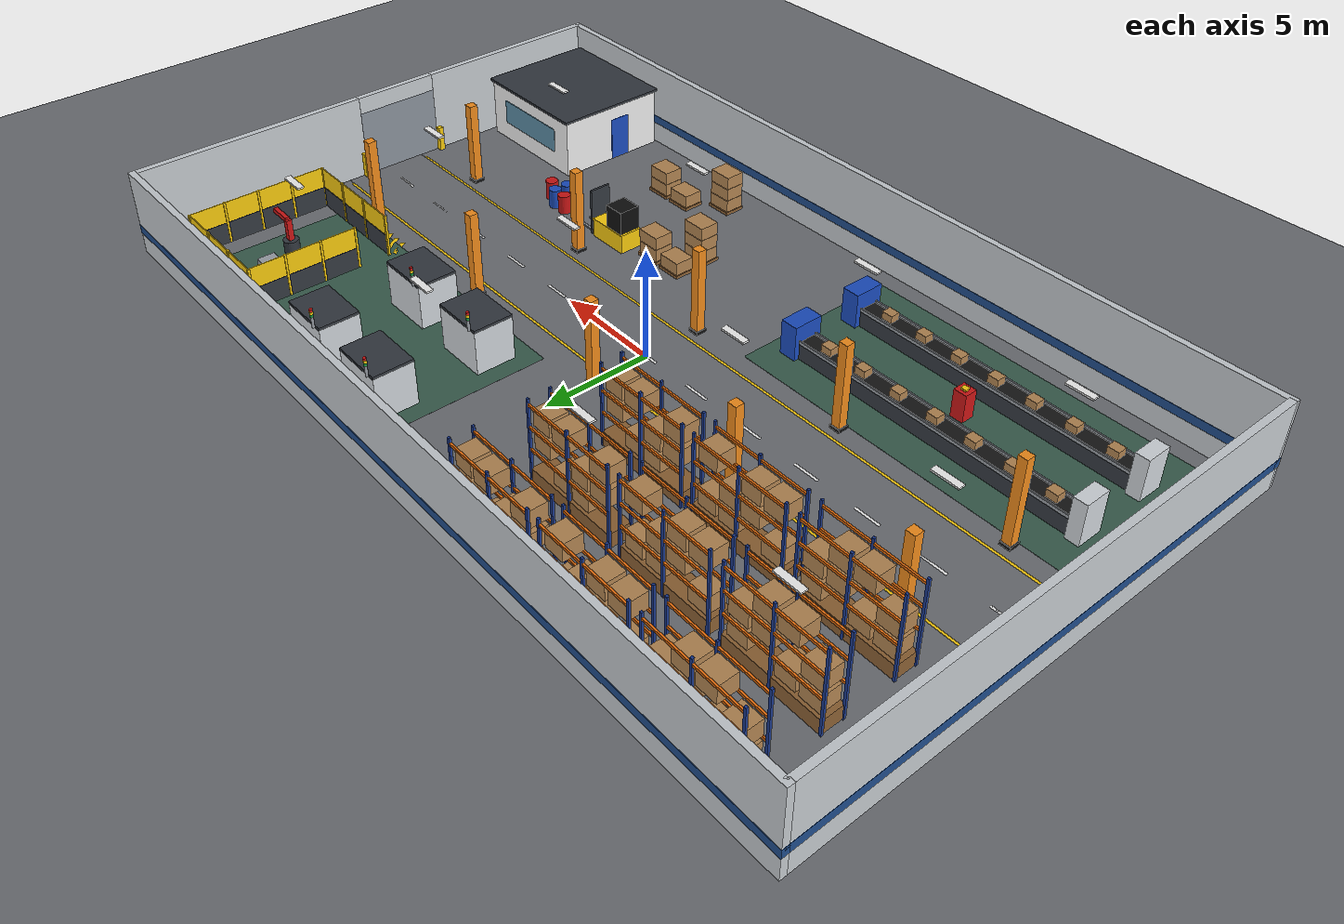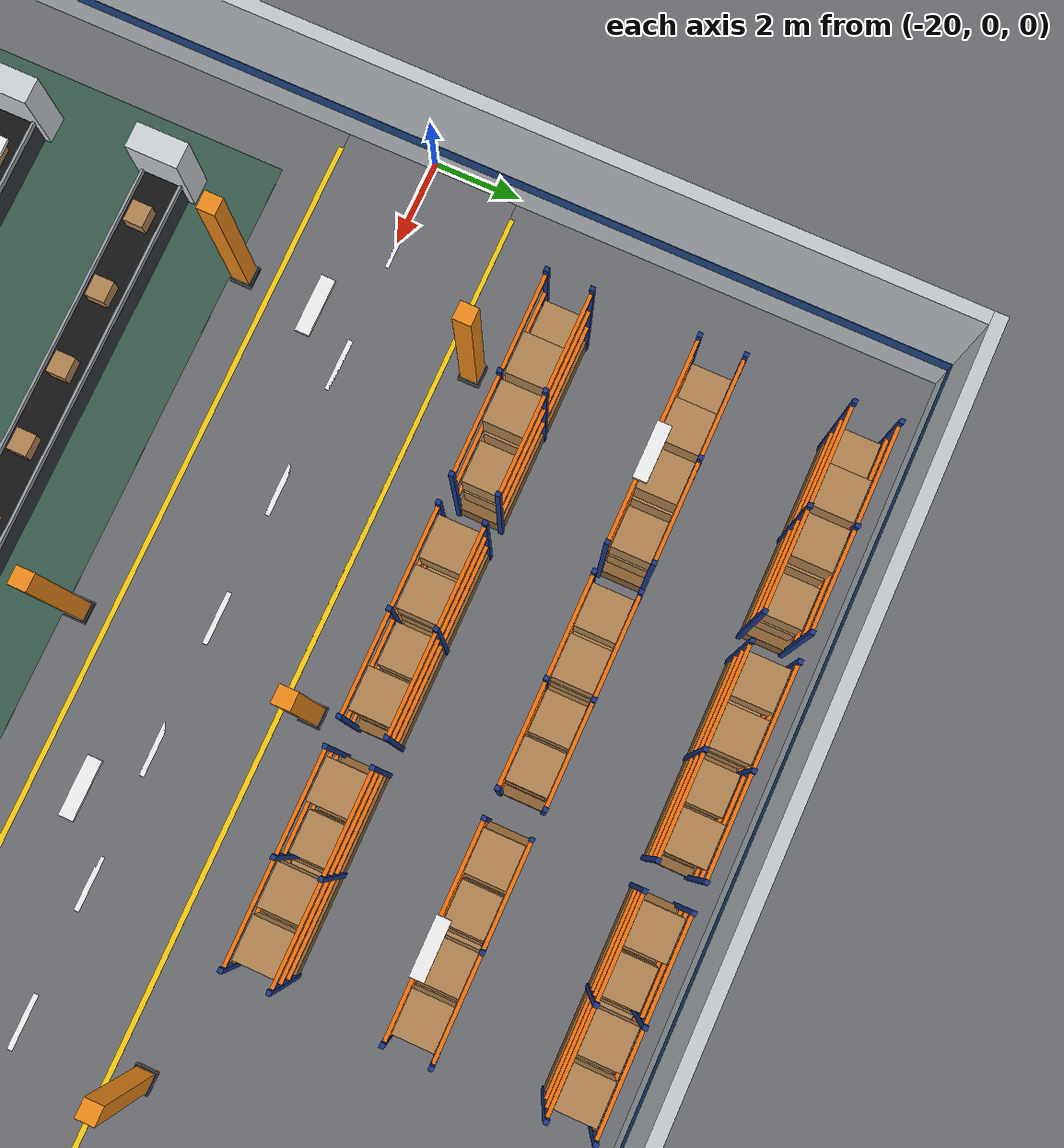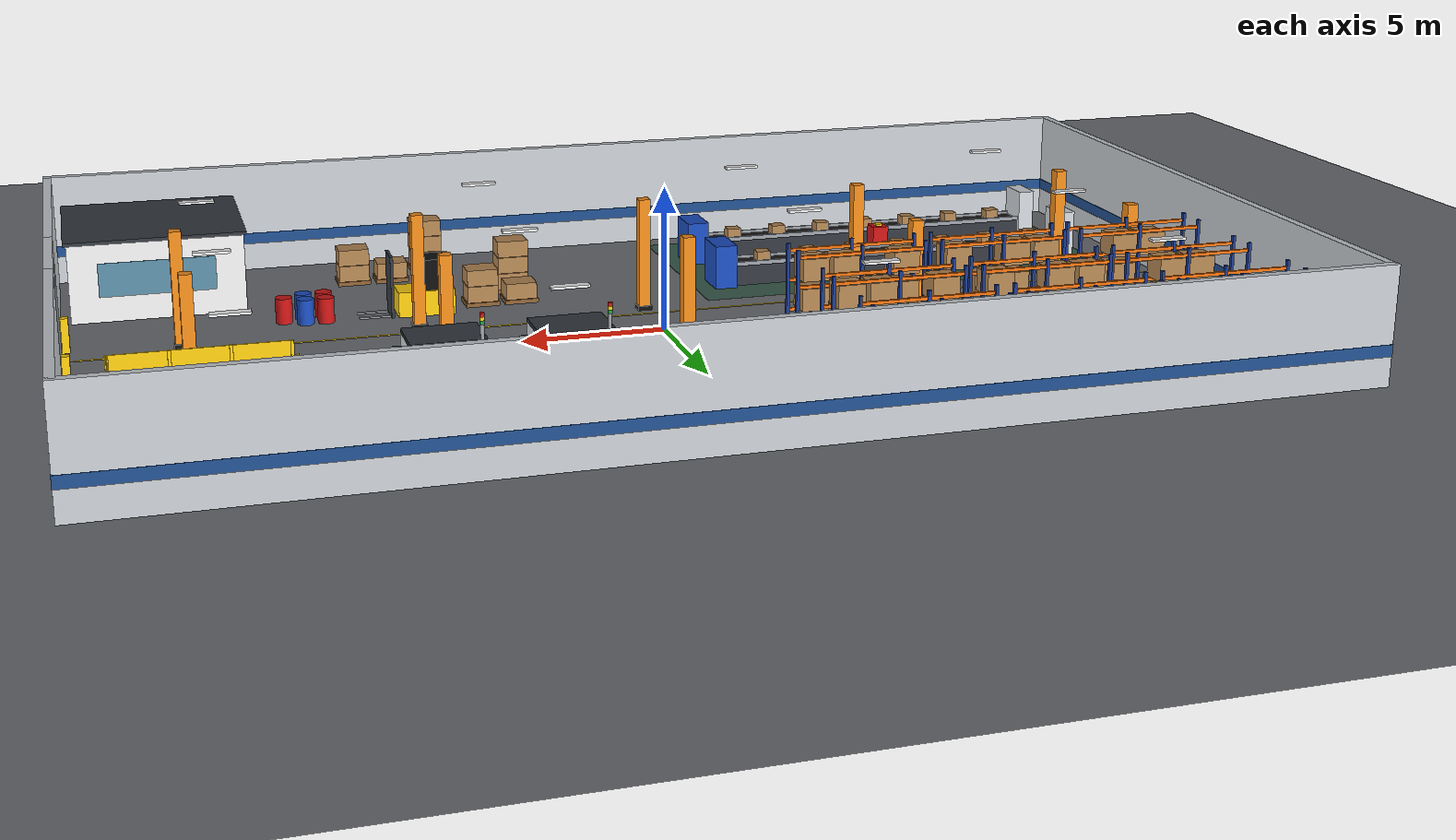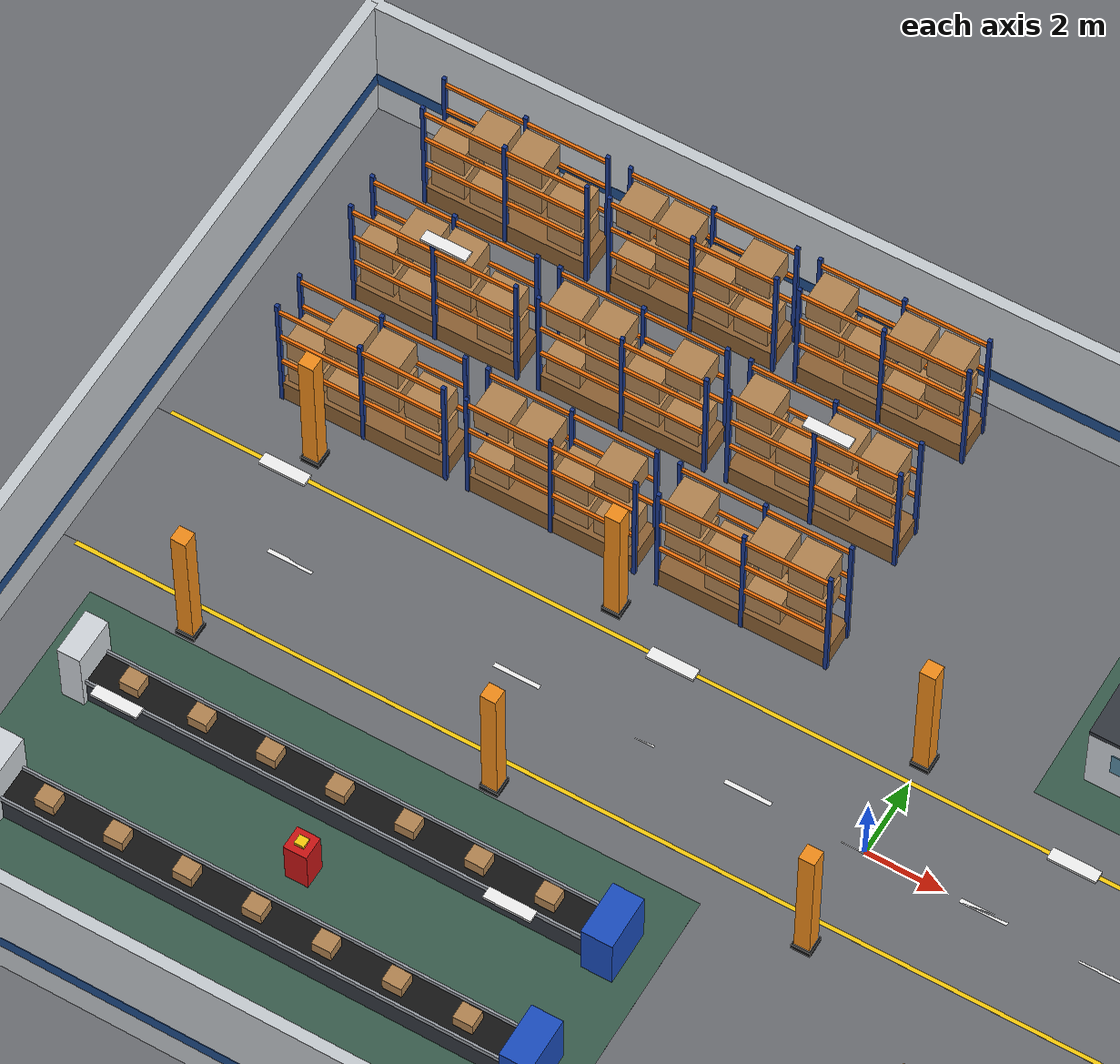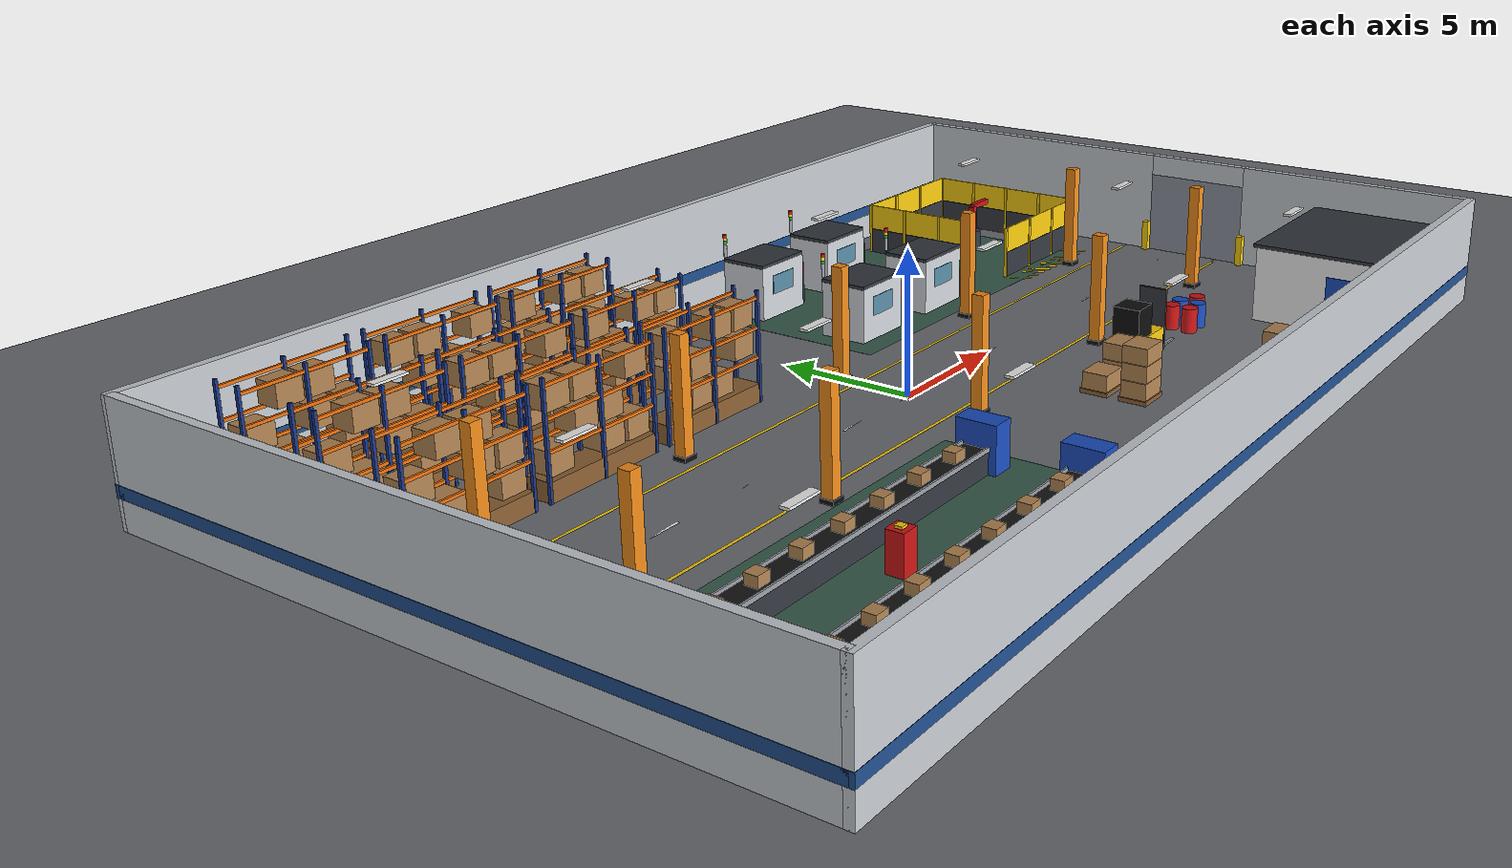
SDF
<?xml version="1.0"?>
<!-- GENERATED by src/tools/make_factory_world.py - edit the script, not this file -->
<sdf version="1.8">
  <world name="factory">
    <physics name="p" type="dart">
      <max_step_size>0.002</max_step_size>
      <real_time_factor>1.0</real_time_factor>
    </physics>
    <plugin filename="gz-sim-physics-system" name="gz::sim::systems::Physics"/>
    <plugin filename="gz-sim-user-commands-system" name="gz::sim::systems::UserCommands"/>
    <plugin filename="gz-sim-scene-broadcaster-system" name="gz::sim::systems::SceneBroadcaster"/>
    <plugin filename="gz-sim-imu-system" name="gz::sim::systems::Imu"/>
    <plugin filename="gz-sim-sensors-system" name="gz::sim::systems::Sensors">
      <render_engine>ogre2</render_engine>
    </plugin>
    <scene>
      <ambient>0.45 0.45 0.48 1</ambient>
      <background>0.62 0.72 0.82 1</background>
      <shadows>true</shadows>
      <grid>false</grid>
    </scene>
    <light type="directional" name="sun">
      <pose>0 0 20 0 0 0</pose><direction>-0.4 0.25 -0.9</direction>
      <diffuse>0.75 0.73 0.68 1</diffuse><specular>0.3 0.3 0.3 1</specular>
      <cast_shadows>true</cast_shadows>
    </light>
    <light type='point' name='lamp_-15_-7'><pose>-15 -7 3.8 0 0 0</pose><diffuse>0.55 0.55 0.5 1</diffuse><specular>0.2 0.2 0.2 1</specular><attenuation><range>14</range><constant>0.3</constant><linear>0.05</linear><quadratic>0.01</quadratic></attenuation><cast_shadows>false</cast_shadows></light><light type='point' name='lamp_-15_0'><pose>-15 0 3.8 0 0 0</pose><diffuse>0.55 0.55 0.5 1</diffuse><specular>0.2 0.2 0.2 1</specular><attenuation><range>14</range><constant>0.3</constant><linear>0.05</linear><quadratic>0.01</quadratic></attenuation><cast_shadows>false</cast_shadows></light><light type='point' name='lamp_-15_7'><pose>-15 7 3.8 0 0 0</pose><diffuse>0.55 0.55 0.5 1</diffuse><specular>0.2 0.2 0.2 1</specular><attenuation><range>14</range><constant>0.3</constant><linear>0.05</linear><quadratic>0.01</quadratic></attenuation><cast_shadows>false</cast_shadows></light><light type='point' name='lamp_-5_-7'><pose>-5 -7 3.8 0 0 0</pose><diffuse>0.55 0.55 0.5 1</diffuse><specular>0.2 0.2 0.2 1</specular><attenuation><range>14</range><constant>0.3</constant><linear>0.05</linear><quadratic>0.01</quadratic></attenuation><cast_shadows>false</cast_shadows></light><light type='point' name='lamp_-5_0'><pose>-5 0 3.8 0 0 0</pose><diffuse>0.55 0.55 0.5 1</diffuse><specular>0.2 0.2 0.2 1</specular><attenuation><range>14</range><constant>0.3</constant><linear>0.05</linear><quadratic>0.01</quadratic></attenuation><cast_shadows>false</cast_shadows></light><light type='point' name='lamp_-5_7'><pose>-5 7 3.8 0 0 0</pose><diffuse>0.55 0.55 0.5 1</diffuse><specular>0.2 0.2 0.2 1</specular><attenuation><range>14</range><constant>0.3</constant><linear>0.05</linear><quadratic>0.01</quadratic></attenuation><cast_shadows>false</cast_shadows></light><light type='point' name='lamp_5_-7'><pose>5 -7 3.8 0 0 0</pose><diffuse>0.55 0.55 0.5 1</diffuse><specular>0.2 0.2 0.2 1</specular><attenuation><range>14</range><constant>0.3</constant><linear>0.05</linear><quadratic>0.01</quadratic></attenuation><cast_shadows>false</cast_shadows></light><light type='point' name='lamp_5_0'><pose>5 0 3.8 0 0 0</pose><diffuse>0.55 0.55 0.5 1</diffuse><specular>0.2 0.2 0.2 1</specular><attenuation><range>14</range><constant>0.3</constant><linear>0.05</linear><quadratic>0.01</quadratic></attenuation><cast_shadows>false</cast_shadows></light><light type='point' name='lamp_5_7'><pose>5 7 3.8 0 0 0</pose><diffuse>0.55 0.55 0.5 1</diffuse><specular>0.2 0.2 0.2 1</specular><attenuation><range>14</range><constant>0.3</constant><linear>0.05</linear><quadratic>0.01</quadratic></attenuation><cast_shadows>false</cast_shadows></light><light type='point' name='lamp_15_-7'><pose>15 -7 3.8 0 0 0</pose><diffuse>0.55 0.55 0.5 1</diffuse><specular>0.2 0.2 0.2 1</specular><attenuation><range>14</range><constant>0.3</constant><linear>0.05</linear><quadratic>0.01</quadratic></attenuation><cast_shadows>false</cast_shadows></light><light type='point' name='lamp_15_0'><pose>15 0 3.8 0 0 0</pose><diffuse>0.55 0.55 0.5 1</diffuse><specular>0.2 0.2 0.2 1</specular><attenuation><range>14</range><constant>0.3</constant><linear>0.05</linear><quadratic>0.01</quadratic></attenuation><cast_shadows>false</cast_shadows></light><light type='point' name='lamp_15_7'><pose>15 7 3.8 0 0 0</pose><diffuse>0.55 0.55 0.5 1</diffuse><specular>0.2 0.2 0.2 1</specular><attenuation><range>14</range><constant>0.3</constant><linear>0.05</linear><quadratic>0.01</quadratic></attenuation><cast_shadows>false</cast_shadows></light>
    <model name="ground"><static>true</static><link name="l">
      <collision name="c"><geometry><plane><normal>0 0 1</normal><size>60 40</size></plane></geometry>
        <surface><friction><ode><mu>1.0</mu><mu2>1.0</mu2></ode></friction></surface></collision>
      <visual name="v"><geometry><plane><normal>0 0 1</normal><size>60 40</size></plane></geometry>
        <material><ambient>0.42 0.43 0.45 1</ambient><diffuse>0.42 0.43 0.45 1</diffuse><specular>0.3 0.3 0.3 1</specular><pbr><metal><metalness>0.0</metalness><roughness>0.85</roughness></metal></pbr></material></visual>
    </link></model>
    <model name='hall'><static>true</static><link name='l0'><pose>0.000 12.000 2.000 0 0 0.000</pose><collision name='c'><geometry><box><size>40.3 0.3 4.0</size></box></geometry></collision><visual name='v'><geometry><box><size>40.3 0.3 4.0</size></box></geometry><material><ambient>0.78 0.8 0.82 1</ambient><diffuse>0.78 0.8 0.82 1</diffuse><specular>0.3 0.3 0.3 1</specular><pbr><metal><metalness>0.0</metalness><roughness>0.7</roughness></metal></pbr></material><cast_shadows>true</cast_shadows></visual></link><link name='l1'><pose>0.000 12.000 1.200 0 0 0.000</pose><visual name='v'><geometry><box><size>40.32 0.32 0.4</size></box></geometry><material><ambient>0.12 0.3 0.55 1</ambient><diffuse>0.12 0.3 0.55 1</diffuse><specular>0.3 0.3 0.3 1</specular><pbr><metal><metalness>0.0</metalness><roughness>0.6</roughness></metal></pbr></material><cast_shadows>false</cast_shadows></visual></link><link name='l2'><pose>0.000 -12.000 2.000 0 0 0.000</pose><collision name='c'><geometry><box><size>40.3 0.3 4.0</size></box></geometry></collision><visual name='v'><geometry><box><size>40.3 0.3 4.0</size></box></geometry><material><ambient>0.78 0.8 0.82 1</ambient><diffuse>0.78 0.8 0.82 1</diffuse><specular>0.3 0.3 0.3 1</specular><pbr><metal><metalness>0.0</metalness><roughness>0.7</roughness></metal></pbr></material><cast_shadows>true</cast_shadows></visual></link><link name='l3'><pose>0.000 -12.000 1.200 0 0 0.000</pose><visual name='v'><geometry><box><size>40.32 0.32 0.4</size></box></geometry><material><ambient>0.12 0.3 0.55 1</ambient><diffuse>0.12 0.3 0.55 1</diffuse><specular>0.3 0.3 0.3 1</specular><pbr><metal><metalness>0.0</metalness><roughness>0.6</roughness></metal></pbr></material><cast_shadows>false</cast_shadows></visual></link><link name='l4'><pose>-20.000 0.000 2.000 0 0 0.000</pose><collision name='c'><geometry><box><size>0.3 24.0 4.0</size></box></geometry></collision><visual name='v'><geometry><box><size>0.3 24.0 4.0</size></box></geometry><material><ambient>0.78 0.8 0.82 1</ambient><diffuse>0.78 0.8 0.82 1</diffuse><specular>0.3 0.3 0.3 1</specular><pbr><metal><metalness>0.0</metalness><roughness>0.7</roughness></metal></pbr></material><cast_shadows>true</cast_shadows></visual></link><link name='l5'><pose>-20.000 0.000 1.200 0 0 0.000</pose><visual name='v'><geometry><box><size>0.32 24.02 0.4</size></box></geometry><material><ambient>0.12 0.3 0.55 1</ambient><diffuse>0.12 0.3 0.55 1</diffuse><specular>0.3 0.3 0.3 1</specular><pbr><metal><metalness>0.0</metalness><roughness>0.6</roughness></metal></pbr></material><cast_shadows>false</cast_shadows></visual></link><link name='l6'><pose>20.000 -7.500 2.000 0 0 0.000</pose><collision name='c'><geometry><box><size>0.3 9.0 4.0</size></box></geometry></collision><visual name='v'><geometry><box><size>0.3 9.0 4.0</size></box></geometry><material><ambient>0.78 0.8 0.82 1</ambient><diffuse>0.78 0.8 0.82 1</diffuse><specular>0.3 0.3 0.3 1</specular><pbr><metal><metalness>0.0</metalness><roughness>0.7</roughness></metal></pbr></material><cast_shadows>true</cast_shadows></visual></link><link name='l7'><pose>20.000 6.500 2.000 0 0 0.000</pose><collision name='c'><geometry><box><size>0.3 11.0 4.0</size></box></geometry></collision><visual name='v'><geometry><box><size>0.3 11.0 4.0</size></box></geometry><material><ambient>0.78 0.8 0.82 1</ambient><diffuse>0.78 0.8 0.82 1</diffuse><specular>0.3 0.3 0.3 1</specular><pbr><metal><metalness>0.0</metalness><roughness>0.7</roughness></metal></pbr></material><cast_shadows>true</cast_shadows></visual></link><link name='l8'><pose>19.950 -1.000 1.600 0 0 0.000</pose><collision name='c'><geometry><box><size>0.2 4.0 3.2</size></box></geometry></collision><visual name='v'><geometry><box><size>0.2 4.0 3.2</size></box></geometry><material><ambient>0.55 0.58 0.62 1</ambient><diffuse>0.55 0.58 0.62 1</diffuse><specular>0.3 0.3 0.3 1</specular><pbr><metal><metalness>0.8</metalness><roughness>0.4</roughness></metal></pbr></material><cast_shadows>true</cast_shadows></visual></link><link name='l9'><pose>20.000 -1.000 3.600 0 0 0.000</pose><collision name='c'><geometry><box><size>0.3 4.0 0.7999999999999998</size></box></geometry></collision><visual name='v'><geometry><box><size>0.3 4.0 0.7999999999999998</size></box></geometry><material><ambient>0.78 0.8 0.82 1</ambient><diffuse>0.78 0.8 0.82 1</diffuse><specular>0.3 0.3 0.3 1</specular><pbr><metal><metalness>0.0</metalness><roughness>0.7</roughness></metal></pbr></material><cast_shadows>true</cast_shadows></visual></link><link name='l10'><pose>19.700 -3.100 0.600 0 0 0.000</pose><collision name='c'><geometry><box><size>0.25 0.25 1.2</size></box></geometry></collision><visual name='v'><geometry><box><size>0.25 0.25 1.2</size></box></geometry><material><ambient>0.98 0.8 0.05 1</ambient><diffuse>0.98 0.8 0.05 1</diffuse><specular>0.3 0.3 0.3 1</specular><pbr><metal><metalness>0.0</metalness><roughness>0.5</roughness></metal></pbr></material><cast_shadows>true</cast_shadows></visual></link><link name='l11'><pose>19.700 1.100 0.600 0 0 0.000</pose><collision name='c'><geometry><box><size>0.25 0.25 1.2</size></box></geometry></collision><visual name='v'><geometry><box><size>0.25 0.25 1.2</size></box></geometry><material><ambient>0.98 0.8 0.05 1</ambient><diffuse>0.98 0.8 0.05 1</diffuse><specular>0.3 0.3 0.3 1</specular><pbr><metal><metalness>0.0</metalness><roughness>0.5</roughness></metal></pbr></material><cast_shadows>true</cast_shadows></visual></link><link name='l12'><pose>-16.000 -2.700 2.000 0 0 0.000</pose><collision name='c'><geometry><box><size>0.4 0.4 4.0</size></box></geometry></collision><visual name='v'><geometry><box><size>0.4 0.4 4.0</size></box></geometry><material><ambient>0.95 0.55 0.1 1</ambient><diffuse>0.95 0.55 0.1 1</diffuse><specular>0.3 0.3 0.3 1</specular><pbr><metal><metalness>0.3</metalness><roughness>0.5</roughness></metal></pbr></material><cast_shadows>true</cast_shadows></visual></link><link name='l13'><pose>-16.000 -2.700 0.075 0 0 0.000</pose><collision name='c'><geometry><box><size>0.5 0.5 0.15</size></box></geometry></collision><visual name='v'><geometry><box><size>0.5 0.5 0.15</size></box></geometry><material><ambient>0.05 0.05 0.05 1</ambient><diffuse>0.05 0.05 0.05 1</diffuse><specular>0.3 0.3 0.3 1</specular><pbr><metal><metalness>0.0</metalness><roughness>0.6</roughness></metal></pbr></material><cast_shadows>true</cast_shadows></visual></link><link name='l14'><pose>-16.000 2.700 2.000 0 0 0.000</pose><collision name='c'><geometry><box><size>0.4 0.4 4.0</size></box></geometry></collision><visual name='v'><geometry><box><size>0.4 0.4 4.0</size></box></geometry><material><ambient>0.95 0.55 0.1 1</ambient><diffuse>0.95 0.55 0.1 1</diffuse><specular>0.3 0.3 0.3 1</specular><pbr><metal><metalness>0.3</metalness><roughness>0.5</roughness></metal></pbr></material><cast_shadows>true</cast_shadows></visual></link><link name='l15'><pose>-16.000 2.700 0.075 0 0 0.000</pose><collision name='c'><geometry><box><size>0.5 0.5 0.15</size></box></geometry></collision><visual name='v'><geometry><box><size>0.5 0.5 0.15</size></box></geometry><material><ambient>0.05 0.05 0.05 1</ambient><diffuse>0.05 0.05 0.05 1</diffuse><specular>0.3 0.3 0.3 1</specular><pbr><metal><metalness>0.0</metalness><roughness>0.6</roughness></metal></pbr></material><cast_shadows>true</cast_shadows></visual></link><link name='l16'><pose>-8.000 -2.700 2.000 0 0 0.000</pose><collision name='c'><geometry><box><size>0.4 0.4 4.0</size></box></geometry></collision><visual name='v'><geometry><box><size>0.4 0.4 4.0</size></box></geometry><material><ambient>0.95 0.55 0.1 1</ambient><diffuse>0.95 0.55 0.1 1</diffuse><specular>0.3 0.3 0.3 1</specular><pbr><metal><metalness>0.3</metalness><roughness>0.5</roughness></metal></pbr></material><cast_shadows>true</cast_shadows></visual></link><link name='l17'><pose>-8.000 -2.700 0.075 0 0 0.000</pose><collision name='c'><geometry><box><size>0.5 0.5 0.15</size></box></geometry></collision><visual name='v'><geometry><box><size>0.5 0.5 0.15</size></box></geometry><material><ambient>0.05 0.05 0.05 1</ambient><diffuse>0.05 0.05 0.05 1</diffuse><specular>0.3 0.3 0.3 1</specular><pbr><metal><metalness>0.0</metalness><roughness>0.6</roughness></metal></pbr></material><cast_shadows>true</cast_shadows></visual></link><link name='l18'><pose>-8.000 2.700 2.000 0 0 0.000</pose><collision name='c'><geometry><box><size>0.4 0.4 4.0</size></box></geometry></collision><visual name='v'><geometry><box><size>0.4 0.4 4.0</size></box></geometry><material><ambient>0.95 0.55 0.1 1</ambient><diffuse>0.95 0.55 0.1 1</diffuse><specular>0.3 0.3 0.3 1</specular><pbr><metal><metalness>0.3</metalness><roughness>0.5</roughness></metal></pbr></material><cast_shadows>true</cast_shadows></visual></link><link name='l19'><pose>-8.000 2.700 0.075 0 0 0.000</pose><collision name='c'><geometry><box><size>0.5 0.5 0.15</size></box></geometry></collision><visual name='v'><geometry><box><size>0.5 0.5 0.15</size></box></geometry><material><ambient>0.05 0.05 0.05 1</ambient><diffuse>0.05 0.05 0.05 1</diffuse><specular>0.3 0.3 0.3 1</specular><pbr><metal><metalness>0.0</metalness><roughness>0.6</roughness></metal></pbr></material><cast_shadows>true</cast_shadows></visual></link><link name='l20'><pose>0.000 -2.700 2.000 0 0 0.000</pose><collision name='c'><geometry><box><size>0.4 0.4 4.0</size></box></geometry></collision><visual name='v'><geometry><box><size>0.4 0.4 4.0</size></box></geometry><material><ambient>0.95 0.55 0.1 1</ambient><diffuse>0.95 0.55 0.1 1</diffuse><specular>0.3 0.3 0.3 1</specular><pbr><metal><metalness>0.3</metalness><roughness>0.5</roughness></metal></pbr></material><cast_shadows>true</cast_shadows></visual></link><link name='l21'><pose>0.000 -2.700 0.075 0 0 0.000</pose><collision name='c'><geometry><box><size>0.5 0.5 0.15</size></box></geometry></collision><visual name='v'><geometry><box><size>0.5 0.5 0.15</size></box></geometry><material><ambient>0.05 0.05 0.05 1</ambient><diffuse>0.05 0.05 0.05 1</diffuse><specular>0.3 0.3 0.3 1</specular><pbr><metal><metalness>0.0</metalness><roughness>0.6</roughness></metal></pbr></material><cast_shadows>true</cast_shadows></visual></link><link name='l22'><pose>0.000 2.700 2.000 0 0 0.000</pose><collision name='c'><geometry><box><size>0.4 0.4 4.0</size></box></geometry></collision><visual name='v'><geometry><box><size>0.4 0.4 4.0</size></box></geometry><material><ambient>0.95 0.55 0.1 1</ambient><diffuse>0.95 0.55 0.1 1</diffuse><specular>0.3 0.3 0.3 1</specular><pbr><metal><metalness>0.3</metalness><roughness>0.5</roughness></metal></pbr></material><cast_shadows>true</cast_shadows></visual></link><link name='l23'><pose>0.000 2.700 0.075 0 0 0.000</pose><collision name='c'><geometry><box><size>0.5 0.5 0.15</size></box></geometry></collision><visual name='v'><geometry><box><size>0.5 0.5 0.15</size></box></geometry><material><ambient>0.05 0.05 0.05 1</ambient><diffuse>0.05 0.05 0.05 1</diffuse><specular>0.3 0.3 0.3 1</specular><pbr><metal><metalness>0.0</metalness><roughness>0.6</roughness></metal></pbr></material><cast_shadows>true</cast_shadows></visual></link><link name='l24'><pose>8.000 -2.700 2.000 0 0 0.000</pose><collision name='c'><geometry><box><size>0.4 0.4 4.0</size></box></geometry></collision><visual name='v'><geometry><box><size>0.4 0.4 4.0</size></box></geometry><material><ambient>0.95 0.55 0.1 1</ambient><diffuse>0.95 0.55 0.1 1</diffuse><specular>0.3 0.3 0.3 1</specular><pbr><metal><metalness>0.3</metalness><roughness>0.5</roughness></metal></pbr></material><cast_shadows>true</cast_shadows></visual></link><link name='l25'><pose>8.000 -2.700 0.075 0 0 0.000</pose><collision name='c'><geometry><box><size>0.5 0.5 0.15</size></box></geometry></collision><visual name='v'><geometry><box><size>0.5 0.5 0.15</size></box></geometry><material><ambient>0.05 0.05 0.05 1</ambient><diffuse>0.05 0.05 0.05 1</diffuse><specular>0.3 0.3 0.3 1</specular><pbr><metal><metalness>0.0</metalness><roughness>0.6</roughness></metal></pbr></material><cast_shadows>true</cast_shadows></visual></link><link name='l26'><pose>8.000 2.700 2.000 0 0 0.000</pose><collision name='c'><geometry><box><size>0.4 0.4 4.0</size></box></geometry></collision><visual name='v'><geometry><box><size>0.4 0.4 4.0</size></box></geometry><material><ambient>0.95 0.55 0.1 1</ambient><diffuse>0.95 0.55 0.1 1</diffuse><specular>0.3 0.3 0.3 1</specular><pbr><metal><metalness>0.3</metalness><roughness>0.5</roughness></metal></pbr></material><cast_shadows>true</cast_shadows></visual></link><link name='l27'><pose>8.000 2.700 0.075 0 0 0.000</pose><collision name='c'><geometry><box><size>0.5 0.5 0.15</size></box></geometry></collision><visual name='v'><geometry><box><size>0.5 0.5 0.15</size></box></geometry><material><ambient>0.05 0.05 0.05 1</ambient><diffuse>0.05 0.05 0.05 1</diffuse><specular>0.3 0.3 0.3 1</specular><pbr><metal><metalness>0.0</metalness><roughness>0.6</roughness></metal></pbr></material><cast_shadows>true</cast_shadows></visual></link><link name='l28'><pose>16.000 -2.700 2.000 0 0 0.000</pose><collision name='c'><geometry><box><size>0.4 0.4 4.0</size></box></geometry></collision><visual name='v'><geometry><box><size>0.4 0.4 4.0</size></box></geometry><material><ambient>0.95 0.55 0.1 1</ambient><diffuse>0.95 0.55 0.1 1</diffuse><specular>0.3 0.3 0.3 1</specular><pbr><metal><metalness>0.3</metalness><roughness>0.5</roughness></metal></pbr></material><cast_shadows>true</cast_shadows></visual></link><link name='l29'><pose>16.000 -2.700 0.075 0 0 0.000</pose><collision name='c'><geometry><box><size>0.5 0.5 0.15</size></box></geometry></collision><visual name='v'><geometry><box><size>0.5 0.5 0.15</size></box></geometry><material><ambient>0.05 0.05 0.05 1</ambient><diffuse>0.05 0.05 0.05 1</diffuse><specular>0.3 0.3 0.3 1</specular><pbr><metal><metalness>0.0</metalness><roughness>0.6</roughness></metal></pbr></material><cast_shadows>true</cast_shadows></visual></link><link name='l30'><pose>16.000 2.700 2.000 0 0 0.000</pose><collision name='c'><geometry><box><size>0.4 0.4 4.0</size></box></geometry></collision><visual name='v'><geometry><box><size>0.4 0.4 4.0</size></box></geometry><material><ambient>0.95 0.55 0.1 1</ambient><diffuse>0.95 0.55 0.1 1</diffuse><specular>0.3 0.3 0.3 1</specular><pbr><metal><metalness>0.3</metalness><roughness>0.5</roughness></metal></pbr></material><cast_shadows>true</cast_shadows></visual></link><link name='l31'><pose>16.000 2.700 0.075 0 0 0.000</pose><collision name='c'><geometry><box><size>0.5 0.5 0.15</size></box></geometry></collision><visual name='v'><geometry><box><size>0.5 0.5 0.15</size></box></geometry><material><ambient>0.05 0.05 0.05 1</ambient><diffuse>0.05 0.05 0.05 1</diffuse><specular>0.3 0.3 0.3 1</specular><pbr><metal><metalness>0.0</metalness><roughness>0.6</roughness></metal></pbr></material><cast_shadows>true</cast_shadows></visual></link><link name='l32'><pose>-15.000 -7.000 3.890 0 0 0.000</pose><visual name='v'><geometry><box><size>1.2 0.3 0.08</size></box></geometry><material><ambient>0.95 0.95 0.95 1</ambient><diffuse>0.95 0.95 0.95 1</diffuse><specular>0.3 0.3 0.3 1</specular><pbr><metal><metalness>0.0</metalness><roughness>0.6</roughness></metal></pbr></material><cast_shadows>false</cast_shadows></visual></link><link name='l33'><pose>-15.000 0.000 3.890 0 0 0.000</pose><visual name='v'><geometry><box><size>1.2 0.3 0.08</size></box></geometry><material><ambient>0.95 0.95 0.95 1</ambient><diffuse>0.95 0.95 0.95 1</diffuse><specular>0.3 0.3 0.3 1</specular><pbr><metal><metalness>0.0</metalness><roughness>0.6</roughness></metal></pbr></material><cast_shadows>false</cast_shadows></visual></link><link name='l34'><pose>-15.000 7.000 3.890 0 0 0.000</pose><visual name='v'><geometry><box><size>1.2 0.3 0.08</size></box></geometry><material><ambient>0.95 0.95 0.95 1</ambient><diffuse>0.95 0.95 0.95 1</diffuse><specular>0.3 0.3 0.3 1</specular><pbr><metal><metalness>0.0</metalness><roughness>0.6</roughness></metal></pbr></material><cast_shadows>false</cast_shadows></visual></link><link name='l35'><pose>-5.000 -7.000 3.890 0 0 0.000</pose><visual name='v'><geometry><box><size>1.2 0.3 0.08</size></box></geometry><material><ambient>0.95 0.95 0.95 1</ambient><diffuse>0.95 0.95 0.95 1</diffuse><specular>0.3 0.3 0.3 1</specular><pbr><metal><metalness>0.0</metalness><roughness>0.6</roughness></metal></pbr></material><cast_shadows>false</cast_shadows></visual></link><link name='l36'><pose>-5.000 0.000 3.890 0 0 0.000</pose><visual name='v'><geometry><box><size>1.2 0.3 0.08</size></box></geometry><material><ambient>0.95 0.95 0.95 1</ambient><diffuse>0.95 0.95 0.95 1</diffuse><specular>0.3 0.3 0.3 1</specular><pbr><metal><metalness>0.0</metalness><roughness>0.6</roughness></metal></pbr></material><cast_shadows>false</cast_shadows></visual></link><link name='l37'><pose>-5.000 7.000 3.890 0 0 0.000</pose><visual name='v'><geometry><box><size>1.2 0.3 0.08</size></box></geometry><material><ambient>0.95 0.95 0.95 1</ambient><diffuse>0.95 0.95 0.95 1</diffuse><specular>0.3 0.3 0.3 1</specular><pbr><metal><metalness>0.0</metalness><roughness>0.6</roughness></metal></pbr></material><cast_shadows>false</cast_shadows></visual></link><link name='l38'><pose>5.000 -7.000 3.890 0 0 0.000</pose><visual name='v'><geometry><box><size>1.2 0.3 0.08</size></box></geometry><material><ambient>0.95 0.95 0.95 1</ambient><diffuse>0.95 0.95 0.95 1</diffuse><specular>0.3 0.3 0.3 1</specular><pbr><metal><metalness>0.0</metalness><roughness>0.6</roughness></metal></pbr></material><cast_shadows>false</cast_shadows></visual></link><link name='l39'><pose>5.000 0.000 3.890 0 0 0.000</pose><visual name='v'><geometry><box><size>1.2 0.3 0.08</size></box></geometry><material><ambient>0.95 0.95 0.95 1</ambient><diffuse>0.95 0.95 0.95 1</diffuse><specular>0.3 0.3 0.3 1</specular><pbr><metal><metalness>0.0</metalness><roughness>0.6</roughness></metal></pbr></material><cast_shadows>false</cast_shadows></visual></link><link name='l40'><pose>5.000 7.000 3.890 0 0 0.000</pose><visual name='v'><geometry><box><size>1.2 0.3 0.08</size></box></geometry><material><ambient>0.95 0.95 0.95 1</ambient><diffuse>0.95 0.95 0.95 1</diffuse><specular>0.3 0.3 0.3 1</specular><pbr><metal><metalness>0.0</metalness><roughness>0.6</roughness></metal></pbr></material><cast_shadows>false</cast_shadows></visual></link><link name='l41'><pose>15.000 -7.000 3.890 0 0 0.000</pose><visual name='v'><geometry><box><size>1.2 0.3 0.08</size></box></geometry><material><ambient>0.95 0.95 0.95 1</ambient><diffuse>0.95 0.95 0.95 1</diffuse><specular>0.3 0.3 0.3 1</specular><pbr><metal><metalness>0.0</metalness><roughness>0.6</roughness></metal></pbr></material><cast_shadows>false</cast_shadows></visual></link><link name='l42'><pose>15.000 0.000 3.890 0 0 0.000</pose><visual name='v'><geometry><box><size>1.2 0.3 0.08</size></box></geometry><material><ambient>0.95 0.95 0.95 1</ambient><diffuse>0.95 0.95 0.95 1</diffuse><specular>0.3 0.3 0.3 1</specular><pbr><metal><metalness>0.0</metalness><roughness>0.6</roughness></metal></pbr></material><cast_shadows>false</cast_shadows></visual></link><link name='l43'><pose>15.000 7.000 3.890 0 0 0.000</pose><visual name='v'><geometry><box><size>1.2 0.3 0.08</size></box></geometry><material><ambient>0.95 0.95 0.95 1</ambient><diffuse>0.95 0.95 0.95 1</diffuse><specular>0.3 0.3 0.3 1</specular><pbr><metal><metalness>0.0</metalness><roughness>0.6</roughness></metal></pbr></material><cast_shadows>false</cast_shadows></visual></link></model>
    <model name='floor_marks'><static>true</static><link name='l0'><pose>0.000 0.000 0.002 0 0 0.000</pose><visual name='v'><geometry><box><size>40.0 4.0 0.004</size></box></geometry><material><ambient>0.42 0.43 0.45 1</ambient><diffuse>0.42 0.43 0.45 1</diffuse><specular>0.3 0.3 0.3 1</specular><pbr><metal><metalness>0.0</metalness><roughness>0.85</roughness></metal></pbr></material><cast_shadows>false</cast_shadows></visual></link><link name='l1'><pose>0.000 -2.050 0.002 0 0 0.000</pose><visual name='v'><geometry><box><size>39.0 0.12 0.004</size></box></geometry><material><ambient>0.98 0.8 0.05 1</ambient><diffuse>0.98 0.8 0.05 1</diffuse><specular>0.3 0.3 0.3 1</specular><pbr><metal><metalness>0.0</metalness><roughness>0.5</roughness></metal></pbr></material><cast_shadows>false</cast_shadows></visual></link><link name='l2'><pose>0.000 2.050 0.002 0 0 0.000</pose><visual name='v'><geometry><box><size>39.0 0.12 0.004</size></box></geometry><material><ambient>0.98 0.8 0.05 1</ambient><diffuse>0.98 0.8 0.05 1</diffuse><specular>0.3 0.3 0.3 1</specular><pbr><metal><metalness>0.0</metalness><roughness>0.5</roughness></metal></pbr></material><cast_shadows>false</cast_shadows></visual></link><link name='l3'><pose>-18.000 0.000 0.002 0 0 0.000</pose><visual name='v'><geometry><box><size>1.2 0.12 0.004</size></box></geometry><material><ambient>0.95 0.95 0.95 1</ambient><diffuse>0.95 0.95 0.95 1</diffuse><specular>0.3 0.3 0.3 1</specular><pbr><metal><metalness>0.0</metalness><roughness>0.6</roughness></metal></pbr></material><cast_shadows>false</cast_shadows></visual></link><link name='l4'><pose>-15.000 0.000 0.002 0 0 0.000</pose><visual name='v'><geometry><box><size>1.2 0.12 0.004</size></box></geometry><material><ambient>0.95 0.95 0.95 1</ambient><diffuse>0.95 0.95 0.95 1</diffuse><specular>0.3 0.3 0.3 1</specular><pbr><metal><metalness>0.0</metalness><roughness>0.6</roughness></metal></pbr></material><cast_shadows>false</cast_shadows></visual></link><link name='l5'><pose>-12.000 0.000 0.002 0 0 0.000</pose><visual name='v'><geometry><box><size>1.2 0.12 0.004</size></box></geometry><material><ambient>0.95 0.95 0.95 1</ambient><diffuse>0.95 0.95 0.95 1</diffuse><specular>0.3 0.3 0.3 1</specular><pbr><metal><metalness>0.0</metalness><roughness>0.6</roughness></metal></pbr></material><cast_shadows>false</cast_shadows></visual></link><link name='l6'><pose>-9.000 0.000 0.002 0 0 0.000</pose><visual name='v'><geometry><box><size>1.2 0.12 0.004</size></box></geometry><material><ambient>0.95 0.95 0.95 1</ambient><diffuse>0.95 0.95 0.95 1</diffuse><specular>0.3 0.3 0.3 1</specular><pbr><metal><metalness>0.0</metalness><roughness>0.6</roughness></metal></pbr></material><cast_shadows>false</cast_shadows></visual></link><link name='l7'><pose>-6.000 0.000 0.002 0 0 0.000</pose><visual name='v'><geometry><box><size>1.2 0.12 0.004</size></box></geometry><material><ambient>0.95 0.95 0.95 1</ambient><diffuse>0.95 0.95 0.95 1</diffuse><specular>0.3 0.3 0.3 1</specular><pbr><metal><metalness>0.0</metalness><roughness>0.6</roughness></metal></pbr></material><cast_shadows>false</cast_shadows></visual></link><link name='l8'><pose>-3.000 0.000 0.002 0 0 0.000</pose><visual name='v'><geometry><box><size>1.2 0.12 0.004</size></box></geometry><material><ambient>0.95 0.95 0.95 1</ambient><diffuse>0.95 0.95 0.95 1</diffuse><specular>0.3 0.3 0.3 1</specular><pbr><metal><metalness>0.0</metalness><roughness>0.6</roughness></metal></pbr></material><cast_shadows>false</cast_shadows></visual></link><link name='l9'><pose>0.000 0.000 0.002 0 0 0.000</pose><visual name='v'><geometry><box><size>1.2 0.12 0.004</size></box></geometry><material><ambient>0.95 0.95 0.95 1</ambient><diffuse>0.95 0.95 0.95 1</diffuse><specular>0.3 0.3 0.3 1</specular><pbr><metal><metalness>0.0</metalness><roughness>0.6</roughness></metal></pbr></material><cast_shadows>false</cast_shadows></visual></link><link name='l10'><pose>3.000 0.000 0.002 0 0 0.000</pose><visual name='v'><geometry><box><size>1.2 0.12 0.004</size></box></geometry><material><ambient>0.95 0.95 0.95 1</ambient><diffuse>0.95 0.95 0.95 1</diffuse><specular>0.3 0.3 0.3 1</specular><pbr><metal><metalness>0.0</metalness><roughness>0.6</roughness></metal></pbr></material><cast_shadows>false</cast_shadows></visual></link><link name='l11'><pose>6.000 0.000 0.002 0 0 0.000</pose><visual name='v'><geometry><box><size>1.2 0.12 0.004</size></box></geometry><material><ambient>0.95 0.95 0.95 1</ambient><diffuse>0.95 0.95 0.95 1</diffuse><specular>0.3 0.3 0.3 1</specular><pbr><metal><metalness>0.0</metalness><roughness>0.6</roughness></metal></pbr></material><cast_shadows>false</cast_shadows></visual></link><link name='l12'><pose>9.000 0.000 0.002 0 0 0.000</pose><visual name='v'><geometry><box><size>1.2 0.12 0.004</size></box></geometry><material><ambient>0.95 0.95 0.95 1</ambient><diffuse>0.95 0.95 0.95 1</diffuse><specular>0.3 0.3 0.3 1</specular><pbr><metal><metalness>0.0</metalness><roughness>0.6</roughness></metal></pbr></material><cast_shadows>false</cast_shadows></visual></link><link name='l13'><pose>12.000 0.000 0.002 0 0 0.000</pose><visual name='v'><geometry><box><size>1.2 0.12 0.004</size></box></geometry><material><ambient>0.95 0.95 0.95 1</ambient><diffuse>0.95 0.95 0.95 1</diffuse><specular>0.3 0.3 0.3 1</specular><pbr><metal><metalness>0.0</metalness><roughness>0.6</roughness></metal></pbr></material><cast_shadows>false</cast_shadows></visual></link><link name='l14'><pose>15.000 0.000 0.002 0 0 0.000</pose><visual name='v'><geometry><box><size>1.2 0.12 0.004</size></box></geometry><material><ambient>0.95 0.95 0.95 1</ambient><diffuse>0.95 0.95 0.95 1</diffuse><specular>0.3 0.3 0.3 1</specular><pbr><metal><metalness>0.0</metalness><roughness>0.6</roughness></metal></pbr></material><cast_shadows>false</cast_shadows></visual></link><link name='l15'><pose>18.000 0.000 0.002 0 0 0.000</pose><visual name='v'><geometry><box><size>1.2 0.12 0.004</size></box></geometry><material><ambient>0.95 0.95 0.95 1</ambient><diffuse>0.95 0.95 0.95 1</diffuse><specular>0.3 0.3 0.3 1</specular><pbr><metal><metalness>0.0</metalness><roughness>0.6</roughness></metal></pbr></material><cast_shadows>false</cast_shadows></visual></link><link name='l16'><pose>10.000 7.000 0.002 0 0 0.000</pose><visual name='v'><geometry><box><size>15 7.5 0.004</size></box></geometry><material><ambient>0.22 0.36 0.3 1</ambient><diffuse>0.22 0.36 0.3 1</diffuse><specular>0.3 0.3 0.3 1</specular><pbr><metal><metalness>0.0</metalness><roughness>0.35</roughness></metal></pbr></material><cast_shadows>false</cast_shadows></visual></link><link name='l17'><pose>-10.500 -7.000 0.002 0 0 0.000</pose><visual name='v'><geometry><box><size>16 8 0.004</size></box></geometry><material><ambient>0.22 0.36 0.3 1</ambient><diffuse>0.22 0.36 0.3 1</diffuse><specular>0.3 0.3 0.3 1</specular><pbr><metal><metalness>0.0</metalness><roughness>0.35</roughness></metal></pbr></material><cast_shadows>false</cast_shadows></visual></link><link name='l18'><pose>13.200 3.400 0.002 0 0 0.600</pose><visual name='v'><geometry><box><size>0.2 0.9 0.004</size></box></geometry><material><ambient>0.98 0.8 0.05 1</ambient><diffuse>0.98 0.8 0.05 1</diffuse><specular>0.3 0.3 0.3 1</specular><pbr><metal><metalness>0.0</metalness><roughness>0.5</roughness></metal></pbr></material><cast_shadows>false</cast_shadows></visual></link><link name='l19'><pose>13.700 3.400 0.002 0 0 0.600</pose><visual name='v'><geometry><box><size>0.2 0.9 0.004</size></box></geometry><material><ambient>0.98 0.8 0.05 1</ambient><diffuse>0.98 0.8 0.05 1</diffuse><specular>0.3 0.3 0.3 1</specular><pbr><metal><metalness>0.0</metalness><roughness>0.5</roughness></metal></pbr></material><cast_shadows>false</cast_shadows></visual></link><link name='l20'><pose>14.200 3.400 0.002 0 0 0.600</pose><visual name='v'><geometry><box><size>0.2 0.9 0.004</size></box></geometry><material><ambient>0.98 0.8 0.05 1</ambient><diffuse>0.98 0.8 0.05 1</diffuse><specular>0.3 0.3 0.3 1</specular><pbr><metal><metalness>0.0</metalness><roughness>0.5</roughness></metal></pbr></material><cast_shadows>false</cast_shadows></visual></link><link name='l21'><pose>14.700 3.400 0.002 0 0 0.600</pose><visual name='v'><geometry><box><size>0.2 0.9 0.004</size></box></geometry><material><ambient>0.98 0.8 0.05 1</ambient><diffuse>0.98 0.8 0.05 1</diffuse><specular>0.3 0.3 0.3 1</specular><pbr><metal><metalness>0.0</metalness><roughness>0.5</roughness></metal></pbr></material><cast_shadows>false</cast_shadows></visual></link><link name='l22'><pose>15.200 3.400 0.002 0 0 0.600</pose><visual name='v'><geometry><box><size>0.2 0.9 0.004</size></box></geometry><material><ambient>0.98 0.8 0.05 1</ambient><diffuse>0.98 0.8 0.05 1</diffuse><specular>0.3 0.3 0.3 1</specular><pbr><metal><metalness>0.0</metalness><roughness>0.5</roughness></metal></pbr></material><cast_shadows>false</cast_shadows></visual></link><link name='l23'><pose>15.700 3.400 0.002 0 0 0.600</pose><visual name='v'><geometry><box><size>0.2 0.9 0.004</size></box></geometry><material><ambient>0.98 0.8 0.05 1</ambient><diffuse>0.98 0.8 0.05 1</diffuse><specular>0.3 0.3 0.3 1</specular><pbr><metal><metalness>0.0</metalness><roughness>0.5</roughness></metal></pbr></material><cast_shadows>false</cast_shadows></visual></link><link name='l24'><pose>16.200 3.400 0.002 0 0 0.600</pose><visual name='v'><geometry><box><size>0.2 0.9 0.004</size></box></geometry><material><ambient>0.98 0.8 0.05 1</ambient><diffuse>0.98 0.8 0.05 1</diffuse><specular>0.3 0.3 0.3 1</specular><pbr><metal><metalness>0.0</metalness><roughness>0.5</roughness></metal></pbr></material><cast_shadows>false</cast_shadows></visual></link><link name='l25'><pose>16.700 3.400 0.002 0 0 0.600</pose><visual name='v'><geometry><box><size>0.2 0.9 0.004</size></box></geometry><material><ambient>0.98 0.8 0.05 1</ambient><diffuse>0.98 0.8 0.05 1</diffuse><specular>0.3 0.3 0.3 1</specular><pbr><metal><metalness>0.0</metalness><roughness>0.5</roughness></metal></pbr></material><cast_shadows>false</cast_shadows></visual></link><link name='l26'><pose>17.200 3.400 0.002 0 0 0.600</pose><visual name='v'><geometry><box><size>0.2 0.9 0.004</size></box></geometry><material><ambient>0.98 0.8 0.05 1</ambient><diffuse>0.98 0.8 0.05 1</diffuse><specular>0.3 0.3 0.3 1</specular><pbr><metal><metalness>0.0</metalness><roughness>0.5</roughness></metal></pbr></material><cast_shadows>false</cast_shadows></visual></link><link name='l27'><pose>17.700 3.400 0.002 0 0 0.600</pose><visual name='v'><geometry><box><size>0.2 0.9 0.004</size></box></geometry><material><ambient>0.98 0.8 0.05 1</ambient><diffuse>0.98 0.8 0.05 1</diffuse><specular>0.3 0.3 0.3 1</specular><pbr><metal><metalness>0.0</metalness><roughness>0.5</roughness></metal></pbr></material><cast_shadows>false</cast_shadows></visual></link></model>
    <model name='pallet_racks'><static>true</static><link name='l0'><pose>-15.300 4.200 0.325 0 0 0.000</pose><collision name='c'><geometry><box><size>4.4 1.0 0.65</size></box></geometry></collision><visual name='v'><geometry><box><size>4.4 1.0 0.65</size></box></geometry><material><ambient>0.55 0.38 0.2 1</ambient><diffuse>0.55 0.38 0.2 1</diffuse><specular>0.3 0.3 0.3 1</specular><pbr><metal><metalness>0.0</metalness><roughness>0.9</roughness></metal></pbr></material><cast_shadows>true</cast_shadows></visual></link><link name='l1'><pose>-16.900 4.200 1.125 0 0 0.000</pose><collision name='c'><geometry><box><size>0.9 0.85 0.75</size></box></geometry></collision><visual name='v'><geometry><box><size>0.9 0.85 0.75</size></box></geometry><material><ambient>0.7 0.52 0.32 1</ambient><diffuse>0.7 0.52 0.32 1</diffuse><specular>0.3 0.3 0.3 1</specular><pbr><metal><metalness>0.0</metalness><roughness>0.95</roughness></metal></pbr></material><cast_shadows>true</cast_shadows></visual></link><link name='l2'><pose>-15.850 4.200 1.125 0 0 0.000</pose><collision name='c'><geometry><box><size>0.9 0.85 0.75</size></box></geometry></collision><visual name='v'><geometry><box><size>0.9 0.85 0.75</size></box></geometry><material><ambient>0.7 0.52 0.32 1</ambient><diffuse>0.7 0.52 0.32 1</diffuse><specular>0.3 0.3 0.3 1</specular><pbr><metal><metalness>0.0</metalness><roughness>0.95</roughness></metal></pbr></material><cast_shadows>true</cast_shadows></visual></link><link name='l3'><pose>-13.750 4.200 1.125 0 0 0.000</pose><collision name='c'><geometry><box><size>0.9 0.85 0.75</size></box></geometry></collision><visual name='v'><geometry><box><size>0.9 0.85 0.75</size></box></geometry><material><ambient>0.7 0.52 0.32 1</ambient><diffuse>0.7 0.52 0.32 1</diffuse><specular>0.3 0.3 0.3 1</specular><pbr><metal><metalness>0.0</metalness><roughness>0.95</roughness></metal></pbr></material><cast_shadows>true</cast_shadows></visual></link><link name='l4'><pose>-16.900 4.200 2.075 0 0 0.000</pose><collision name='c'><geometry><box><size>0.9 0.85 0.75</size></box></geometry></collision><visual name='v'><geometry><box><size>0.9 0.85 0.75</size></box></geometry><material><ambient>0.7 0.52 0.32 1</ambient><diffuse>0.7 0.52 0.32 1</diffuse><specular>0.3 0.3 0.3 1</specular><pbr><metal><metalness>0.0</metalness><roughness>0.95</roughness></metal></pbr></material><cast_shadows>true</cast_shadows></visual></link><link name='l5'><pose>-14.800 4.200 2.075 0 0 0.000</pose><collision name='c'><geometry><box><size>0.9 0.85 0.75</size></box></geometry></collision><visual name='v'><geometry><box><size>0.9 0.85 0.75</size></box></geometry><material><ambient>0.7 0.52 0.32 1</ambient><diffuse>0.7 0.52 0.32 1</diffuse><specular>0.3 0.3 0.3 1</specular><pbr><metal><metalness>0.0</metalness><roughness>0.95</roughness></metal></pbr></material><cast_shadows>true</cast_shadows></visual></link><link name='l6'><pose>-13.750 4.200 2.075 0 0 0.000</pose><collision name='c'><geometry><box><size>0.9 0.85 0.75</size></box></geometry></collision><visual name='v'><geometry><box><size>0.9 0.85 0.75</size></box></geometry><material><ambient>0.7 0.52 0.32 1</ambient><diffuse>0.7 0.52 0.32 1</diffuse><specular>0.3 0.3 0.3 1</specular><pbr><metal><metalness>0.0</metalness><roughness>0.95</roughness></metal></pbr></material><cast_shadows>true</cast_shadows></visual></link><link name='l7'><pose>-15.850 4.200 3.075 0 0 0.000</pose><collision name='c'><geometry><box><size>0.9 0.85 0.75</size></box></geometry></collision><visual name='v'><geometry><box><size>0.9 0.85 0.75</size></box></geometry><material><ambient>0.7 0.52 0.32 1</ambient><diffuse>0.7 0.52 0.32 1</diffuse><specular>0.3 0.3 0.3 1</specular><pbr><metal><metalness>0.0</metalness><roughness>0.95</roughness></metal></pbr></material><cast_shadows>true</cast_shadows></visual></link><link name='l8'><pose>-14.800 4.200 3.075 0 0 0.000</pose><collision name='c'><geometry><box><size>0.9 0.85 0.75</size></box></geometry></collision><visual name='v'><geometry><box><size>0.9 0.85 0.75</size></box></geometry><material><ambient>0.7 0.52 0.32 1</ambient><diffuse>0.7 0.52 0.32 1</diffuse><specular>0.3 0.3 0.3 1</specular><pbr><metal><metalness>0.0</metalness><roughness>0.95</roughness></metal></pbr></material><cast_shadows>true</cast_shadows></visual></link><link name='l9'><pose>-15.300 3.720 1.550 0 0 0.000</pose><collision name='c'><geometry><box><size>4.4 0.08 0.1</size></box></geometry></collision><visual name='v'><geometry><box><size>4.4 0.08 0.1</size></box></geometry><material><ambient>0.95 0.45 0.05 1</ambient><diffuse>0.95 0.45 0.05 1</diffuse><specular>0.3 0.3 0.3 1</specular><pbr><metal><metalness>0.5</metalness><roughness>0.4</roughness></metal></pbr></material><cast_shadows>true</cast_shadows></visual></link><link name='l10'><pose>-15.300 4.680 1.550 0 0 0.000</pose><collision name='c'><geometry><box><size>4.4 0.08 0.1</size></box></geometry></collision><visual name='v'><geometry><box><size>4.4 0.08 0.1</size></box></geometry><material><ambient>0.95 0.45 0.05 1</ambient><diffuse>0.95 0.45 0.05 1</diffuse><specular>0.3 0.3 0.3 1</specular><pbr><metal><metalness>0.5</metalness><roughness>0.4</roughness></metal></pbr></material><cast_shadows>true</cast_shadows></visual></link><link name='l11'><pose>-15.300 3.720 2.550 0 0 0.000</pose><collision name='c'><geometry><box><size>4.4 0.08 0.1</size></box></geometry></collision><visual name='v'><geometry><box><size>4.4 0.08 0.1</size></box></geometry><material><ambient>0.95 0.45 0.05 1</ambient><diffuse>0.95 0.45 0.05 1</diffuse><specular>0.3 0.3 0.3 1</specular><pbr><metal><metalness>0.5</metalness><roughness>0.4</roughness></metal></pbr></material><cast_shadows>true</cast_shadows></visual></link><link name='l12'><pose>-15.300 4.680 2.550 0 0 0.000</pose><collision name='c'><geometry><box><size>4.4 0.08 0.1</size></box></geometry></collision><visual name='v'><geometry><box><size>4.4 0.08 0.1</size></box></geometry><material><ambient>0.95 0.45 0.05 1</ambient><diffuse>0.95 0.45 0.05 1</diffuse><specular>0.3 0.3 0.3 1</specular><pbr><metal><metalness>0.5</metalness><roughness>0.4</roughness></metal></pbr></material><cast_shadows>true</cast_shadows></visual></link><link name='l13'><pose>-15.300 3.720 3.550 0 0 0.000</pose><collision name='c'><geometry><box><size>4.4 0.08 0.1</size></box></geometry></collision><visual name='v'><geometry><box><size>4.4 0.08 0.1</size></box></geometry><material><ambient>0.95 0.45 0.05 1</ambient><diffuse>0.95 0.45 0.05 1</diffuse><specular>0.3 0.3 0.3 1</specular><pbr><metal><metalness>0.5</metalness><roughness>0.4</roughness></metal></pbr></material><cast_shadows>true</cast_shadows></visual></link><link name='l14'><pose>-15.300 4.680 3.550 0 0 0.000</pose><collision name='c'><geometry><box><size>4.4 0.08 0.1</size></box></geometry></collision><visual name='v'><geometry><box><size>4.4 0.08 0.1</size></box></geometry><material><ambient>0.95 0.45 0.05 1</ambient><diffuse>0.95 0.45 0.05 1</diffuse><specular>0.3 0.3 0.3 1</specular><pbr><metal><metalness>0.5</metalness><roughness>0.4</roughness></metal></pbr></material><cast_shadows>true</cast_shadows></visual></link><link name='l15'><pose>-17.500 3.720 1.900 0 0 0.000</pose><collision name='c'><geometry><box><size>0.1 0.1 3.8</size></box></geometry></collision><visual name='v'><geometry><box><size>0.1 0.1 3.8</size></box></geometry><material><ambient>0.1 0.22 0.55 1</ambient><diffuse>0.1 0.22 0.55 1</diffuse><specular>0.3 0.3 0.3 1</specular><pbr><metal><metalness>0.6</metalness><roughness>0.4</roughness></metal></pbr></material><cast_shadows>true</cast_shadows></visual></link><link name='l16'><pose>-17.500 4.680 1.900 0 0 0.000</pose><collision name='c'><geometry><box><size>0.1 0.1 3.8</size></box></geometry></collision><visual name='v'><geometry><box><size>0.1 0.1 3.8</size></box></geometry><material><ambient>0.1 0.22 0.55 1</ambient><diffuse>0.1 0.22 0.55 1</diffuse><specular>0.3 0.3 0.3 1</specular><pbr><metal><metalness>0.6</metalness><roughness>0.4</roughness></metal></pbr></material><cast_shadows>true</cast_shadows></visual></link><link name='l17'><pose>-15.300 3.720 1.900 0 0 0.000</pose><collision name='c'><geometry><box><size>0.1 0.1 3.8</size></box></geometry></collision><visual name='v'><geometry><box><size>0.1 0.1 3.8</size></box></geometry><material><ambient>0.1 0.22 0.55 1</ambient><diffuse>0.1 0.22 0.55 1</diffuse><specular>0.3 0.3 0.3 1</specular><pbr><metal><metalness>0.6</metalness><roughness>0.4</roughness></metal></pbr></material><cast_shadows>true</cast_shadows></visual></link><link name='l18'><pose>-15.300 4.680 1.900 0 0 0.000</pose><collision name='c'><geometry><box><size>0.1 0.1 3.8</size></box></geometry></collision><visual name='v'><geometry><box><size>0.1 0.1 3.8</size></box></geometry><material><ambient>0.1 0.22 0.55 1</ambient><diffuse>0.1 0.22 0.55 1</diffuse><specular>0.3 0.3 0.3 1</specular><pbr><metal><metalness>0.6</metalness><roughness>0.4</roughness></metal></pbr></material><cast_shadows>true</cast_shadows></visual></link><link name='l19'><pose>-13.100 3.720 1.900 0 0 0.000</pose><collision name='c'><geometry><box><size>0.1 0.1 3.8</size></box></geometry></collision><visual name='v'><geometry><box><size>0.1 0.1 3.8</size></box></geometry><material><ambient>0.1 0.22 0.55 1</ambient><diffuse>0.1 0.22 0.55 1</diffuse><specular>0.3 0.3 0.3 1</specular><pbr><metal><metalness>0.6</metalness><roughness>0.4</roughness></metal></pbr></material><cast_shadows>true</cast_shadows></visual></link><link name='l20'><pose>-13.100 4.680 1.900 0 0 0.000</pose><collision name='c'><geometry><box><size>0.1 0.1 3.8</size></box></geometry></collision><visual name='v'><geometry><box><size>0.1 0.1 3.8</size></box></geometry><material><ambient>0.1 0.22 0.55 1</ambient><diffuse>0.1 0.22 0.55 1</diffuse><specular>0.3 0.3 0.3 1</specular><pbr><metal><metalness>0.6</metalness><roughness>0.4</roughness></metal></pbr></material><cast_shadows>true</cast_shadows></visual></link><link name='l21'><pose>-10.300 4.200 0.325 0 0 0.000</pose><collision name='c'><geometry><box><size>4.4 1.0 0.65</size></box></geometry></collision><visual name='v'><geometry><box><size>4.4 1.0 0.65</size></box></geometry><material><ambient>0.55 0.38 0.2 1</ambient><diffuse>0.55 0.38 0.2 1</diffuse><specular>0.3 0.3 0.3 1</specular><pbr><metal><metalness>0.0</metalness><roughness>0.9</roughness></metal></pbr></material><cast_shadows>true</cast_shadows></visual></link><link name='l22'><pose>-11.900 4.200 1.125 0 0 0.000</pose><collision name='c'><geometry><box><size>0.9 0.85 0.75</size></box></geometry></collision><visual name='v'><geometry><box><size>0.9 0.85 0.75</size></box></geometry><material><ambient>0.7 0.52 0.32 1</ambient><diffuse>0.7 0.52 0.32 1</diffuse><specular>0.3 0.3 0.3 1</specular><pbr><metal><metalness>0.0</metalness><roughness>0.95</roughness></metal></pbr></material><cast_shadows>true</cast_shadows></visual></link><link name='l23'><pose>-9.800 4.200 1.125 0 0 0.000</pose><collision name='c'><geometry><box><size>0.9 0.85 0.75</size></box></geometry></collision><visual name='v'><geometry><box><size>0.9 0.85 0.75</size></box></geometry><material><ambient>0.7 0.52 0.32 1</ambient><diffuse>0.7 0.52 0.32 1</diffuse><specular>0.3 0.3 0.3 1</specular><pbr><metal><metalness>0.0</metalness><roughness>0.95</roughness></metal></pbr></material><cast_shadows>true</cast_shadows></visual></link><link name='l24'><pose>-8.750 4.200 1.125 0 0 0.000</pose><collision name='c'><geometry><box><size>0.9 0.85 0.75</size></box></geometry></collision><visual name='v'><geometry><box><size>0.9 0.85 0.75</size></box></geometry><material><ambient>0.7 0.52 0.32 1</ambient><diffuse>0.7 0.52 0.32 1</diffuse><specular>0.3 0.3 0.3 1</specular><pbr><metal><metalness>0.0</metalness><roughness>0.95</roughness></metal></pbr></material><cast_shadows>true</cast_shadows></visual></link><link name='l25'><pose>-10.850 4.200 2.075 0 0 0.000</pose><collision name='c'><geometry><box><size>0.9 0.85 0.75</size></box></geometry></collision><visual name='v'><geometry><box><size>0.9 0.85 0.75</size></box></geometry><material><ambient>0.7 0.52 0.32 1</ambient><diffuse>0.7 0.52 0.32 1</diffuse><specular>0.3 0.3 0.3 1</specular><pbr><metal><metalness>0.0</metalness><roughness>0.95</roughness></metal></pbr></material><cast_shadows>true</cast_shadows></visual></link><link name='l26'><pose>-9.800 4.200 2.075 0 0 0.000</pose><collision name='c'><geometry><box><size>0.9 0.85 0.75</size></box></geometry></collision><visual name='v'><geometry><box><size>0.9 0.85 0.75</size></box></geometry><material><ambient>0.7 0.52 0.32 1</ambient><diffuse>0.7 0.52 0.32 1</diffuse><specular>0.3 0.3 0.3 1</specular><pbr><metal><metalness>0.0</metalness><roughness>0.95</roughness></metal></pbr></material><cast_shadows>true</cast_shadows></visual></link><link name='l27'><pose>-11.900 4.200 3.075 0 0 0.000</pose><collision name='c'><geometry><box><size>0.9 0.85 0.75</size></box></geometry></collision><visual name='v'><geometry><box><size>0.9 0.85 0.75</size></box></geometry><material><ambient>0.7 0.52 0.32 1</ambient><diffuse>0.7 0.52 0.32 1</diffuse><specular>0.3 0.3 0.3 1</specular><pbr><metal><metalness>0.0</metalness><roughness>0.95</roughness></metal></pbr></material><cast_shadows>true</cast_shadows></visual></link><link name='l28'><pose>-10.850 4.200 3.075 0 0 0.000</pose><collision name='c'><geometry><box><size>0.9 0.85 0.75</size></box></geometry></collision><visual name='v'><geometry><box><size>0.9 0.85 0.75</size></box></geometry><material><ambient>0.7 0.52 0.32 1</ambient><diffuse>0.7 0.52 0.32 1</diffuse><specular>0.3 0.3 0.3 1</specular><pbr><metal><metalness>0.0</metalness><roughness>0.95</roughness></metal></pbr></material><cast_shadows>true</cast_shadows></visual></link><link name='l29'><pose>-8.750 4.200 3.075 0 0 0.000</pose><collision name='c'><geometry><box><size>0.9 0.85 0.75</size></box></geometry></collision><visual name='v'><geometry><box><size>0.9 0.85 0.75</size></box></geometry><material><ambient>0.7 0.52 0.32 1</ambient><diffuse>0.7 0.52 0.32 1</diffuse><specular>0.3 0.3 0.3 1</specular><pbr><metal><metalness>0.0</metalness><roughness>0.95</roughness></metal></pbr></material><cast_shadows>true</cast_shadows></visual></link><link name='l30'><pose>-10.300 3.720 1.550 0 0 0.000</pose><collision name='c'><geometry><box><size>4.4 0.08 0.1</size></box></geometry></collision><visual name='v'><geometry><box><size>4.4 0.08 0.1</size></box></geometry><material><ambient>0.95 0.45 0.05 1</ambient><diffuse>0.95 0.45 0.05 1</diffuse><specular>0.3 0.3 0.3 1</specular><pbr><metal><metalness>0.5</metalness><roughness>0.4</roughness></metal></pbr></material><cast_shadows>true</cast_shadows></visual></link><link name='l31'><pose>-10.300 4.680 1.550 0 0 0.000</pose><collision name='c'><geometry><box><size>4.4 0.08 0.1</size></box></geometry></collision><visual name='v'><geometry><box><size>4.4 0.08 0.1</size></box></geometry><material><ambient>0.95 0.45 0.05 1</ambient><diffuse>0.95 0.45 0.05 1</diffuse><specular>0.3 0.3 0.3 1</specular><pbr><metal><metalness>0.5</metalness><roughness>0.4</roughness></metal></pbr></material><cast_shadows>true</cast_shadows></visual></link><link name='l32'><pose>-10.300 3.720 2.550 0 0 0.000</pose><collision name='c'><geometry><box><size>4.4 0.08 0.1</size></box></geometry></collision><visual name='v'><geometry><box><size>4.4 0.08 0.1</size></box></geometry><material><ambient>0.95 0.45 0.05 1</ambient><diffuse>0.95 0.45 0.05 1</diffuse><specular>0.3 0.3 0.3 1</specular><pbr><metal><metalness>0.5</metalness><roughness>0.4</roughness></metal></pbr></material><cast_shadows>true</cast_shadows></visual></link><link name='l33'><pose>-10.300 4.680 2.550 0 0 0.000</pose><collision name='c'><geometry><box><size>4.4 0.08 0.1</size></box></geometry></collision><visual name='v'><geometry><box><size>4.4 0.08 0.1</size></box></geometry><material><ambient>0.95 0.45 0.05 1</ambient><diffuse>0.95 0.45 0.05 1</diffuse><specular>0.3 0.3 0.3 1</specular><pbr><metal><metalness>0.5</metalness><roughness>0.4</roughness></metal></pbr></material><cast_shadows>true</cast_shadows></visual></link><link name='l34'><pose>-10.300 3.720 3.550 0 0 0.000</pose><collision name='c'><geometry><box><size>4.4 0.08 0.1</size></box></geometry></collision><visual name='v'><geometry><box><size>4.4 0.08 0.1</size></box></geometry><material><ambient>0.95 0.45 0.05 1</ambient><diffuse>0.95 0.45 0.05 1</diffuse><specular>0.3 0.3 0.3 1</specular><pbr><metal><metalness>0.5</metalness><roughness>0.4</roughness></metal></pbr></material><cast_shadows>true</cast_shadows></visual></link><link name='l35'><pose>-10.300 4.680 3.550 0 0 0.000</pose><collision name='c'><geometry><box><size>4.4 0.08 0.1</size></box></geometry></collision><visual name='v'><geometry><box><size>4.4 0.08 0.1</size></box></geometry><material><ambient>0.95 0.45 0.05 1</ambient><diffuse>0.95 0.45 0.05 1</diffuse><specular>0.3 0.3 0.3 1</specular><pbr><metal><metalness>0.5</metalness><roughness>0.4</roughness></metal></pbr></material><cast_shadows>true</cast_shadows></visual></link><link name='l36'><pose>-12.500 3.720 1.900 0 0 0.000</pose><collision name='c'><geometry><box><size>0.1 0.1 3.8</size></box></geometry></collision><visual name='v'><geometry><box><size>0.1 0.1 3.8</size></box></geometry><material><ambient>0.1 0.22 0.55 1</ambient><diffuse>0.1 0.22 0.55 1</diffuse><specular>0.3 0.3 0.3 1</specular><pbr><metal><metalness>0.6</metalness><roughness>0.4</roughness></metal></pbr></material><cast_shadows>true</cast_shadows></visual></link><link name='l37'><pose>-12.500 4.680 1.900 0 0 0.000</pose><collision name='c'><geometry><box><size>0.1 0.1 3.8</size></box></geometry></collision><visual name='v'><geometry><box><size>0.1 0.1 3.8</size></box></geometry><material><ambient>0.1 0.22 0.55 1</ambient><diffuse>0.1 0.22 0.55 1</diffuse><specular>0.3 0.3 0.3 1</specular><pbr><metal><metalness>0.6</metalness><roughness>0.4</roughness></metal></pbr></material><cast_shadows>true</cast_shadows></visual></link><link name='l38'><pose>-10.300 3.720 1.900 0 0 0.000</pose><collision name='c'><geometry><box><size>0.1 0.1 3.8</size></box></geometry></collision><visual name='v'><geometry><box><size>0.1 0.1 3.8</size></box></geometry><material><ambient>0.1 0.22 0.55 1</ambient><diffuse>0.1 0.22 0.55 1</diffuse><specular>0.3 0.3 0.3 1</specular><pbr><metal><metalness>0.6</metalness><roughness>0.4</roughness></metal></pbr></material><cast_shadows>true</cast_shadows></visual></link><link name='l39'><pose>-10.300 4.680 1.900 0 0 0.000</pose><collision name='c'><geometry><box><size>0.1 0.1 3.8</size></box></geometry></collision><visual name='v'><geometry><box><size>0.1 0.1 3.8</size></box></geometry><material><ambient>0.1 0.22 0.55 1</ambient><diffuse>0.1 0.22 0.55 1</diffuse><specular>0.3 0.3 0.3 1</specular><pbr><metal><metalness>0.6</metalness><roughness>0.4</roughness></metal></pbr></material><cast_shadows>true</cast_shadows></visual></link><link name='l40'><pose>-8.100 3.720 1.900 0 0 0.000</pose><collision name='c'><geometry><box><size>0.1 0.1 3.8</size></box></geometry></collision><visual name='v'><geometry><box><size>0.1 0.1 3.8</size></box></geometry><material><ambient>0.1 0.22 0.55 1</ambient><diffuse>0.1 0.22 0.55 1</diffuse><specular>0.3 0.3 0.3 1</specular><pbr><metal><metalness>0.6</metalness><roughness>0.4</roughness></metal></pbr></material><cast_shadows>true</cast_shadows></visual></link><link name='l41'><pose>-8.100 4.680 1.900 0 0 0.000</pose><collision name='c'><geometry><box><size>0.1 0.1 3.8</size></box></geometry></collision><visual name='v'><geometry><box><size>0.1 0.1 3.8</size></box></geometry><material><ambient>0.1 0.22 0.55 1</ambient><diffuse>0.1 0.22 0.55 1</diffuse><specular>0.3 0.3 0.3 1</specular><pbr><metal><metalness>0.6</metalness><roughness>0.4</roughness></metal></pbr></material><cast_shadows>true</cast_shadows></visual></link><link name='l42'><pose>-5.300 4.200 0.325 0 0 0.000</pose><collision name='c'><geometry><box><size>4.4 1.0 0.65</size></box></geometry></collision><visual name='v'><geometry><box><size>4.4 1.0 0.65</size></box></geometry><material><ambient>0.55 0.38 0.2 1</ambient><diffuse>0.55 0.38 0.2 1</diffuse><specular>0.3 0.3 0.3 1</specular><pbr><metal><metalness>0.0</metalness><roughness>0.9</roughness></metal></pbr></material><cast_shadows>true</cast_shadows></visual></link><link name='l43'><pose>-5.850 4.200 1.125 0 0 0.000</pose><collision name='c'><geometry><box><size>0.9 0.85 0.75</size></box></geometry></collision><visual name='v'><geometry><box><size>0.9 0.85 0.75</size></box></geometry><material><ambient>0.7 0.52 0.32 1</ambient><diffuse>0.7 0.52 0.32 1</diffuse><specular>0.3 0.3 0.3 1</specular><pbr><metal><metalness>0.0</metalness><roughness>0.95</roughness></metal></pbr></material><cast_shadows>true</cast_shadows></visual></link><link name='l44'><pose>-4.800 4.200 1.125 0 0 0.000</pose><collision name='c'><geometry><box><size>0.9 0.85 0.75</size></box></geometry></collision><visual name='v'><geometry><box><size>0.9 0.85 0.75</size></box></geometry><material><ambient>0.7 0.52 0.32 1</ambient><diffuse>0.7 0.52 0.32 1</diffuse><specular>0.3 0.3 0.3 1</specular><pbr><metal><metalness>0.0</metalness><roughness>0.95</roughness></metal></pbr></material><cast_shadows>true</cast_shadows></visual></link><link name='l45'><pose>-6.900 4.200 2.075 0 0 0.000</pose><collision name='c'><geometry><box><size>0.9 0.85 0.75</size></box></geometry></collision><visual name='v'><geometry><box><size>0.9 0.85 0.75</size></box></geometry><material><ambient>0.7 0.52 0.32 1</ambient><diffuse>0.7 0.52 0.32 1</diffuse><specular>0.3 0.3 0.3 1</specular><pbr><metal><metalness>0.0</metalness><roughness>0.95</roughness></metal></pbr></material><cast_shadows>true</cast_shadows></visual></link><link name='l46'><pose>-5.850 4.200 2.075 0 0 0.000</pose><collision name='c'><geometry><box><size>0.9 0.85 0.75</size></box></geometry></collision><visual name='v'><geometry><box><size>0.9 0.85 0.75</size></box></geometry><material><ambient>0.7 0.52 0.32 1</ambient><diffuse>0.7 0.52 0.32 1</diffuse><specular>0.3 0.3 0.3 1</specular><pbr><metal><metalness>0.0</metalness><roughness>0.95</roughness></metal></pbr></material><cast_shadows>true</cast_shadows></visual></link><link name='l47'><pose>-3.750 4.200 2.075 0 0 0.000</pose><collision name='c'><geometry><box><size>0.9 0.85 0.75</size></box></geometry></collision><visual name='v'><geometry><box><size>0.9 0.85 0.75</size></box></geometry><material><ambient>0.7 0.52 0.32 1</ambient><diffuse>0.7 0.52 0.32 1</diffuse><specular>0.3 0.3 0.3 1</specular><pbr><metal><metalness>0.0</metalness><roughness>0.95</roughness></metal></pbr></material><cast_shadows>true</cast_shadows></visual></link><link name='l48'><pose>-6.900 4.200 3.075 0 0 0.000</pose><collision name='c'><geometry><box><size>0.9 0.85 0.75</size></box></geometry></collision><visual name='v'><geometry><box><size>0.9 0.85 0.75</size></box></geometry><material><ambient>0.7 0.52 0.32 1</ambient><diffuse>0.7 0.52 0.32 1</diffuse><specular>0.3 0.3 0.3 1</specular><pbr><metal><metalness>0.0</metalness><roughness>0.95</roughness></metal></pbr></material><cast_shadows>true</cast_shadows></visual></link><link name='l49'><pose>-4.800 4.200 3.075 0 0 0.000</pose><collision name='c'><geometry><box><size>0.9 0.85 0.75</size></box></geometry></collision><visual name='v'><geometry><box><size>0.9 0.85 0.75</size></box></geometry><material><ambient>0.7 0.52 0.32 1</ambient><diffuse>0.7 0.52 0.32 1</diffuse><specular>0.3 0.3 0.3 1</specular><pbr><metal><metalness>0.0</metalness><roughness>0.95</roughness></metal></pbr></material><cast_shadows>true</cast_shadows></visual></link><link name='l50'><pose>-3.750 4.200 3.075 0 0 0.000</pose><collision name='c'><geometry><box><size>0.9 0.85 0.75</size></box></geometry></collision><visual name='v'><geometry><box><size>0.9 0.85 0.75</size></box></geometry><material><ambient>0.7 0.52 0.32 1</ambient><diffuse>0.7 0.52 0.32 1</diffuse><specular>0.3 0.3 0.3 1</specular><pbr><metal><metalness>0.0</metalness><roughness>0.95</roughness></metal></pbr></material><cast_shadows>true</cast_shadows></visual></link><link name='l51'><pose>-5.300 3.720 1.550 0 0 0.000</pose><collision name='c'><geometry><box><size>4.4 0.08 0.1</size></box></geometry></collision><visual name='v'><geometry><box><size>4.4 0.08 0.1</size></box></geometry><material><ambient>0.95 0.45 0.05 1</ambient><diffuse>0.95 0.45 0.05 1</diffuse><specular>0.3 0.3 0.3 1</specular><pbr><metal><metalness>0.5</metalness><roughness>0.4</roughness></metal></pbr></material><cast_shadows>true</cast_shadows></visual></link><link name='l52'><pose>-5.300 4.680 1.550 0 0 0.000</pose><collision name='c'><geometry><box><size>4.4 0.08 0.1</size></box></geometry></collision><visual name='v'><geometry><box><size>4.4 0.08 0.1</size></box></geometry><material><ambient>0.95 0.45 0.05 1</ambient><diffuse>0.95 0.45 0.05 1</diffuse><specular>0.3 0.3 0.3 1</specular><pbr><metal><metalness>0.5</metalness><roughness>0.4</roughness></metal></pbr></material><cast_shadows>true</cast_shadows></visual></link><link name='l53'><pose>-5.300 3.720 2.550 0 0 0.000</pose><collision name='c'><geometry><box><size>4.4 0.08 0.1</size></box></geometry></collision><visual name='v'><geometry><box><size>4.4 0.08 0.1</size></box></geometry><material><ambient>0.95 0.45 0.05 1</ambient><diffuse>0.95 0.45 0.05 1</diffuse><specular>0.3 0.3 0.3 1</specular><pbr><metal><metalness>0.5</metalness><roughness>0.4</roughness></metal></pbr></material><cast_shadows>true</cast_shadows></visual></link><link name='l54'><pose>-5.300 4.680 2.550 0 0 0.000</pose><collision name='c'><geometry><box><size>4.4 0.08 0.1</size></box></geometry></collision><visual name='v'><geometry><box><size>4.4 0.08 0.1</size></box></geometry><material><ambient>0.95 0.45 0.05 1</ambient><diffuse>0.95 0.45 0.05 1</diffuse><specular>0.3 0.3 0.3 1</specular><pbr><metal><metalness>0.5</metalness><roughness>0.4</roughness></metal></pbr></material><cast_shadows>true</cast_shadows></visual></link><link name='l55'><pose>-5.300 3.720 3.550 0 0 0.000</pose><collision name='c'><geometry><box><size>4.4 0.08 0.1</size></box></geometry></collision><visual name='v'><geometry><box><size>4.4 0.08 0.1</size></box></geometry><material><ambient>0.95 0.45 0.05 1</ambient><diffuse>0.95 0.45 0.05 1</diffuse><specular>0.3 0.3 0.3 1</specular><pbr><metal><metalness>0.5</metalness><roughness>0.4</roughness></metal></pbr></material><cast_shadows>true</cast_shadows></visual></link><link name='l56'><pose>-5.300 4.680 3.550 0 0 0.000</pose><collision name='c'><geometry><box><size>4.4 0.08 0.1</size></box></geometry></collision><visual name='v'><geometry><box><size>4.4 0.08 0.1</size></box></geometry><material><ambient>0.95 0.45 0.05 1</ambient><diffuse>0.95 0.45 0.05 1</diffuse><specular>0.3 0.3 0.3 1</specular><pbr><metal><metalness>0.5</metalness><roughness>0.4</roughness></metal></pbr></material><cast_shadows>true</cast_shadows></visual></link><link name='l57'><pose>-7.500 3.720 1.900 0 0 0.000</pose><collision name='c'><geometry><box><size>0.1 0.1 3.8</size></box></geometry></collision><visual name='v'><geometry><box><size>0.1 0.1 3.8</size></box></geometry><material><ambient>0.1 0.22 0.55 1</ambient><diffuse>0.1 0.22 0.55 1</diffuse><specular>0.3 0.3 0.3 1</specular><pbr><metal><metalness>0.6</metalness><roughness>0.4</roughness></metal></pbr></material><cast_shadows>true</cast_shadows></visual></link><link name='l58'><pose>-7.500 4.680 1.900 0 0 0.000</pose><collision name='c'><geometry><box><size>0.1 0.1 3.8</size></box></geometry></collision><visual name='v'><geometry><box><size>0.1 0.1 3.8</size></box></geometry><material><ambient>0.1 0.22 0.55 1</ambient><diffuse>0.1 0.22 0.55 1</diffuse><specular>0.3 0.3 0.3 1</specular><pbr><metal><metalness>0.6</metalness><roughness>0.4</roughness></metal></pbr></material><cast_shadows>true</cast_shadows></visual></link><link name='l59'><pose>-5.300 3.720 1.900 0 0 0.000</pose><collision name='c'><geometry><box><size>0.1 0.1 3.8</size></box></geometry></collision><visual name='v'><geometry><box><size>0.1 0.1 3.8</size></box></geometry><material><ambient>0.1 0.22 0.55 1</ambient><diffuse>0.1 0.22 0.55 1</diffuse><specular>0.3 0.3 0.3 1</specular><pbr><metal><metalness>0.6</metalness><roughness>0.4</roughness></metal></pbr></material><cast_shadows>true</cast_shadows></visual></link><link name='l60'><pose>-5.300 4.680 1.900 0 0 0.000</pose><collision name='c'><geometry><box><size>0.1 0.1 3.8</size></box></geometry></collision><visual name='v'><geometry><box><size>0.1 0.1 3.8</size></box></geometry><material><ambient>0.1 0.22 0.55 1</ambient><diffuse>0.1 0.22 0.55 1</diffuse><specular>0.3 0.3 0.3 1</specular><pbr><metal><metalness>0.6</metalness><roughness>0.4</roughness></metal></pbr></material><cast_shadows>true</cast_shadows></visual></link><link name='l61'><pose>-3.100 3.720 1.900 0 0 0.000</pose><collision name='c'><geometry><box><size>0.1 0.1 3.8</size></box></geometry></collision><visual name='v'><geometry><box><size>0.1 0.1 3.8</size></box></geometry><material><ambient>0.1 0.22 0.55 1</ambient><diffuse>0.1 0.22 0.55 1</diffuse><specular>0.3 0.3 0.3 1</specular><pbr><metal><metalness>0.6</metalness><roughness>0.4</roughness></metal></pbr></material><cast_shadows>true</cast_shadows></visual></link><link name='l62'><pose>-3.100 4.680 1.900 0 0 0.000</pose><collision name='c'><geometry><box><size>0.1 0.1 3.8</size></box></geometry></collision><visual name='v'><geometry><box><size>0.1 0.1 3.8</size></box></geometry><material><ambient>0.1 0.22 0.55 1</ambient><diffuse>0.1 0.22 0.55 1</diffuse><specular>0.3 0.3 0.3 1</specular><pbr><metal><metalness>0.6</metalness><roughness>0.4</roughness></metal></pbr></material><cast_shadows>true</cast_shadows></visual></link><link name='l63'><pose>-15.300 7.400 0.325 0 0 0.000</pose><collision name='c'><geometry><box><size>4.4 1.0 0.65</size></box></geometry></collision><visual name='v'><geometry><box><size>4.4 1.0 0.65</size></box></geometry><material><ambient>0.55 0.38 0.2 1</ambient><diffuse>0.55 0.38 0.2 1</diffuse><specular>0.3 0.3 0.3 1</specular><pbr><metal><metalness>0.0</metalness><roughness>0.9</roughness></metal></pbr></material><cast_shadows>true</cast_shadows></visual></link><link name='l64'><pose>-16.900 7.400 1.125 0 0 0.000</pose><collision name='c'><geometry><box><size>0.9 0.85 0.75</size></box></geometry></collision><visual name='v'><geometry><box><size>0.9 0.85 0.75</size></box></geometry><material><ambient>0.7 0.52 0.32 1</ambient><diffuse>0.7 0.52 0.32 1</diffuse><specular>0.3 0.3 0.3 1</specular><pbr><metal><metalness>0.0</metalness><roughness>0.95</roughness></metal></pbr></material><cast_shadows>true</cast_shadows></visual></link><link name='l65'><pose>-15.850 7.400 1.125 0 0 0.000</pose><collision name='c'><geometry><box><size>0.9 0.85 0.75</size></box></geometry></collision><visual name='v'><geometry><box><size>0.9 0.85 0.75</size></box></geometry><material><ambient>0.7 0.52 0.32 1</ambient><diffuse>0.7 0.52 0.32 1</diffuse><specular>0.3 0.3 0.3 1</specular><pbr><metal><metalness>0.0</metalness><roughness>0.95</roughness></metal></pbr></material><cast_shadows>true</cast_shadows></visual></link><link name='l66'><pose>-13.750 7.400 1.125 0 0 0.000</pose><collision name='c'><geometry><box><size>0.9 0.85 0.75</size></box></geometry></collision><visual name='v'><geometry><box><size>0.9 0.85 0.75</size></box></geometry><material><ambient>0.7 0.52 0.32 1</ambient><diffuse>0.7 0.52 0.32 1</diffuse><specular>0.3 0.3 0.3 1</specular><pbr><metal><metalness>0.0</metalness><roughness>0.95</roughness></metal></pbr></material><cast_shadows>true</cast_shadows></visual></link><link name='l67'><pose>-16.900 7.400 2.075 0 0 0.000</pose><collision name='c'><geometry><box><size>0.9 0.85 0.75</size></box></geometry></collision><visual name='v'><geometry><box><size>0.9 0.85 0.75</size></box></geometry><material><ambient>0.7 0.52 0.32 1</ambient><diffuse>0.7 0.52 0.32 1</diffuse><specular>0.3 0.3 0.3 1</specular><pbr><metal><metalness>0.0</metalness><roughness>0.95</roughness></metal></pbr></material><cast_shadows>true</cast_shadows></visual></link><link name='l68'><pose>-14.800 7.400 2.075 0 0 0.000</pose><collision name='c'><geometry><box><size>0.9 0.85 0.75</size></box></geometry></collision><visual name='v'><geometry><box><size>0.9 0.85 0.75</size></box></geometry><material><ambient>0.7 0.52 0.32 1</ambient><diffuse>0.7 0.52 0.32 1</diffuse><specular>0.3 0.3 0.3 1</specular><pbr><metal><metalness>0.0</metalness><roughness>0.95</roughness></metal></pbr></material><cast_shadows>true</cast_shadows></visual></link><link name='l69'><pose>-13.750 7.400 2.075 0 0 0.000</pose><collision name='c'><geometry><box><size>0.9 0.85 0.75</size></box></geometry></collision><visual name='v'><geometry><box><size>0.9 0.85 0.75</size></box></geometry><material><ambient>0.7 0.52 0.32 1</ambient><diffuse>0.7 0.52 0.32 1</diffuse><specular>0.3 0.3 0.3 1</specular><pbr><metal><metalness>0.0</metalness><roughness>0.95</roughness></metal></pbr></material><cast_shadows>true</cast_shadows></visual></link><link name='l70'><pose>-15.850 7.400 3.075 0 0 0.000</pose><collision name='c'><geometry><box><size>0.9 0.85 0.75</size></box></geometry></collision><visual name='v'><geometry><box><size>0.9 0.85 0.75</size></box></geometry><material><ambient>0.7 0.52 0.32 1</ambient><diffuse>0.7 0.52 0.32 1</diffuse><specular>0.3 0.3 0.3 1</specular><pbr><metal><metalness>0.0</metalness><roughness>0.95</roughness></metal></pbr></material><cast_shadows>true</cast_shadows></visual></link><link name='l71'><pose>-14.800 7.400 3.075 0 0 0.000</pose><collision name='c'><geometry><box><size>0.9 0.85 0.75</size></box></geometry></collision><visual name='v'><geometry><box><size>0.9 0.85 0.75</size></box></geometry><material><ambient>0.7 0.52 0.32 1</ambient><diffuse>0.7 0.52 0.32 1</diffuse><specular>0.3 0.3 0.3 1</specular><pbr><metal><metalness>0.0</metalness><roughness>0.95</roughness></metal></pbr></material><cast_shadows>true</cast_shadows></visual></link><link name='l72'><pose>-15.300 6.920 1.550 0 0 0.000</pose><collision name='c'><geometry><box><size>4.4 0.08 0.1</size></box></geometry></collision><visual name='v'><geometry><box><size>4.4 0.08 0.1</size></box></geometry><material><ambient>0.95 0.45 0.05 1</ambient><diffuse>0.95 0.45 0.05 1</diffuse><specular>0.3 0.3 0.3 1</specular><pbr><metal><metalness>0.5</metalness><roughness>0.4</roughness></metal></pbr></material><cast_shadows>true</cast_shadows></visual></link><link name='l73'><pose>-15.300 7.880 1.550 0 0 0.000</pose><collision name='c'><geometry><box><size>4.4 0.08 0.1</size></box></geometry></collision><visual name='v'><geometry><box><size>4.4 0.08 0.1</size></box></geometry><material><ambient>0.95 0.45 0.05 1</ambient><diffuse>0.95 0.45 0.05 1</diffuse><specular>0.3 0.3 0.3 1</specular><pbr><metal><metalness>0.5</metalness><roughness>0.4</roughness></metal></pbr></material><cast_shadows>true</cast_shadows></visual></link><link name='l74'><pose>-15.300 6.920 2.550 0 0 0.000</pose><collision name='c'><geometry><box><size>4.4 0.08 0.1</size></box></geometry></collision><visual name='v'><geometry><box><size>4.4 0.08 0.1</size></box></geometry><material><ambient>0.95 0.45 0.05 1</ambient><diffuse>0.95 0.45 0.05 1</diffuse><specular>0.3 0.3 0.3 1</specular><pbr><metal><metalness>0.5</metalness><roughness>0.4</roughness></metal></pbr></material><cast_shadows>true</cast_shadows></visual></link><link name='l75'><pose>-15.300 7.880 2.550 0 0 0.000</pose><collision name='c'><geometry><box><size>4.4 0.08 0.1</size></box></geometry></collision><visual name='v'><geometry><box><size>4.4 0.08 0.1</size></box></geometry><material><ambient>0.95 0.45 0.05 1</ambient><diffuse>0.95 0.45 0.05 1</diffuse><specular>0.3 0.3 0.3 1</specular><pbr><metal><metalness>0.5</metalness><roughness>0.4</roughness></metal></pbr></material><cast_shadows>true</cast_shadows></visual></link><link name='l76'><pose>-15.300 6.920 3.550 0 0 0.000</pose><collision name='c'><geometry><box><size>4.4 0.08 0.1</size></box></geometry></collision><visual name='v'><geometry><box><size>4.4 0.08 0.1</size></box></geometry><material><ambient>0.95 0.45 0.05 1</ambient><diffuse>0.95 0.45 0.05 1</diffuse><specular>0.3 0.3 0.3 1</specular><pbr><metal><metalness>0.5</metalness><roughness>0.4</roughness></metal></pbr></material><cast_shadows>true</cast_shadows></visual></link><link name='l77'><pose>-15.300 7.880 3.550 0 0 0.000</pose><collision name='c'><geometry><box><size>4.4 0.08 0.1</size></box></geometry></collision><visual name='v'><geometry><box><size>4.4 0.08 0.1</size></box></geometry><material><ambient>0.95 0.45 0.05 1</ambient><diffuse>0.95 0.45 0.05 1</diffuse><specular>0.3 0.3 0.3 1</specular><pbr><metal><metalness>0.5</metalness><roughness>0.4</roughness></metal></pbr></material><cast_shadows>true</cast_shadows></visual></link><link name='l78'><pose>-17.500 6.920 1.900 0 0 0.000</pose><collision name='c'><geometry><box><size>0.1 0.1 3.8</size></box></geometry></collision><visual name='v'><geometry><box><size>0.1 0.1 3.8</size></box></geometry><material><ambient>0.1 0.22 0.55 1</ambient><diffuse>0.1 0.22 0.55 1</diffuse><specular>0.3 0.3 0.3 1</specular><pbr><metal><metalness>0.6</metalness><roughness>0.4</roughness></metal></pbr></material><cast_shadows>true</cast_shadows></visual></link><link name='l79'><pose>-17.500 7.880 1.900 0 0 0.000</pose><collision name='c'><geometry><box><size>0.1 0.1 3.8</size></box></geometry></collision><visual name='v'><geometry><box><size>0.1 0.1 3.8</size></box></geometry><material><ambient>0.1 0.22 0.55 1</ambient><diffuse>0.1 0.22 0.55 1</diffuse><specular>0.3 0.3 0.3 1</specular><pbr><metal><metalness>0.6</metalness><roughness>0.4</roughness></metal></pbr></material><cast_shadows>true</cast_shadows></visual></link><link name='l80'><pose>-15.300 6.920 1.900 0 0 0.000</pose><collision name='c'><geometry><box><size>0.1 0.1 3.8</size></box></geometry></collision><visual name='v'><geometry><box><size>0.1 0.1 3.8</size></box></geometry><material><ambient>0.1 0.22 0.55 1</ambient><diffuse>0.1 0.22 0.55 1</diffuse><specular>0.3 0.3 0.3 1</specular><pbr><metal><metalness>0.6</metalness><roughness>0.4</roughness></metal></pbr></material><cast_shadows>true</cast_shadows></visual></link><link name='l81'><pose>-15.300 7.880 1.900 0 0 0.000</pose><collision name='c'><geometry><box><size>0.1 0.1 3.8</size></box></geometry></collision><visual name='v'><geometry><box><size>0.1 0.1 3.8</size></box></geometry><material><ambient>0.1 0.22 0.55 1</ambient><diffuse>0.1 0.22 0.55 1</diffuse><specular>0.3 0.3 0.3 1</specular><pbr><metal><metalness>0.6</metalness><roughness>0.4</roughness></metal></pbr></material><cast_shadows>true</cast_shadows></visual></link><link name='l82'><pose>-13.100 6.920 1.900 0 0 0.000</pose><collision name='c'><geometry><box><size>0.1 0.1 3.8</size></box></geometry></collision><visual name='v'><geometry><box><size>0.1 0.1 3.8</size></box></geometry><material><ambient>0.1 0.22 0.55 1</ambient><diffuse>0.1 0.22 0.55 1</diffuse><specular>0.3 0.3 0.3 1</specular><pbr><metal><metalness>0.6</metalness><roughness>0.4</roughness></metal></pbr></material><cast_shadows>true</cast_shadows></visual></link><link name='l83'><pose>-13.100 7.880 1.900 0 0 0.000</pose><collision name='c'><geometry><box><size>0.1 0.1 3.8</size></box></geometry></collision><visual name='v'><geometry><box><size>0.1 0.1 3.8</size></box></geometry><material><ambient>0.1 0.22 0.55 1</ambient><diffuse>0.1 0.22 0.55 1</diffuse><specular>0.3 0.3 0.3 1</specular><pbr><metal><metalness>0.6</metalness><roughness>0.4</roughness></metal></pbr></material><cast_shadows>true</cast_shadows></visual></link><link name='l84'><pose>-10.300 7.400 0.325 0 0 0.000</pose><collision name='c'><geometry><box><size>4.4 1.0 0.65</size></box></geometry></collision><visual name='v'><geometry><box><size>4.4 1.0 0.65</size></box></geometry><material><ambient>0.55 0.38 0.2 1</ambient><diffuse>0.55 0.38 0.2 1</diffuse><specular>0.3 0.3 0.3 1</specular><pbr><metal><metalness>0.0</metalness><roughness>0.9</roughness></metal></pbr></material><cast_shadows>true</cast_shadows></visual></link><link name='l85'><pose>-11.900 7.400 1.125 0 0 0.000</pose><collision name='c'><geometry><box><size>0.9 0.85 0.75</size></box></geometry></collision><visual name='v'><geometry><box><size>0.9 0.85 0.75</size></box></geometry><material><ambient>0.7 0.52 0.32 1</ambient><diffuse>0.7 0.52 0.32 1</diffuse><specular>0.3 0.3 0.3 1</specular><pbr><metal><metalness>0.0</metalness><roughness>0.95</roughness></metal></pbr></material><cast_shadows>true</cast_shadows></visual></link><link name='l86'><pose>-9.800 7.400 1.125 0 0 0.000</pose><collision name='c'><geometry><box><size>0.9 0.85 0.75</size></box></geometry></collision><visual name='v'><geometry><box><size>0.9 0.85 0.75</size></box></geometry><material><ambient>0.7 0.52 0.32 1</ambient><diffuse>0.7 0.52 0.32 1</diffuse><specular>0.3 0.3 0.3 1</specular><pbr><metal><metalness>0.0</metalness><roughness>0.95</roughness></metal></pbr></material><cast_shadows>true</cast_shadows></visual></link><link name='l87'><pose>-8.750 7.400 1.125 0 0 0.000</pose><collision name='c'><geometry><box><size>0.9 0.85 0.75</size></box></geometry></collision><visual name='v'><geometry><box><size>0.9 0.85 0.75</size></box></geometry><material><ambient>0.7 0.52 0.32 1</ambient><diffuse>0.7 0.52 0.32 1</diffuse><specular>0.3 0.3 0.3 1</specular><pbr><metal><metalness>0.0</metalness><roughness>0.95</roughness></metal></pbr></material><cast_shadows>true</cast_shadows></visual></link><link name='l88'><pose>-10.850 7.400 2.075 0 0 0.000</pose><collision name='c'><geometry><box><size>0.9 0.85 0.75</size></box></geometry></collision><visual name='v'><geometry><box><size>0.9 0.85 0.75</size></box></geometry><material><ambient>0.7 0.52 0.32 1</ambient><diffuse>0.7 0.52 0.32 1</diffuse><specular>0.3 0.3 0.3 1</specular><pbr><metal><metalness>0.0</metalness><roughness>0.95</roughness></metal></pbr></material><cast_shadows>true</cast_shadows></visual></link><link name='l89'><pose>-9.800 7.400 2.075 0 0 0.000</pose><collision name='c'><geometry><box><size>0.9 0.85 0.75</size></box></geometry></collision><visual name='v'><geometry><box><size>0.9 0.85 0.75</size></box></geometry><material><ambient>0.7 0.52 0.32 1</ambient><diffuse>0.7 0.52 0.32 1</diffuse><specular>0.3 0.3 0.3 1</specular><pbr><metal><metalness>0.0</metalness><roughness>0.95</roughness></metal></pbr></material><cast_shadows>true</cast_shadows></visual></link><link name='l90'><pose>-11.900 7.400 3.075 0 0 0.000</pose><collision name='c'><geometry><box><size>0.9 0.85 0.75</size></box></geometry></collision><visual name='v'><geometry><box><size>0.9 0.85 0.75</size></box></geometry><material><ambient>0.7 0.52 0.32 1</ambient><diffuse>0.7 0.52 0.32 1</diffuse><specular>0.3 0.3 0.3 1</specular><pbr><metal><metalness>0.0</metalness><roughness>0.95</roughness></metal></pbr></material><cast_shadows>true</cast_shadows></visual></link><link name='l91'><pose>-10.850 7.400 3.075 0 0 0.000</pose><collision name='c'><geometry><box><size>0.9 0.85 0.75</size></box></geometry></collision><visual name='v'><geometry><box><size>0.9 0.85 0.75</size></box></geometry><material><ambient>0.7 0.52 0.32 1</ambient><diffuse>0.7 0.52 0.32 1</diffuse><specular>0.3 0.3 0.3 1</specular><pbr><metal><metalness>0.0</metalness><roughness>0.95</roughness></metal></pbr></material><cast_shadows>true</cast_shadows></visual></link><link name='l92'><pose>-8.750 7.400 3.075 0 0 0.000</pose><collision name='c'><geometry><box><size>0.9 0.85 0.75</size></box></geometry></collision><visual name='v'><geometry><box><size>0.9 0.85 0.75</size></box></geometry><material><ambient>0.7 0.52 0.32 1</ambient><diffuse>0.7 0.52 0.32 1</diffuse><specular>0.3 0.3 0.3 1</specular><pbr><metal><metalness>0.0</metalness><roughness>0.95</roughness></metal></pbr></material><cast_shadows>true</cast_shadows></visual></link><link name='l93'><pose>-10.300 6.920 1.550 0 0 0.000</pose><collision name='c'><geometry><box><size>4.4 0.08 0.1</size></box></geometry></collision><visual name='v'><geometry><box><size>4.4 0.08 0.1</size></box></geometry><material><ambient>0.95 0.45 0.05 1</ambient><diffuse>0.95 0.45 0.05 1</diffuse><specular>0.3 0.3 0.3 1</specular><pbr><metal><metalness>0.5</metalness><roughness>0.4</roughness></metal></pbr></material><cast_shadows>true</cast_shadows></visual></link><link name='l94'><pose>-10.300 7.880 1.550 0 0 0.000</pose><collision name='c'><geometry><box><size>4.4 0.08 0.1</size></box></geometry></collision><visual name='v'><geometry><box><size>4.4 0.08 0.1</size></box></geometry><material><ambient>0.95 0.45 0.05 1</ambient><diffuse>0.95 0.45 0.05 1</diffuse><specular>0.3 0.3 0.3 1</specular><pbr><metal><metalness>0.5</metalness><roughness>0.4</roughness></metal></pbr></material><cast_shadows>true</cast_shadows></visual></link><link name='l95'><pose>-10.300 6.920 2.550 0 0 0.000</pose><collision name='c'><geometry><box><size>4.4 0.08 0.1</size></box></geometry></collision><visual name='v'><geometry><box><size>4.4 0.08 0.1</size></box></geometry><material><ambient>0.95 0.45 0.05 1</ambient><diffuse>0.95 0.45 0.05 1</diffuse><specular>0.3 0.3 0.3 1</specular><pbr><metal><metalness>0.5</metalness><roughness>0.4</roughness></metal></pbr></material><cast_shadows>true</cast_shadows></visual></link><link name='l96'><pose>-10.300 7.880 2.550 0 0 0.000</pose><collision name='c'><geometry><box><size>4.4 0.08 0.1</size></box></geometry></collision><visual name='v'><geometry><box><size>4.4 0.08 0.1</size></box></geometry><material><ambient>0.95 0.45 0.05 1</ambient><diffuse>0.95 0.45 0.05 1</diffuse><specular>0.3 0.3 0.3 1</specular><pbr><metal><metalness>0.5</metalness><roughness>0.4</roughness></metal></pbr></material><cast_shadows>true</cast_shadows></visual></link><link name='l97'><pose>-10.300 6.920 3.550 0 0 0.000</pose><collision name='c'><geometry><box><size>4.4 0.08 0.1</size></box></geometry></collision><visual name='v'><geometry><box><size>4.4 0.08 0.1</size></box></geometry><material><ambient>0.95 0.45 0.05 1</ambient><diffuse>0.95 0.45 0.05 1</diffuse><specular>0.3 0.3 0.3 1</specular><pbr><metal><metalness>0.5</metalness><roughness>0.4</roughness></metal></pbr></material><cast_shadows>true</cast_shadows></visual></link><link name='l98'><pose>-10.300 7.880 3.550 0 0 0.000</pose><collision name='c'><geometry><box><size>4.4 0.08 0.1</size></box></geometry></collision><visual name='v'><geometry><box><size>4.4 0.08 0.1</size></box></geometry><material><ambient>0.95 0.45 0.05 1</ambient><diffuse>0.95 0.45 0.05 1</diffuse><specular>0.3 0.3 0.3 1</specular><pbr><metal><metalness>0.5</metalness><roughness>0.4</roughness></metal></pbr></material><cast_shadows>true</cast_shadows></visual></link><link name='l99'><pose>-12.500 6.920 1.900 0 0 0.000</pose><collision name='c'><geometry><box><size>0.1 0.1 3.8</size></box></geometry></collision><visual name='v'><geometry><box><size>0.1 0.1 3.8</size></box></geometry><material><ambient>0.1 0.22 0.55 1</ambient><diffuse>0.1 0.22 0.55 1</diffuse><specular>0.3 0.3 0.3 1</specular><pbr><metal><metalness>0.6</metalness><roughness>0.4</roughness></metal></pbr></material><cast_shadows>true</cast_shadows></visual></link><link name='l100'><pose>-12.500 7.880 1.900 0 0 0.000</pose><collision name='c'><geometry><box><size>0.1 0.1 3.8</size></box></geometry></collision><visual name='v'><geometry><box><size>0.1 0.1 3.8</size></box></geometry><material><ambient>0.1 0.22 0.55 1</ambient><diffuse>0.1 0.22 0.55 1</diffuse><specular>0.3 0.3 0.3 1</specular><pbr><metal><metalness>0.6</metalness><roughness>0.4</roughness></metal></pbr></material><cast_shadows>true</cast_shadows></visual></link><link name='l101'><pose>-10.300 6.920 1.900 0 0 0.000</pose><collision name='c'><geometry><box><size>0.1 0.1 3.8</size></box></geometry></collision><visual name='v'><geometry><box><size>0.1 0.1 3.8</size></box></geometry><material><ambient>0.1 0.22 0.55 1</ambient><diffuse>0.1 0.22 0.55 1</diffuse><specular>0.3 0.3 0.3 1</specular><pbr><metal><metalness>0.6</metalness><roughness>0.4</roughness></metal></pbr></material><cast_shadows>true</cast_shadows></visual></link><link name='l102'><pose>-10.300 7.880 1.900 0 0 0.000</pose><collision name='c'><geometry><box><size>0.1 0.1 3.8</size></box></geometry></collision><visual name='v'><geometry><box><size>0.1 0.1 3.8</size></box></geometry><material><ambient>0.1 0.22 0.55 1</ambient><diffuse>0.1 0.22 0.55 1</diffuse><specular>0.3 0.3 0.3 1</specular><pbr><metal><metalness>0.6</metalness><roughness>0.4</roughness></metal></pbr></material><cast_shadows>true</cast_shadows></visual></link><link name='l103'><pose>-8.100 6.920 1.900 0 0 0.000</pose><collision name='c'><geometry><box><size>0.1 0.1 3.8</size></box></geometry></collision><visual name='v'><geometry><box><size>0.1 0.1 3.8</size></box></geometry><material><ambient>0.1 0.22 0.55 1</ambient><diffuse>0.1 0.22 0.55 1</diffuse><specular>0.3 0.3 0.3 1</specular><pbr><metal><metalness>0.6</metalness><roughness>0.4</roughness></metal></pbr></material><cast_shadows>true</cast_shadows></visual></link><link name='l104'><pose>-8.100 7.880 1.900 0 0 0.000</pose><collision name='c'><geometry><box><size>0.1 0.1 3.8</size></box></geometry></collision><visual name='v'><geometry><box><size>0.1 0.1 3.8</size></box></geometry><material><ambient>0.1 0.22 0.55 1</ambient><diffuse>0.1 0.22 0.55 1</diffuse><specular>0.3 0.3 0.3 1</specular><pbr><metal><metalness>0.6</metalness><roughness>0.4</roughness></metal></pbr></material><cast_shadows>true</cast_shadows></visual></link><link name='l105'><pose>-5.300 7.400 0.325 0 0 0.000</pose><collision name='c'><geometry><box><size>4.4 1.0 0.65</size></box></geometry></collision><visual name='v'><geometry><box><size>4.4 1.0 0.65</size></box></geometry><material><ambient>0.55 0.38 0.2 1</ambient><diffuse>0.55 0.38 0.2 1</diffuse><specular>0.3 0.3 0.3 1</specular><pbr><metal><metalness>0.0</metalness><roughness>0.9</roughness></metal></pbr></material><cast_shadows>true</cast_shadows></visual></link><link name='l106'><pose>-5.850 7.400 1.125 0 0 0.000</pose><collision name='c'><geometry><box><size>0.9 0.85 0.75</size></box></geometry></collision><visual name='v'><geometry><box><size>0.9 0.85 0.75</size></box></geometry><material><ambient>0.7 0.52 0.32 1</ambient><diffuse>0.7 0.52 0.32 1</diffuse><specular>0.3 0.3 0.3 1</specular><pbr><metal><metalness>0.0</metalness><roughness>0.95</roughness></metal></pbr></material><cast_shadows>true</cast_shadows></visual></link><link name='l107'><pose>-4.800 7.400 1.125 0 0 0.000</pose><collision name='c'><geometry><box><size>0.9 0.85 0.75</size></box></geometry></collision><visual name='v'><geometry><box><size>0.9 0.85 0.75</size></box></geometry><material><ambient>0.7 0.52 0.32 1</ambient><diffuse>0.7 0.52 0.32 1</diffuse><specular>0.3 0.3 0.3 1</specular><pbr><metal><metalness>0.0</metalness><roughness>0.95</roughness></metal></pbr></material><cast_shadows>true</cast_shadows></visual></link><link name='l108'><pose>-6.900 7.400 2.075 0 0 0.000</pose><collision name='c'><geometry><box><size>0.9 0.85 0.75</size></box></geometry></collision><visual name='v'><geometry><box><size>0.9 0.85 0.75</size></box></geometry><material><ambient>0.7 0.52 0.32 1</ambient><diffuse>0.7 0.52 0.32 1</diffuse><specular>0.3 0.3 0.3 1</specular><pbr><metal><metalness>0.0</metalness><roughness>0.95</roughness></metal></pbr></material><cast_shadows>true</cast_shadows></visual></link><link name='l109'><pose>-5.850 7.400 2.075 0 0 0.000</pose><collision name='c'><geometry><box><size>0.9 0.85 0.75</size></box></geometry></collision><visual name='v'><geometry><box><size>0.9 0.85 0.75</size></box></geometry><material><ambient>0.7 0.52 0.32 1</ambient><diffuse>0.7 0.52 0.32 1</diffuse><specular>0.3 0.3 0.3 1</specular><pbr><metal><metalness>0.0</metalness><roughness>0.95</roughness></metal></pbr></material><cast_shadows>true</cast_shadows></visual></link><link name='l110'><pose>-3.750 7.400 2.075 0 0 0.000</pose><collision name='c'><geometry><box><size>0.9 0.85 0.75</size></box></geometry></collision><visual name='v'><geometry><box><size>0.9 0.85 0.75</size></box></geometry><material><ambient>0.7 0.52 0.32 1</ambient><diffuse>0.7 0.52 0.32 1</diffuse><specular>0.3 0.3 0.3 1</specular><pbr><metal><metalness>0.0</metalness><roughness>0.95</roughness></metal></pbr></material><cast_shadows>true</cast_shadows></visual></link><link name='l111'><pose>-6.900 7.400 3.075 0 0 0.000</pose><collision name='c'><geometry><box><size>0.9 0.85 0.75</size></box></geometry></collision><visual name='v'><geometry><box><size>0.9 0.85 0.75</size></box></geometry><material><ambient>0.7 0.52 0.32 1</ambient><diffuse>0.7 0.52 0.32 1</diffuse><specular>0.3 0.3 0.3 1</specular><pbr><metal><metalness>0.0</metalness><roughness>0.95</roughness></metal></pbr></material><cast_shadows>true</cast_shadows></visual></link><link name='l112'><pose>-4.800 7.400 3.075 0 0 0.000</pose><collision name='c'><geometry><box><size>0.9 0.85 0.75</size></box></geometry></collision><visual name='v'><geometry><box><size>0.9 0.85 0.75</size></box></geometry><material><ambient>0.7 0.52 0.32 1</ambient><diffuse>0.7 0.52 0.32 1</diffuse><specular>0.3 0.3 0.3 1</specular><pbr><metal><metalness>0.0</metalness><roughness>0.95</roughness></metal></pbr></material><cast_shadows>true</cast_shadows></visual></link><link name='l113'><pose>-3.750 7.400 3.075 0 0 0.000</pose><collision name='c'><geometry><box><size>0.9 0.85 0.75</size></box></geometry></collision><visual name='v'><geometry><box><size>0.9 0.85 0.75</size></box></geometry><material><ambient>0.7 0.52 0.32 1</ambient><diffuse>0.7 0.52 0.32 1</diffuse><specular>0.3 0.3 0.3 1</specular><pbr><metal><metalness>0.0</metalness><roughness>0.95</roughness></metal></pbr></material><cast_shadows>true</cast_shadows></visual></link><link name='l114'><pose>-5.300 6.920 1.550 0 0 0.000</pose><collision name='c'><geometry><box><size>4.4 0.08 0.1</size></box></geometry></collision><visual name='v'><geometry><box><size>4.4 0.08 0.1</size></box></geometry><material><ambient>0.95 0.45 0.05 1</ambient><diffuse>0.95 0.45 0.05 1</diffuse><specular>0.3 0.3 0.3 1</specular><pbr><metal><metalness>0.5</metalness><roughness>0.4</roughness></metal></pbr></material><cast_shadows>true</cast_shadows></visual></link><link name='l115'><pose>-5.300 7.880 1.550 0 0 0.000</pose><collision name='c'><geometry><box><size>4.4 0.08 0.1</size></box></geometry></collision><visual name='v'><geometry><box><size>4.4 0.08 0.1</size></box></geometry><material><ambient>0.95 0.45 0.05 1</ambient><diffuse>0.95 0.45 0.05 1</diffuse><specular>0.3 0.3 0.3 1</specular><pbr><metal><metalness>0.5</metalness><roughness>0.4</roughness></metal></pbr></material><cast_shadows>true</cast_shadows></visual></link><link name='l116'><pose>-5.300 6.920 2.550 0 0 0.000</pose><collision name='c'><geometry><box><size>4.4 0.08 0.1</size></box></geometry></collision><visual name='v'><geometry><box><size>4.4 0.08 0.1</size></box></geometry><material><ambient>0.95 0.45 0.05 1</ambient><diffuse>0.95 0.45 0.05 1</diffuse><specular>0.3 0.3 0.3 1</specular><pbr><metal><metalness>0.5</metalness><roughness>0.4</roughness></metal></pbr></material><cast_shadows>true</cast_shadows></visual></link><link name='l117'><pose>-5.300 7.880 2.550 0 0 0.000</pose><collision name='c'><geometry><box><size>4.4 0.08 0.1</size></box></geometry></collision><visual name='v'><geometry><box><size>4.4 0.08 0.1</size></box></geometry><material><ambient>0.95 0.45 0.05 1</ambient><diffuse>0.95 0.45 0.05 1</diffuse><specular>0.3 0.3 0.3 1</specular><pbr><metal><metalness>0.5</metalness><roughness>0.4</roughness></metal></pbr></material><cast_shadows>true</cast_shadows></visual></link><link name='l118'><pose>-5.300 6.920 3.550 0 0 0.000</pose><collision name='c'><geometry><box><size>4.4 0.08 0.1</size></box></geometry></collision><visual name='v'><geometry><box><size>4.4 0.08 0.1</size></box></geometry><material><ambient>0.95 0.45 0.05 1</ambient><diffuse>0.95 0.45 0.05 1</diffuse><specular>0.3 0.3 0.3 1</specular><pbr><metal><metalness>0.5</metalness><roughness>0.4</roughness></metal></pbr></material><cast_shadows>true</cast_shadows></visual></link><link name='l119'><pose>-5.300 7.880 3.550 0 0 0.000</pose><collision name='c'><geometry><box><size>4.4 0.08 0.1</size></box></geometry></collision><visual name='v'><geometry><box><size>4.4 0.08 0.1</size></box></geometry><material><ambient>0.95 0.45 0.05 1</ambient><diffuse>0.95 0.45 0.05 1</diffuse><specular>0.3 0.3 0.3 1</specular><pbr><metal><metalness>0.5</metalness><roughness>0.4</roughness></metal></pbr></material><cast_shadows>true</cast_shadows></visual></link><link name='l120'><pose>-7.500 6.920 1.900 0 0 0.000</pose><collision name='c'><geometry><box><size>0.1 0.1 3.8</size></box></geometry></collision><visual name='v'><geometry><box><size>0.1 0.1 3.8</size></box></geometry><material><ambient>0.1 0.22 0.55 1</ambient><diffuse>0.1 0.22 0.55 1</diffuse><specular>0.3 0.3 0.3 1</specular><pbr><metal><metalness>0.6</metalness><roughness>0.4</roughness></metal></pbr></material><cast_shadows>true</cast_shadows></visual></link><link name='l121'><pose>-7.500 7.880 1.900 0 0 0.000</pose><collision name='c'><geometry><box><size>0.1 0.1 3.8</size></box></geometry></collision><visual name='v'><geometry><box><size>0.1 0.1 3.8</size></box></geometry><material><ambient>0.1 0.22 0.55 1</ambient><diffuse>0.1 0.22 0.55 1</diffuse><specular>0.3 0.3 0.3 1</specular><pbr><metal><metalness>0.6</metalness><roughness>0.4</roughness></metal></pbr></material><cast_shadows>true</cast_shadows></visual></link><link name='l122'><pose>-5.300 6.920 1.900 0 0 0.000</pose><collision name='c'><geometry><box><size>0.1 0.1 3.8</size></box></geometry></collision><visual name='v'><geometry><box><size>0.1 0.1 3.8</size></box></geometry><material><ambient>0.1 0.22 0.55 1</ambient><diffuse>0.1 0.22 0.55 1</diffuse><specular>0.3 0.3 0.3 1</specular><pbr><metal><metalness>0.6</metalness><roughness>0.4</roughness></metal></pbr></material><cast_shadows>true</cast_shadows></visual></link><link name='l123'><pose>-5.300 7.880 1.900 0 0 0.000</pose><collision name='c'><geometry><box><size>0.1 0.1 3.8</size></box></geometry></collision><visual name='v'><geometry><box><size>0.1 0.1 3.8</size></box></geometry><material><ambient>0.1 0.22 0.55 1</ambient><diffuse>0.1 0.22 0.55 1</diffuse><specular>0.3 0.3 0.3 1</specular><pbr><metal><metalness>0.6</metalness><roughness>0.4</roughness></metal></pbr></material><cast_shadows>true</cast_shadows></visual></link><link name='l124'><pose>-3.100 6.920 1.900 0 0 0.000</pose><collision name='c'><geometry><box><size>0.1 0.1 3.8</size></box></geometry></collision><visual name='v'><geometry><box><size>0.1 0.1 3.8</size></box></geometry><material><ambient>0.1 0.22 0.55 1</ambient><diffuse>0.1 0.22 0.55 1</diffuse><specular>0.3 0.3 0.3 1</specular><pbr><metal><metalness>0.6</metalness><roughness>0.4</roughness></metal></pbr></material><cast_shadows>true</cast_shadows></visual></link><link name='l125'><pose>-3.100 7.880 1.900 0 0 0.000</pose><collision name='c'><geometry><box><size>0.1 0.1 3.8</size></box></geometry></collision><visual name='v'><geometry><box><size>0.1 0.1 3.8</size></box></geometry><material><ambient>0.1 0.22 0.55 1</ambient><diffuse>0.1 0.22 0.55 1</diffuse><specular>0.3 0.3 0.3 1</specular><pbr><metal><metalness>0.6</metalness><roughness>0.4</roughness></metal></pbr></material><cast_shadows>true</cast_shadows></visual></link><link name='l126'><pose>-15.300 10.600 0.325 0 0 0.000</pose><collision name='c'><geometry><box><size>4.4 1.0 0.65</size></box></geometry></collision><visual name='v'><geometry><box><size>4.4 1.0 0.65</size></box></geometry><material><ambient>0.55 0.38 0.2 1</ambient><diffuse>0.55 0.38 0.2 1</diffuse><specular>0.3 0.3 0.3 1</specular><pbr><metal><metalness>0.0</metalness><roughness>0.9</roughness></metal></pbr></material><cast_shadows>true</cast_shadows></visual></link><link name='l127'><pose>-16.900 10.600 1.125 0 0 0.000</pose><collision name='c'><geometry><box><size>0.9 0.85 0.75</size></box></geometry></collision><visual name='v'><geometry><box><size>0.9 0.85 0.75</size></box></geometry><material><ambient>0.7 0.52 0.32 1</ambient><diffuse>0.7 0.52 0.32 1</diffuse><specular>0.3 0.3 0.3 1</specular><pbr><metal><metalness>0.0</metalness><roughness>0.95</roughness></metal></pbr></material><cast_shadows>true</cast_shadows></visual></link><link name='l128'><pose>-15.850 10.600 1.125 0 0 0.000</pose><collision name='c'><geometry><box><size>0.9 0.85 0.75</size></box></geometry></collision><visual name='v'><geometry><box><size>0.9 0.85 0.75</size></box></geometry><material><ambient>0.7 0.52 0.32 1</ambient><diffuse>0.7 0.52 0.32 1</diffuse><specular>0.3 0.3 0.3 1</specular><pbr><metal><metalness>0.0</metalness><roughness>0.95</roughness></metal></pbr></material><cast_shadows>true</cast_shadows></visual></link><link name='l129'><pose>-13.750 10.600 1.125 0 0 0.000</pose><collision name='c'><geometry><box><size>0.9 0.85 0.75</size></box></geometry></collision><visual name='v'><geometry><box><size>0.9 0.85 0.75</size></box></geometry><material><ambient>0.7 0.52 0.32 1</ambient><diffuse>0.7 0.52 0.32 1</diffuse><specular>0.3 0.3 0.3 1</specular><pbr><metal><metalness>0.0</metalness><roughness>0.95</roughness></metal></pbr></material><cast_shadows>true</cast_shadows></visual></link><link name='l130'><pose>-16.900 10.600 2.075 0 0 0.000</pose><collision name='c'><geometry><box><size>0.9 0.85 0.75</size></box></geometry></collision><visual name='v'><geometry><box><size>0.9 0.85 0.75</size></box></geometry><material><ambient>0.7 0.52 0.32 1</ambient><diffuse>0.7 0.52 0.32 1</diffuse><specular>0.3 0.3 0.3 1</specular><pbr><metal><metalness>0.0</metalness><roughness>0.95</roughness></metal></pbr></material><cast_shadows>true</cast_shadows></visual></link><link name='l131'><pose>-14.800 10.600 2.075 0 0 0.000</pose><collision name='c'><geometry><box><size>0.9 0.85 0.75</size></box></geometry></collision><visual name='v'><geometry><box><size>0.9 0.85 0.75</size></box></geometry><material><ambient>0.7 0.52 0.32 1</ambient><diffuse>0.7 0.52 0.32 1</diffuse><specular>0.3 0.3 0.3 1</specular><pbr><metal><metalness>0.0</metalness><roughness>0.95</roughness></metal></pbr></material><cast_shadows>true</cast_shadows></visual></link><link name='l132'><pose>-13.750 10.600 2.075 0 0 0.000</pose><collision name='c'><geometry><box><size>0.9 0.85 0.75</size></box></geometry></collision><visual name='v'><geometry><box><size>0.9 0.85 0.75</size></box></geometry><material><ambient>0.7 0.52 0.32 1</ambient><diffuse>0.7 0.52 0.32 1</diffuse><specular>0.3 0.3 0.3 1</specular><pbr><metal><metalness>0.0</metalness><roughness>0.95</roughness></metal></pbr></material><cast_shadows>true</cast_shadows></visual></link><link name='l133'><pose>-15.850 10.600 3.075 0 0 0.000</pose><collision name='c'><geometry><box><size>0.9 0.85 0.75</size></box></geometry></collision><visual name='v'><geometry><box><size>0.9 0.85 0.75</size></box></geometry><material><ambient>0.7 0.52 0.32 1</ambient><diffuse>0.7 0.52 0.32 1</diffuse><specular>0.3 0.3 0.3 1</specular><pbr><metal><metalness>0.0</metalness><roughness>0.95</roughness></metal></pbr></material><cast_shadows>true</cast_shadows></visual></link><link name='l134'><pose>-14.800 10.600 3.075 0 0 0.000</pose><collision name='c'><geometry><box><size>0.9 0.85 0.75</size></box></geometry></collision><visual name='v'><geometry><box><size>0.9 0.85 0.75</size></box></geometry><material><ambient>0.7 0.52 0.32 1</ambient><diffuse>0.7 0.52 0.32 1</diffuse><specular>0.3 0.3 0.3 1</specular><pbr><metal><metalness>0.0</metalness><roughness>0.95</roughness></metal></pbr></material><cast_shadows>true</cast_shadows></visual></link><link name='l135'><pose>-15.300 10.120 1.550 0 0 0.000</pose><collision name='c'><geometry><box><size>4.4 0.08 0.1</size></box></geometry></collision><visual name='v'><geometry><box><size>4.4 0.08 0.1</size></box></geometry><material><ambient>0.95 0.45 0.05 1</ambient><diffuse>0.95 0.45 0.05 1</diffuse><specular>0.3 0.3 0.3 1</specular><pbr><metal><metalness>0.5</metalness><roughness>0.4</roughness></metal></pbr></material><cast_shadows>true</cast_shadows></visual></link><link name='l136'><pose>-15.300 11.080 1.550 0 0 0.000</pose><collision name='c'><geometry><box><size>4.4 0.08 0.1</size></box></geometry></collision><visual name='v'><geometry><box><size>4.4 0.08 0.1</size></box></geometry><material><ambient>0.95 0.45 0.05 1</ambient><diffuse>0.95 0.45 0.05 1</diffuse><specular>0.3 0.3 0.3 1</specular><pbr><metal><metalness>0.5</metalness><roughness>0.4</roughness></metal></pbr></material><cast_shadows>true</cast_shadows></visual></link><link name='l137'><pose>-15.300 10.120 2.550 0 0 0.000</pose><collision name='c'><geometry><box><size>4.4 0.08 0.1</size></box></geometry></collision><visual name='v'><geometry><box><size>4.4 0.08 0.1</size></box></geometry><material><ambient>0.95 0.45 0.05 1</ambient><diffuse>0.95 0.45 0.05 1</diffuse><specular>0.3 0.3 0.3 1</specular><pbr><metal><metalness>0.5</metalness><roughness>0.4</roughness></metal></pbr></material><cast_shadows>true</cast_shadows></visual></link><link name='l138'><pose>-15.300 11.080 2.550 0 0 0.000</pose><collision name='c'><geometry><box><size>4.4 0.08 0.1</size></box></geometry></collision><visual name='v'><geometry><box><size>4.4 0.08 0.1</size></box></geometry><material><ambient>0.95 0.45 0.05 1</ambient><diffuse>0.95 0.45 0.05 1</diffuse><specular>0.3 0.3 0.3 1</specular><pbr><metal><metalness>0.5</metalness><roughness>0.4</roughness></metal></pbr></material><cast_shadows>true</cast_shadows></visual></link><link name='l139'><pose>-15.300 10.120 3.550 0 0 0.000</pose><collision name='c'><geometry><box><size>4.4 0.08 0.1</size></box></geometry></collision><visual name='v'><geometry><box><size>4.4 0.08 0.1</size></box></geometry><material><ambient>0.95 0.45 0.05 1</ambient><diffuse>0.95 0.45 0.05 1</diffuse><specular>0.3 0.3 0.3 1</specular><pbr><metal><metalness>0.5</metalness><roughness>0.4</roughness></metal></pbr></material><cast_shadows>true</cast_shadows></visual></link><link name='l140'><pose>-15.300 11.080 3.550 0 0 0.000</pose><collision name='c'><geometry><box><size>4.4 0.08 0.1</size></box></geometry></collision><visual name='v'><geometry><box><size>4.4 0.08 0.1</size></box></geometry><material><ambient>0.95 0.45 0.05 1</ambient><diffuse>0.95 0.45 0.05 1</diffuse><specular>0.3 0.3 0.3 1</specular><pbr><metal><metalness>0.5</metalness><roughness>0.4</roughness></metal></pbr></material><cast_shadows>true</cast_shadows></visual></link><link name='l141'><pose>-17.500 10.120 1.900 0 0 0.000</pose><collision name='c'><geometry><box><size>0.1 0.1 3.8</size></box></geometry></collision><visual name='v'><geometry><box><size>0.1 0.1 3.8</size></box></geometry><material><ambient>0.1 0.22 0.55 1</ambient><diffuse>0.1 0.22 0.55 1</diffuse><specular>0.3 0.3 0.3 1</specular><pbr><metal><metalness>0.6</metalness><roughness>0.4</roughness></metal></pbr></material><cast_shadows>true</cast_shadows></visual></link><link name='l142'><pose>-17.500 11.080 1.900 0 0 0.000</pose><collision name='c'><geometry><box><size>0.1 0.1 3.8</size></box></geometry></collision><visual name='v'><geometry><box><size>0.1 0.1 3.8</size></box></geometry><material><ambient>0.1 0.22 0.55 1</ambient><diffuse>0.1 0.22 0.55 1</diffuse><specular>0.3 0.3 0.3 1</specular><pbr><metal><metalness>0.6</metalness><roughness>0.4</roughness></metal></pbr></material><cast_shadows>true</cast_shadows></visual></link><link name='l143'><pose>-15.300 10.120 1.900 0 0 0.000</pose><collision name='c'><geometry><box><size>0.1 0.1 3.8</size></box></geometry></collision><visual name='v'><geometry><box><size>0.1 0.1 3.8</size></box></geometry><material><ambient>0.1 0.22 0.55 1</ambient><diffuse>0.1 0.22 0.55 1</diffuse><specular>0.3 0.3 0.3 1</specular><pbr><metal><metalness>0.6</metalness><roughness>0.4</roughness></metal></pbr></material><cast_shadows>true</cast_shadows></visual></link><link name='l144'><pose>-15.300 11.080 1.900 0 0 0.000</pose><collision name='c'><geometry><box><size>0.1 0.1 3.8</size></box></geometry></collision><visual name='v'><geometry><box><size>0.1 0.1 3.8</size></box></geometry><material><ambient>0.1 0.22 0.55 1</ambient><diffuse>0.1 0.22 0.55 1</diffuse><specular>0.3 0.3 0.3 1</specular><pbr><metal><metalness>0.6</metalness><roughness>0.4</roughness></metal></pbr></material><cast_shadows>true</cast_shadows></visual></link><link name='l145'><pose>-13.100 10.120 1.900 0 0 0.000</pose><collision name='c'><geometry><box><size>0.1 0.1 3.8</size></box></geometry></collision><visual name='v'><geometry><box><size>0.1 0.1 3.8</size></box></geometry><material><ambient>0.1 0.22 0.55 1</ambient><diffuse>0.1 0.22 0.55 1</diffuse><specular>0.3 0.3 0.3 1</specular><pbr><metal><metalness>0.6</metalness><roughness>0.4</roughness></metal></pbr></material><cast_shadows>true</cast_shadows></visual></link><link name='l146'><pose>-13.100 11.080 1.900 0 0 0.000</pose><collision name='c'><geometry><box><size>0.1 0.1 3.8</size></box></geometry></collision><visual name='v'><geometry><box><size>0.1 0.1 3.8</size></box></geometry><material><ambient>0.1 0.22 0.55 1</ambient><diffuse>0.1 0.22 0.55 1</diffuse><specular>0.3 0.3 0.3 1</specular><pbr><metal><metalness>0.6</metalness><roughness>0.4</roughness></metal></pbr></material><cast_shadows>true</cast_shadows></visual></link><link name='l147'><pose>-10.300 10.600 0.325 0 0 0.000</pose><collision name='c'><geometry><box><size>4.4 1.0 0.65</size></box></geometry></collision><visual name='v'><geometry><box><size>4.4 1.0 0.65</size></box></geometry><material><ambient>0.55 0.38 0.2 1</ambient><diffuse>0.55 0.38 0.2 1</diffuse><specular>0.3 0.3 0.3 1</specular><pbr><metal><metalness>0.0</metalness><roughness>0.9</roughness></metal></pbr></material><cast_shadows>true</cast_shadows></visual></link><link name='l148'><pose>-11.900 10.600 1.125 0 0 0.000</pose><collision name='c'><geometry><box><size>0.9 0.85 0.75</size></box></geometry></collision><visual name='v'><geometry><box><size>0.9 0.85 0.75</size></box></geometry><material><ambient>0.7 0.52 0.32 1</ambient><diffuse>0.7 0.52 0.32 1</diffuse><specular>0.3 0.3 0.3 1</specular><pbr><metal><metalness>0.0</metalness><roughness>0.95</roughness></metal></pbr></material><cast_shadows>true</cast_shadows></visual></link><link name='l149'><pose>-9.800 10.600 1.125 0 0 0.000</pose><collision name='c'><geometry><box><size>0.9 0.85 0.75</size></box></geometry></collision><visual name='v'><geometry><box><size>0.9 0.85 0.75</size></box></geometry><material><ambient>0.7 0.52 0.32 1</ambient><diffuse>0.7 0.52 0.32 1</diffuse><specular>0.3 0.3 0.3 1</specular><pbr><metal><metalness>0.0</metalness><roughness>0.95</roughness></metal></pbr></material><cast_shadows>true</cast_shadows></visual></link><link name='l150'><pose>-8.750 10.600 1.125 0 0 0.000</pose><collision name='c'><geometry><box><size>0.9 0.85 0.75</size></box></geometry></collision><visual name='v'><geometry><box><size>0.9 0.85 0.75</size></box></geometry><material><ambient>0.7 0.52 0.32 1</ambient><diffuse>0.7 0.52 0.32 1</diffuse><specular>0.3 0.3 0.3 1</specular><pbr><metal><metalness>0.0</metalness><roughness>0.95</roughness></metal></pbr></material><cast_shadows>true</cast_shadows></visual></link><link name='l151'><pose>-10.850 10.600 2.075 0 0 0.000</pose><collision name='c'><geometry><box><size>0.9 0.85 0.75</size></box></geometry></collision><visual name='v'><geometry><box><size>0.9 0.85 0.75</size></box></geometry><material><ambient>0.7 0.52 0.32 1</ambient><diffuse>0.7 0.52 0.32 1</diffuse><specular>0.3 0.3 0.3 1</specular><pbr><metal><metalness>0.0</metalness><roughness>0.95</roughness></metal></pbr></material><cast_shadows>true</cast_shadows></visual></link><link name='l152'><pose>-9.800 10.600 2.075 0 0 0.000</pose><collision name='c'><geometry><box><size>0.9 0.85 0.75</size></box></geometry></collision><visual name='v'><geometry><box><size>0.9 0.85 0.75</size></box></geometry><material><ambient>0.7 0.52 0.32 1</ambient><diffuse>0.7 0.52 0.32 1</diffuse><specular>0.3 0.3 0.3 1</specular><pbr><metal><metalness>0.0</metalness><roughness>0.95</roughness></metal></pbr></material><cast_shadows>true</cast_shadows></visual></link><link name='l153'><pose>-11.900 10.600 3.075 0 0 0.000</pose><collision name='c'><geometry><box><size>0.9 0.85 0.75</size></box></geometry></collision><visual name='v'><geometry><box><size>0.9 0.85 0.75</size></box></geometry><material><ambient>0.7 0.52 0.32 1</ambient><diffuse>0.7 0.52 0.32 1</diffuse><specular>0.3 0.3 0.3 1</specular><pbr><metal><metalness>0.0</metalness><roughness>0.95</roughness></metal></pbr></material><cast_shadows>true</cast_shadows></visual></link><link name='l154'><pose>-10.850 10.600 3.075 0 0 0.000</pose><collision name='c'><geometry><box><size>0.9 0.85 0.75</size></box></geometry></collision><visual name='v'><geometry><box><size>0.9 0.85 0.75</size></box></geometry><material><ambient>0.7 0.52 0.32 1</ambient><diffuse>0.7 0.52 0.32 1</diffuse><specular>0.3 0.3 0.3 1</specular><pbr><metal><metalness>0.0</metalness><roughness>0.95</roughness></metal></pbr></material><cast_shadows>true</cast_shadows></visual></link><link name='l155'><pose>-8.750 10.600 3.075 0 0 0.000</pose><collision name='c'><geometry><box><size>0.9 0.85 0.75</size></box></geometry></collision><visual name='v'><geometry><box><size>0.9 0.85 0.75</size></box></geometry><material><ambient>0.7 0.52 0.32 1</ambient><diffuse>0.7 0.52 0.32 1</diffuse><specular>0.3 0.3 0.3 1</specular><pbr><metal><metalness>0.0</metalness><roughness>0.95</roughness></metal></pbr></material><cast_shadows>true</cast_shadows></visual></link><link name='l156'><pose>-10.300 10.120 1.550 0 0 0.000</pose><collision name='c'><geometry><box><size>4.4 0.08 0.1</size></box></geometry></collision><visual name='v'><geometry><box><size>4.4 0.08 0.1</size></box></geometry><material><ambient>0.95 0.45 0.05 1</ambient><diffuse>0.95 0.45 0.05 1</diffuse><specular>0.3 0.3 0.3 1</specular><pbr><metal><metalness>0.5</metalness><roughness>0.4</roughness></metal></pbr></material><cast_shadows>true</cast_shadows></visual></link><link name='l157'><pose>-10.300 11.080 1.550 0 0 0.000</pose><collision name='c'><geometry><box><size>4.4 0.08 0.1</size></box></geometry></collision><visual name='v'><geometry><box><size>4.4 0.08 0.1</size></box></geometry><material><ambient>0.95 0.45 0.05 1</ambient><diffuse>0.95 0.45 0.05 1</diffuse><specular>0.3 0.3 0.3 1</specular><pbr><metal><metalness>0.5</metalness><roughness>0.4</roughness></metal></pbr></material><cast_shadows>true</cast_shadows></visual></link><link name='l158'><pose>-10.300 10.120 2.550 0 0 0.000</pose><collision name='c'><geometry><box><size>4.4 0.08 0.1</size></box></geometry></collision><visual name='v'><geometry><box><size>4.4 0.08 0.1</size></box></geometry><material><ambient>0.95 0.45 0.05 1</ambient><diffuse>0.95 0.45 0.05 1</diffuse><specular>0.3 0.3 0.3 1</specular><pbr><metal><metalness>0.5</metalness><roughness>0.4</roughness></metal></pbr></material><cast_shadows>true</cast_shadows></visual></link><link name='l159'><pose>-10.300 11.080 2.550 0 0 0.000</pose><collision name='c'><geometry><box><size>4.4 0.08 0.1</size></box></geometry></collision><visual name='v'><geometry><box><size>4.4 0.08 0.1</size></box></geometry><material><ambient>0.95 0.45 0.05 1</ambient><diffuse>0.95 0.45 0.05 1</diffuse><specular>0.3 0.3 0.3 1</specular><pbr><metal><metalness>0.5</metalness><roughness>0.4</roughness></metal></pbr></material><cast_shadows>true</cast_shadows></visual></link><link name='l160'><pose>-10.300 10.120 3.550 0 0 0.000</pose><collision name='c'><geometry><box><size>4.4 0.08 0.1</size></box></geometry></collision><visual name='v'><geometry><box><size>4.4 0.08 0.1</size></box></geometry><material><ambient>0.95 0.45 0.05 1</ambient><diffuse>0.95 0.45 0.05 1</diffuse><specular>0.3 0.3 0.3 1</specular><pbr><metal><metalness>0.5</metalness><roughness>0.4</roughness></metal></pbr></material><cast_shadows>true</cast_shadows></visual></link><link name='l161'><pose>-10.300 11.080 3.550 0 0 0.000</pose><collision name='c'><geometry><box><size>4.4 0.08 0.1</size></box></geometry></collision><visual name='v'><geometry><box><size>4.4 0.08 0.1</size></box></geometry><material><ambient>0.95 0.45 0.05 1</ambient><diffuse>0.95 0.45 0.05 1</diffuse><specular>0.3 0.3 0.3 1</specular><pbr><metal><metalness>0.5</metalness><roughness>0.4</roughness></metal></pbr></material><cast_shadows>true</cast_shadows></visual></link><link name='l162'><pose>-12.500 10.120 1.900 0 0 0.000</pose><collision name='c'><geometry><box><size>0.1 0.1 3.8</size></box></geometry></collision><visual name='v'><geometry><box><size>0.1 0.1 3.8</size></box></geometry><material><ambient>0.1 0.22 0.55 1</ambient><diffuse>0.1 0.22 0.55 1</diffuse><specular>0.3 0.3 0.3 1</specular><pbr><metal><metalness>0.6</metalness><roughness>0.4</roughness></metal></pbr></material><cast_shadows>true</cast_shadows></visual></link><link name='l163'><pose>-12.500 11.080 1.900 0 0 0.000</pose><collision name='c'><geometry><box><size>0.1 0.1 3.8</size></box></geometry></collision><visual name='v'><geometry><box><size>0.1 0.1 3.8</size></box></geometry><material><ambient>0.1 0.22 0.55 1</ambient><diffuse>0.1 0.22 0.55 1</diffuse><specular>0.3 0.3 0.3 1</specular><pbr><metal><metalness>0.6</metalness><roughness>0.4</roughness></metal></pbr></material><cast_shadows>true</cast_shadows></visual></link><link name='l164'><pose>-10.300 10.120 1.900 0 0 0.000</pose><collision name='c'><geometry><box><size>0.1 0.1 3.8</size></box></geometry></collision><visual name='v'><geometry><box><size>0.1 0.1 3.8</size></box></geometry><material><ambient>0.1 0.22 0.55 1</ambient><diffuse>0.1 0.22 0.55 1</diffuse><specular>0.3 0.3 0.3 1</specular><pbr><metal><metalness>0.6</metalness><roughness>0.4</roughness></metal></pbr></material><cast_shadows>true</cast_shadows></visual></link><link name='l165'><pose>-10.300 11.080 1.900 0 0 0.000</pose><collision name='c'><geometry><box><size>0.1 0.1 3.8</size></box></geometry></collision><visual name='v'><geometry><box><size>0.1 0.1 3.8</size></box></geometry><material><ambient>0.1 0.22 0.55 1</ambient><diffuse>0.1 0.22 0.55 1</diffuse><specular>0.3 0.3 0.3 1</specular><pbr><metal><metalness>0.6</metalness><roughness>0.4</roughness></metal></pbr></material><cast_shadows>true</cast_shadows></visual></link><link name='l166'><pose>-8.100 10.120 1.900 0 0 0.000</pose><collision name='c'><geometry><box><size>0.1 0.1 3.8</size></box></geometry></collision><visual name='v'><geometry><box><size>0.1 0.1 3.8</size></box></geometry><material><ambient>0.1 0.22 0.55 1</ambient><diffuse>0.1 0.22 0.55 1</diffuse><specular>0.3 0.3 0.3 1</specular><pbr><metal><metalness>0.6</metalness><roughness>0.4</roughness></metal></pbr></material><cast_shadows>true</cast_shadows></visual></link><link name='l167'><pose>-8.100 11.080 1.900 0 0 0.000</pose><collision name='c'><geometry><box><size>0.1 0.1 3.8</size></box></geometry></collision><visual name='v'><geometry><box><size>0.1 0.1 3.8</size></box></geometry><material><ambient>0.1 0.22 0.55 1</ambient><diffuse>0.1 0.22 0.55 1</diffuse><specular>0.3 0.3 0.3 1</specular><pbr><metal><metalness>0.6</metalness><roughness>0.4</roughness></metal></pbr></material><cast_shadows>true</cast_shadows></visual></link><link name='l168'><pose>-5.300 10.600 0.325 0 0 0.000</pose><collision name='c'><geometry><box><size>4.4 1.0 0.65</size></box></geometry></collision><visual name='v'><geometry><box><size>4.4 1.0 0.65</size></box></geometry><material><ambient>0.55 0.38 0.2 1</ambient><diffuse>0.55 0.38 0.2 1</diffuse><specular>0.3 0.3 0.3 1</specular><pbr><metal><metalness>0.0</metalness><roughness>0.9</roughness></metal></pbr></material><cast_shadows>true</cast_shadows></visual></link><link name='l169'><pose>-5.850 10.600 1.125 0 0 0.000</pose><collision name='c'><geometry><box><size>0.9 0.85 0.75</size></box></geometry></collision><visual name='v'><geometry><box><size>0.9 0.85 0.75</size></box></geometry><material><ambient>0.7 0.52 0.32 1</ambient><diffuse>0.7 0.52 0.32 1</diffuse><specular>0.3 0.3 0.3 1</specular><pbr><metal><metalness>0.0</metalness><roughness>0.95</roughness></metal></pbr></material><cast_shadows>true</cast_shadows></visual></link><link name='l170'><pose>-4.800 10.600 1.125 0 0 0.000</pose><collision name='c'><geometry><box><size>0.9 0.85 0.75</size></box></geometry></collision><visual name='v'><geometry><box><size>0.9 0.85 0.75</size></box></geometry><material><ambient>0.7 0.52 0.32 1</ambient><diffuse>0.7 0.52 0.32 1</diffuse><specular>0.3 0.3 0.3 1</specular><pbr><metal><metalness>0.0</metalness><roughness>0.95</roughness></metal></pbr></material><cast_shadows>true</cast_shadows></visual></link><link name='l171'><pose>-6.900 10.600 2.075 0 0 0.000</pose><collision name='c'><geometry><box><size>0.9 0.85 0.75</size></box></geometry></collision><visual name='v'><geometry><box><size>0.9 0.85 0.75</size></box></geometry><material><ambient>0.7 0.52 0.32 1</ambient><diffuse>0.7 0.52 0.32 1</diffuse><specular>0.3 0.3 0.3 1</specular><pbr><metal><metalness>0.0</metalness><roughness>0.95</roughness></metal></pbr></material><cast_shadows>true</cast_shadows></visual></link><link name='l172'><pose>-5.850 10.600 2.075 0 0 0.000</pose><collision name='c'><geometry><box><size>0.9 0.85 0.75</size></box></geometry></collision><visual name='v'><geometry><box><size>0.9 0.85 0.75</size></box></geometry><material><ambient>0.7 0.52 0.32 1</ambient><diffuse>0.7 0.52 0.32 1</diffuse><specular>0.3 0.3 0.3 1</specular><pbr><metal><metalness>0.0</metalness><roughness>0.95</roughness></metal></pbr></material><cast_shadows>true</cast_shadows></visual></link><link name='l173'><pose>-3.750 10.600 2.075 0 0 0.000</pose><collision name='c'><geometry><box><size>0.9 0.85 0.75</size></box></geometry></collision><visual name='v'><geometry><box><size>0.9 0.85 0.75</size></box></geometry><material><ambient>0.7 0.52 0.32 1</ambient><diffuse>0.7 0.52 0.32 1</diffuse><specular>0.3 0.3 0.3 1</specular><pbr><metal><metalness>0.0</metalness><roughness>0.95</roughness></metal></pbr></material><cast_shadows>true</cast_shadows></visual></link><link name='l174'><pose>-6.900 10.600 3.075 0 0 0.000</pose><collision name='c'><geometry><box><size>0.9 0.85 0.75</size></box></geometry></collision><visual name='v'><geometry><box><size>0.9 0.85 0.75</size></box></geometry><material><ambient>0.7 0.52 0.32 1</ambient><diffuse>0.7 0.52 0.32 1</diffuse><specular>0.3 0.3 0.3 1</specular><pbr><metal><metalness>0.0</metalness><roughness>0.95</roughness></metal></pbr></material><cast_shadows>true</cast_shadows></visual></link><link name='l175'><pose>-4.800 10.600 3.075 0 0 0.000</pose><collision name='c'><geometry><box><size>0.9 0.85 0.75</size></box></geometry></collision><visual name='v'><geometry><box><size>0.9 0.85 0.75</size></box></geometry><material><ambient>0.7 0.52 0.32 1</ambient><diffuse>0.7 0.52 0.32 1</diffuse><specular>0.3 0.3 0.3 1</specular><pbr><metal><metalness>0.0</metalness><roughness>0.95</roughness></metal></pbr></material><cast_shadows>true</cast_shadows></visual></link><link name='l176'><pose>-3.750 10.600 3.075 0 0 0.000</pose><collision name='c'><geometry><box><size>0.9 0.85 0.75</size></box></geometry></collision><visual name='v'><geometry><box><size>0.9 0.85 0.75</size></box></geometry><material><ambient>0.7 0.52 0.32 1</ambient><diffuse>0.7 0.52 0.32 1</diffuse><specular>0.3 0.3 0.3 1</specular><pbr><metal><metalness>0.0</metalness><roughness>0.95</roughness></metal></pbr></material><cast_shadows>true</cast_shadows></visual></link><link name='l177'><pose>-5.300 10.120 1.550 0 0 0.000</pose><collision name='c'><geometry><box><size>4.4 0.08 0.1</size></box></geometry></collision><visual name='v'><geometry><box><size>4.4 0.08 0.1</size></box></geometry><material><ambient>0.95 0.45 0.05 1</ambient><diffuse>0.95 0.45 0.05 1</diffuse><specular>0.3 0.3 0.3 1</specular><pbr><metal><metalness>0.5</metalness><roughness>0.4</roughness></metal></pbr></material><cast_shadows>true</cast_shadows></visual></link><link name='l178'><pose>-5.300 11.080 1.550 0 0 0.000</pose><collision name='c'><geometry><box><size>4.4 0.08 0.1</size></box></geometry></collision><visual name='v'><geometry><box><size>4.4 0.08 0.1</size></box></geometry><material><ambient>0.95 0.45 0.05 1</ambient><diffuse>0.95 0.45 0.05 1</diffuse><specular>0.3 0.3 0.3 1</specular><pbr><metal><metalness>0.5</metalness><roughness>0.4</roughness></metal></pbr></material><cast_shadows>true</cast_shadows></visual></link><link name='l179'><pose>-5.300 10.120 2.550 0 0 0.000</pose><collision name='c'><geometry><box><size>4.4 0.08 0.1</size></box></geometry></collision><visual name='v'><geometry><box><size>4.4 0.08 0.1</size></box></geometry><material><ambient>0.95 0.45 0.05 1</ambient><diffuse>0.95 0.45 0.05 1</diffuse><specular>0.3 0.3 0.3 1</specular><pbr><metal><metalness>0.5</metalness><roughness>0.4</roughness></metal></pbr></material><cast_shadows>true</cast_shadows></visual></link><link name='l180'><pose>-5.300 11.080 2.550 0 0 0.000</pose><collision name='c'><geometry><box><size>4.4 0.08 0.1</size></box></geometry></collision><visual name='v'><geometry><box><size>4.4 0.08 0.1</size></box></geometry><material><ambient>0.95 0.45 0.05 1</ambient><diffuse>0.95 0.45 0.05 1</diffuse><specular>0.3 0.3 0.3 1</specular><pbr><metal><metalness>0.5</metalness><roughness>0.4</roughness></metal></pbr></material><cast_shadows>true</cast_shadows></visual></link><link name='l181'><pose>-5.300 10.120 3.550 0 0 0.000</pose><collision name='c'><geometry><box><size>4.4 0.08 0.1</size></box></geometry></collision><visual name='v'><geometry><box><size>4.4 0.08 0.1</size></box></geometry><material><ambient>0.95 0.45 0.05 1</ambient><diffuse>0.95 0.45 0.05 1</diffuse><specular>0.3 0.3 0.3 1</specular><pbr><metal><metalness>0.5</metalness><roughness>0.4</roughness></metal></pbr></material><cast_shadows>true</cast_shadows></visual></link><link name='l182'><pose>-5.300 11.080 3.550 0 0 0.000</pose><collision name='c'><geometry><box><size>4.4 0.08 0.1</size></box></geometry></collision><visual name='v'><geometry><box><size>4.4 0.08 0.1</size></box></geometry><material><ambient>0.95 0.45 0.05 1</ambient><diffuse>0.95 0.45 0.05 1</diffuse><specular>0.3 0.3 0.3 1</specular><pbr><metal><metalness>0.5</metalness><roughness>0.4</roughness></metal></pbr></material><cast_shadows>true</cast_shadows></visual></link><link name='l183'><pose>-7.500 10.120 1.900 0 0 0.000</pose><collision name='c'><geometry><box><size>0.1 0.1 3.8</size></box></geometry></collision><visual name='v'><geometry><box><size>0.1 0.1 3.8</size></box></geometry><material><ambient>0.1 0.22 0.55 1</ambient><diffuse>0.1 0.22 0.55 1</diffuse><specular>0.3 0.3 0.3 1</specular><pbr><metal><metalness>0.6</metalness><roughness>0.4</roughness></metal></pbr></material><cast_shadows>true</cast_shadows></visual></link><link name='l184'><pose>-7.500 11.080 1.900 0 0 0.000</pose><collision name='c'><geometry><box><size>0.1 0.1 3.8</size></box></geometry></collision><visual name='v'><geometry><box><size>0.1 0.1 3.8</size></box></geometry><material><ambient>0.1 0.22 0.55 1</ambient><diffuse>0.1 0.22 0.55 1</diffuse><specular>0.3 0.3 0.3 1</specular><pbr><metal><metalness>0.6</metalness><roughness>0.4</roughness></metal></pbr></material><cast_shadows>true</cast_shadows></visual></link><link name='l185'><pose>-5.300 10.120 1.900 0 0 0.000</pose><collision name='c'><geometry><box><size>0.1 0.1 3.8</size></box></geometry></collision><visual name='v'><geometry><box><size>0.1 0.1 3.8</size></box></geometry><material><ambient>0.1 0.22 0.55 1</ambient><diffuse>0.1 0.22 0.55 1</diffuse><specular>0.3 0.3 0.3 1</specular><pbr><metal><metalness>0.6</metalness><roughness>0.4</roughness></metal></pbr></material><cast_shadows>true</cast_shadows></visual></link><link name='l186'><pose>-5.300 11.080 1.900 0 0 0.000</pose><collision name='c'><geometry><box><size>0.1 0.1 3.8</size></box></geometry></collision><visual name='v'><geometry><box><size>0.1 0.1 3.8</size></box></geometry><material><ambient>0.1 0.22 0.55 1</ambient><diffuse>0.1 0.22 0.55 1</diffuse><specular>0.3 0.3 0.3 1</specular><pbr><metal><metalness>0.6</metalness><roughness>0.4</roughness></metal></pbr></material><cast_shadows>true</cast_shadows></visual></link><link name='l187'><pose>-3.100 10.120 1.900 0 0 0.000</pose><collision name='c'><geometry><box><size>0.1 0.1 3.8</size></box></geometry></collision><visual name='v'><geometry><box><size>0.1 0.1 3.8</size></box></geometry><material><ambient>0.1 0.22 0.55 1</ambient><diffuse>0.1 0.22 0.55 1</diffuse><specular>0.3 0.3 0.3 1</specular><pbr><metal><metalness>0.6</metalness><roughness>0.4</roughness></metal></pbr></material><cast_shadows>true</cast_shadows></visual></link><link name='l188'><pose>-3.100 11.080 1.900 0 0 0.000</pose><collision name='c'><geometry><box><size>0.1 0.1 3.8</size></box></geometry></collision><visual name='v'><geometry><box><size>0.1 0.1 3.8</size></box></geometry><material><ambient>0.1 0.22 0.55 1</ambient><diffuse>0.1 0.22 0.55 1</diffuse><specular>0.3 0.3 0.3 1</specular><pbr><metal><metalness>0.6</metalness><roughness>0.4</roughness></metal></pbr></material><cast_shadows>true</cast_shadows></visual></link></model>
    <model name='machines'><static>true</static><link name='l0'><pose>4.500 5.000 1.000 0 0 0.000</pose><collision name='c'><geometry><box><size>2.4 1.8 2.0</size></box></geometry></collision><visual name='v'><geometry><box><size>2.4 1.8 2.0</size></box></geometry><material><ambient>0.82 0.84 0.86 1</ambient><diffuse>0.82 0.84 0.86 1</diffuse><specular>0.3 0.3 0.3 1</specular><pbr><metal><metalness>0.5</metalness><roughness>0.35</roughness></metal></pbr></material><cast_shadows>true</cast_shadows></visual></link><link name='l1'><pose>4.500 4.090 1.250 0 0 0.000</pose><visual name='v'><geometry><box><size>1.2 0.02 0.7</size></box></geometry><material><ambient>0.35 0.55 0.65 1</ambient><diffuse>0.35 0.55 0.65 1</diffuse><specular>0.3 0.3 0.3 1</specular><pbr><metal><metalness>0.1</metalness><roughness>0.1</roughness></metal></pbr></material><cast_shadows>false</cast_shadows></visual></link><link name='l2'><pose>4.500 5.000 2.060 0 0 0.000</pose><collision name='c'><geometry><box><size>2.4 1.8 0.12</size></box></geometry></collision><visual name='v'><geometry><box><size>2.4 1.8 0.12</size></box></geometry><material><ambient>0.2 0.22 0.25 1</ambient><diffuse>0.2 0.22 0.25 1</diffuse><specular>0.3 0.3 0.3 1</specular><pbr><metal><metalness>0.6</metalness><roughness>0.35</roughness></metal></pbr></material><cast_shadows>true</cast_shadows></visual></link><link name='l3'><pose>5.800 4.500 0.800 0 0 0.000</pose><collision name='c'><geometry><box><size>0.35 0.5 1.6</size></box></geometry></collision><visual name='v'><geometry><box><size>0.35 0.5 1.6</size></box></geometry><material><ambient>0.2 0.22 0.25 1</ambient><diffuse>0.2 0.22 0.25 1</diffuse><specular>0.3 0.3 0.3 1</specular><pbr><metal><metalness>0.6</metalness><roughness>0.35</roughness></metal></pbr></material><cast_shadows>true</cast_shadows></visual></link><link name='l4'><pose>5.800 4.240 1.250 0 0 0.000</pose><visual name='v'><geometry><box><size>0.25 0.02 0.3</size></box></geometry><material><ambient>0.8 0.08 0.08 1</ambient><diffuse>0.8 0.08 0.08 1</diffuse><specular>0.3 0.3 0.3 1</specular><pbr><metal><metalness>0.2</metalness><roughness>0.45</roughness></metal></pbr></material><cast_shadows>false</cast_shadows></visual></link><link name='l5'><pose>3.500 6.000 2.370 0 0 0.000</pose><collision name='c'><geometry><cylinder><radius>0.06</radius><length>0.5</length></cylinder></geometry></collision><visual name='v'><geometry><cylinder><radius>0.06</radius><length>0.5</length></cylinder></geometry><material><ambient>0.6 0.62 0.65 1</ambient><diffuse>0.6 0.62 0.65 1</diffuse><specular>0.3 0.3 0.3 1</specular><pbr><metal><metalness>0.9</metalness><roughness>0.3</roughness></metal></pbr></material><cast_shadows>true</cast_shadows></visual></link><link name='l6'><pose>3.500 6.000 2.680 0 0 0.000</pose><visual name='v'><geometry><cylinder><radius>0.07</radius><length>0.12</length></cylinder></geometry><material><ambient>0.1 0.6 0.25 1</ambient><diffuse>0.1 0.6 0.25 1</diffuse><specular>0.3 0.3 0.3 1</specular><pbr><metal><metalness>0.0</metalness><roughness>0.5</roughness></metal></pbr></material><cast_shadows>false</cast_shadows></visual></link><link name='l7'><pose>3.500 6.000 2.800 0 0 0.000</pose><visual name='v'><geometry><cylinder><radius>0.07</radius><length>0.12</length></cylinder></geometry><material><ambient>0.98 0.8 0.05 1</ambient><diffuse>0.98 0.8 0.05 1</diffuse><specular>0.3 0.3 0.3 1</specular><pbr><metal><metalness>0.0</metalness><roughness>0.5</roughness></metal></pbr></material><cast_shadows>false</cast_shadows></visual></link><link name='l8'><pose>3.500 6.000 2.920 0 0 0.000</pose><visual name='v'><geometry><cylinder><radius>0.07</radius><length>0.12</length></cylinder></geometry><material><ambient>0.8 0.08 0.08 1</ambient><diffuse>0.8 0.08 0.08 1</diffuse><specular>0.3 0.3 0.3 1</specular><pbr><metal><metalness>0.2</metalness><roughness>0.45</roughness></metal></pbr></material><cast_shadows>false</cast_shadows></visual></link><link name='l9'><pose>8.500 5.000 1.000 0 0 0.000</pose><collision name='c'><geometry><box><size>2.4 1.8 2.0</size></box></geometry></collision><visual name='v'><geometry><box><size>2.4 1.8 2.0</size></box></geometry><material><ambient>0.82 0.84 0.86 1</ambient><diffuse>0.82 0.84 0.86 1</diffuse><specular>0.3 0.3 0.3 1</specular><pbr><metal><metalness>0.5</metalness><roughness>0.35</roughness></metal></pbr></material><cast_shadows>true</cast_shadows></visual></link><link name='l10'><pose>8.500 4.090 1.250 0 0 0.000</pose><visual name='v'><geometry><box><size>1.2 0.02 0.7</size></box></geometry><material><ambient>0.35 0.55 0.65 1</ambient><diffuse>0.35 0.55 0.65 1</diffuse><specular>0.3 0.3 0.3 1</specular><pbr><metal><metalness>0.1</metalness><roughness>0.1</roughness></metal></pbr></material><cast_shadows>false</cast_shadows></visual></link><link name='l11'><pose>8.500 5.000 2.060 0 0 0.000</pose><collision name='c'><geometry><box><size>2.4 1.8 0.12</size></box></geometry></collision><visual name='v'><geometry><box><size>2.4 1.8 0.12</size></box></geometry><material><ambient>0.2 0.22 0.25 1</ambient><diffuse>0.2 0.22 0.25 1</diffuse><specular>0.3 0.3 0.3 1</specular><pbr><metal><metalness>0.6</metalness><roughness>0.35</roughness></metal></pbr></material><cast_shadows>true</cast_shadows></visual></link><link name='l12'><pose>9.800 4.500 0.800 0 0 0.000</pose><collision name='c'><geometry><box><size>0.35 0.5 1.6</size></box></geometry></collision><visual name='v'><geometry><box><size>0.35 0.5 1.6</size></box></geometry><material><ambient>0.2 0.22 0.25 1</ambient><diffuse>0.2 0.22 0.25 1</diffuse><specular>0.3 0.3 0.3 1</specular><pbr><metal><metalness>0.6</metalness><roughness>0.35</roughness></metal></pbr></material><cast_shadows>true</cast_shadows></visual></link><link name='l13'><pose>9.800 4.240 1.250 0 0 0.000</pose><visual name='v'><geometry><box><size>0.25 0.02 0.3</size></box></geometry><material><ambient>0.1 0.6 0.25 1</ambient><diffuse>0.1 0.6 0.25 1</diffuse><specular>0.3 0.3 0.3 1</specular><pbr><metal><metalness>0.0</metalness><roughness>0.5</roughness></metal></pbr></material><cast_shadows>false</cast_shadows></visual></link><link name='l14'><pose>7.500 6.000 2.370 0 0 0.000</pose><collision name='c'><geometry><cylinder><radius>0.06</radius><length>0.5</length></cylinder></geometry></collision><visual name='v'><geometry><cylinder><radius>0.06</radius><length>0.5</length></cylinder></geometry><material><ambient>0.6 0.62 0.65 1</ambient><diffuse>0.6 0.62 0.65 1</diffuse><specular>0.3 0.3 0.3 1</specular><pbr><metal><metalness>0.9</metalness><roughness>0.3</roughness></metal></pbr></material><cast_shadows>true</cast_shadows></visual></link><link name='l15'><pose>7.500 6.000 2.680 0 0 0.000</pose><visual name='v'><geometry><cylinder><radius>0.07</radius><length>0.12</length></cylinder></geometry><material><ambient>0.1 0.6 0.25 1</ambient><diffuse>0.1 0.6 0.25 1</diffuse><specular>0.3 0.3 0.3 1</specular><pbr><metal><metalness>0.0</metalness><roughness>0.5</roughness></metal></pbr></material><cast_shadows>false</cast_shadows></visual></link><link name='l16'><pose>7.500 6.000 2.800 0 0 0.000</pose><visual name='v'><geometry><cylinder><radius>0.07</radius><length>0.12</length></cylinder></geometry><material><ambient>0.98 0.8 0.05 1</ambient><diffuse>0.98 0.8 0.05 1</diffuse><specular>0.3 0.3 0.3 1</specular><pbr><metal><metalness>0.0</metalness><roughness>0.5</roughness></metal></pbr></material><cast_shadows>false</cast_shadows></visual></link><link name='l17'><pose>7.500 6.000 2.920 0 0 0.000</pose><visual name='v'><geometry><cylinder><radius>0.07</radius><length>0.12</length></cylinder></geometry><material><ambient>0.8 0.08 0.08 1</ambient><diffuse>0.8 0.08 0.08 1</diffuse><specular>0.3 0.3 0.3 1</specular><pbr><metal><metalness>0.2</metalness><roughness>0.45</roughness></metal></pbr></material><cast_shadows>false</cast_shadows></visual></link><link name='l18'><pose>4.500 9.500 1.000 0 0 0.000</pose><collision name='c'><geometry><box><size>2.4 1.8 2.0</size></box></geometry></collision><visual name='v'><geometry><box><size>2.4 1.8 2.0</size></box></geometry><material><ambient>0.82 0.84 0.86 1</ambient><diffuse>0.82 0.84 0.86 1</diffuse><specular>0.3 0.3 0.3 1</specular><pbr><metal><metalness>0.5</metalness><roughness>0.35</roughness></metal></pbr></material><cast_shadows>true</cast_shadows></visual></link><link name='l19'><pose>4.500 8.590 1.250 0 0 0.000</pose><visual name='v'><geometry><box><size>1.2 0.02 0.7</size></box></geometry><material><ambient>0.35 0.55 0.65 1</ambient><diffuse>0.35 0.55 0.65 1</diffuse><specular>0.3 0.3 0.3 1</specular><pbr><metal><metalness>0.1</metalness><roughness>0.1</roughness></metal></pbr></material><cast_shadows>false</cast_shadows></visual></link><link name='l20'><pose>4.500 9.500 2.060 0 0 0.000</pose><collision name='c'><geometry><box><size>2.4 1.8 0.12</size></box></geometry></collision><visual name='v'><geometry><box><size>2.4 1.8 0.12</size></box></geometry><material><ambient>0.2 0.22 0.25 1</ambient><diffuse>0.2 0.22 0.25 1</diffuse><specular>0.3 0.3 0.3 1</specular><pbr><metal><metalness>0.6</metalness><roughness>0.35</roughness></metal></pbr></material><cast_shadows>true</cast_shadows></visual></link><link name='l21'><pose>5.800 9.000 0.800 0 0 0.000</pose><collision name='c'><geometry><box><size>0.35 0.5 1.6</size></box></geometry></collision><visual name='v'><geometry><box><size>0.35 0.5 1.6</size></box></geometry><material><ambient>0.2 0.22 0.25 1</ambient><diffuse>0.2 0.22 0.25 1</diffuse><specular>0.3 0.3 0.3 1</specular><pbr><metal><metalness>0.6</metalness><roughness>0.35</roughness></metal></pbr></material><cast_shadows>true</cast_shadows></visual></link><link name='l22'><pose>5.800 8.740 1.250 0 0 0.000</pose><visual name='v'><geometry><box><size>0.25 0.02 0.3</size></box></geometry><material><ambient>0.8 0.08 0.08 1</ambient><diffuse>0.8 0.08 0.08 1</diffuse><specular>0.3 0.3 0.3 1</specular><pbr><metal><metalness>0.2</metalness><roughness>0.45</roughness></metal></pbr></material><cast_shadows>false</cast_shadows></visual></link><link name='l23'><pose>3.500 10.500 2.370 0 0 0.000</pose><collision name='c'><geometry><cylinder><radius>0.06</radius><length>0.5</length></cylinder></geometry></collision><visual name='v'><geometry><cylinder><radius>0.06</radius><length>0.5</length></cylinder></geometry><material><ambient>0.6 0.62 0.65 1</ambient><diffuse>0.6 0.62 0.65 1</diffuse><specular>0.3 0.3 0.3 1</specular><pbr><metal><metalness>0.9</metalness><roughness>0.3</roughness></metal></pbr></material><cast_shadows>true</cast_shadows></visual></link><link name='l24'><pose>3.500 10.500 2.680 0 0 0.000</pose><visual name='v'><geometry><cylinder><radius>0.07</radius><length>0.12</length></cylinder></geometry><material><ambient>0.1 0.6 0.25 1</ambient><diffuse>0.1 0.6 0.25 1</diffuse><specular>0.3 0.3 0.3 1</specular><pbr><metal><metalness>0.0</metalness><roughness>0.5</roughness></metal></pbr></material><cast_shadows>false</cast_shadows></visual></link><link name='l25'><pose>3.500 10.500 2.800 0 0 0.000</pose><visual name='v'><geometry><cylinder><radius>0.07</radius><length>0.12</length></cylinder></geometry><material><ambient>0.98 0.8 0.05 1</ambient><diffuse>0.98 0.8 0.05 1</diffuse><specular>0.3 0.3 0.3 1</specular><pbr><metal><metalness>0.0</metalness><roughness>0.5</roughness></metal></pbr></material><cast_shadows>false</cast_shadows></visual></link><link name='l26'><pose>3.500 10.500 2.920 0 0 0.000</pose><visual name='v'><geometry><cylinder><radius>0.07</radius><length>0.12</length></cylinder></geometry><material><ambient>0.8 0.08 0.08 1</ambient><diffuse>0.8 0.08 0.08 1</diffuse><specular>0.3 0.3 0.3 1</specular><pbr><metal><metalness>0.2</metalness><roughness>0.45</roughness></metal></pbr></material><cast_shadows>false</cast_shadows></visual></link><link name='l27'><pose>8.500 9.500 1.000 0 0 0.000</pose><collision name='c'><geometry><box><size>2.4 1.8 2.0</size></box></geometry></collision><visual name='v'><geometry><box><size>2.4 1.8 2.0</size></box></geometry><material><ambient>0.82 0.84 0.86 1</ambient><diffuse>0.82 0.84 0.86 1</diffuse><specular>0.3 0.3 0.3 1</specular><pbr><metal><metalness>0.5</metalness><roughness>0.35</roughness></metal></pbr></material><cast_shadows>true</cast_shadows></visual></link><link name='l28'><pose>8.500 8.590 1.250 0 0 0.000</pose><visual name='v'><geometry><box><size>1.2 0.02 0.7</size></box></geometry><material><ambient>0.35 0.55 0.65 1</ambient><diffuse>0.35 0.55 0.65 1</diffuse><specular>0.3 0.3 0.3 1</specular><pbr><metal><metalness>0.1</metalness><roughness>0.1</roughness></metal></pbr></material><cast_shadows>false</cast_shadows></visual></link><link name='l29'><pose>8.500 9.500 2.060 0 0 0.000</pose><collision name='c'><geometry><box><size>2.4 1.8 0.12</size></box></geometry></collision><visual name='v'><geometry><box><size>2.4 1.8 0.12</size></box></geometry><material><ambient>0.2 0.22 0.25 1</ambient><diffuse>0.2 0.22 0.25 1</diffuse><specular>0.3 0.3 0.3 1</specular><pbr><metal><metalness>0.6</metalness><roughness>0.35</roughness></metal></pbr></material><cast_shadows>true</cast_shadows></visual></link><link name='l30'><pose>9.800 9.000 0.800 0 0 0.000</pose><collision name='c'><geometry><box><size>0.35 0.5 1.6</size></box></geometry></collision><visual name='v'><geometry><box><size>0.35 0.5 1.6</size></box></geometry><material><ambient>0.2 0.22 0.25 1</ambient><diffuse>0.2 0.22 0.25 1</diffuse><specular>0.3 0.3 0.3 1</specular><pbr><metal><metalness>0.6</metalness><roughness>0.35</roughness></metal></pbr></material><cast_shadows>true</cast_shadows></visual></link><link name='l31'><pose>9.800 8.740 1.250 0 0 0.000</pose><visual name='v'><geometry><box><size>0.25 0.02 0.3</size></box></geometry><material><ambient>0.1 0.6 0.25 1</ambient><diffuse>0.1 0.6 0.25 1</diffuse><specular>0.3 0.3 0.3 1</specular><pbr><metal><metalness>0.0</metalness><roughness>0.5</roughness></metal></pbr></material><cast_shadows>false</cast_shadows></visual></link><link name='l32'><pose>7.500 10.500 2.370 0 0 0.000</pose><collision name='c'><geometry><cylinder><radius>0.06</radius><length>0.5</length></cylinder></geometry></collision><visual name='v'><geometry><cylinder><radius>0.06</radius><length>0.5</length></cylinder></geometry><material><ambient>0.6 0.62 0.65 1</ambient><diffuse>0.6 0.62 0.65 1</diffuse><specular>0.3 0.3 0.3 1</specular><pbr><metal><metalness>0.9</metalness><roughness>0.3</roughness></metal></pbr></material><cast_shadows>true</cast_shadows></visual></link><link name='l33'><pose>7.500 10.500 2.680 0 0 0.000</pose><visual name='v'><geometry><cylinder><radius>0.07</radius><length>0.12</length></cylinder></geometry><material><ambient>0.1 0.6 0.25 1</ambient><diffuse>0.1 0.6 0.25 1</diffuse><specular>0.3 0.3 0.3 1</specular><pbr><metal><metalness>0.0</metalness><roughness>0.5</roughness></metal></pbr></material><cast_shadows>false</cast_shadows></visual></link><link name='l34'><pose>7.500 10.500 2.800 0 0 0.000</pose><visual name='v'><geometry><cylinder><radius>0.07</radius><length>0.12</length></cylinder></geometry><material><ambient>0.98 0.8 0.05 1</ambient><diffuse>0.98 0.8 0.05 1</diffuse><specular>0.3 0.3 0.3 1</specular><pbr><metal><metalness>0.0</metalness><roughness>0.5</roughness></metal></pbr></material><cast_shadows>false</cast_shadows></visual></link><link name='l35'><pose>7.500 10.500 2.920 0 0 0.000</pose><visual name='v'><geometry><cylinder><radius>0.07</radius><length>0.12</length></cylinder></geometry><material><ambient>0.8 0.08 0.08 1</ambient><diffuse>0.8 0.08 0.08 1</diffuse><specular>0.3 0.3 0.3 1</specular><pbr><metal><metalness>0.2</metalness><roughness>0.45</roughness></metal></pbr></material><cast_shadows>false</cast_shadows></visual></link><link name='l36'><pose>15.750 4.000 0.500 0 0 0.000</pose><collision name='c'><geometry><box><size>5.5 0.06 1.0</size></box></geometry></collision><visual name='v'><geometry><box><size>5.5 0.06 1.0</size></box></geometry><material><ambient>0.2 0.22 0.25 1</ambient><diffuse>0.2 0.22 0.25 1</diffuse><specular>0.3 0.3 0.3 1</specular><pbr><metal><metalness>0.6</metalness><roughness>0.35</roughness></metal></pbr></material><cast_shadows>true</cast_shadows></visual></link><link name='l37'><pose>15.750 4.000 1.500 0 0 0.000</pose><visual name='v'><geometry><box><size>5.5 0.03 1.0</size></box></geometry><material><ambient>0.98 0.8 0.05 1</ambient><diffuse>0.98 0.8 0.05 1</diffuse><specular>0.3 0.3 0.3 1</specular><pbr><metal><metalness>0.0</metalness><roughness>0.5</roughness></metal></pbr></material><cast_shadows>false</cast_shadows></visual></link><link name='l38'><pose>13.000 4.000 1.000 0 0 0.000</pose><collision name='c'><geometry><box><size>0.1 0.1 2.0</size></box></geometry></collision><visual name='v'><geometry><box><size>0.1 0.1 2.0</size></box></geometry><material><ambient>0.98 0.8 0.05 1</ambient><diffuse>0.98 0.8 0.05 1</diffuse><specular>0.3 0.3 0.3 1</specular><pbr><metal><metalness>0.0</metalness><roughness>0.5</roughness></metal></pbr></material><cast_shadows>true</cast_shadows></visual></link><link name='l39'><pose>14.833 4.000 1.000 0 0 0.000</pose><collision name='c'><geometry><box><size>0.1 0.1 2.0</size></box></geometry></collision><visual name='v'><geometry><box><size>0.1 0.1 2.0</size></box></geometry><material><ambient>0.98 0.8 0.05 1</ambient><diffuse>0.98 0.8 0.05 1</diffuse><specular>0.3 0.3 0.3 1</specular><pbr><metal><metalness>0.0</metalness><roughness>0.5</roughness></metal></pbr></material><cast_shadows>true</cast_shadows></visual></link><link name='l40'><pose>16.667 4.000 1.000 0 0 0.000</pose><collision name='c'><geometry><box><size>0.1 0.1 2.0</size></box></geometry></collision><visual name='v'><geometry><box><size>0.1 0.1 2.0</size></box></geometry><material><ambient>0.98 0.8 0.05 1</ambient><diffuse>0.98 0.8 0.05 1</diffuse><specular>0.3 0.3 0.3 1</specular><pbr><metal><metalness>0.0</metalness><roughness>0.5</roughness></metal></pbr></material><cast_shadows>true</cast_shadows></visual></link><link name='l41'><pose>18.500 4.000 1.000 0 0 0.000</pose><collision name='c'><geometry><box><size>0.1 0.1 2.0</size></box></geometry></collision><visual name='v'><geometry><box><size>0.1 0.1 2.0</size></box></geometry><material><ambient>0.98 0.8 0.05 1</ambient><diffuse>0.98 0.8 0.05 1</diffuse><specular>0.3 0.3 0.3 1</specular><pbr><metal><metalness>0.0</metalness><roughness>0.5</roughness></metal></pbr></material><cast_shadows>true</cast_shadows></visual></link><link name='l42'><pose>15.750 10.500 0.500 0 0 0.000</pose><collision name='c'><geometry><box><size>5.5 0.06 1.0</size></box></geometry></collision><visual name='v'><geometry><box><size>5.5 0.06 1.0</size></box></geometry><material><ambient>0.2 0.22 0.25 1</ambient><diffuse>0.2 0.22 0.25 1</diffuse><specular>0.3 0.3 0.3 1</specular><pbr><metal><metalness>0.6</metalness><roughness>0.35</roughness></metal></pbr></material><cast_shadows>true</cast_shadows></visual></link><link name='l43'><pose>15.750 10.500 1.500 0 0 0.000</pose><visual name='v'><geometry><box><size>5.5 0.03 1.0</size></box></geometry><material><ambient>0.98 0.8 0.05 1</ambient><diffuse>0.98 0.8 0.05 1</diffuse><specular>0.3 0.3 0.3 1</specular><pbr><metal><metalness>0.0</metalness><roughness>0.5</roughness></metal></pbr></material><cast_shadows>false</cast_shadows></visual></link><link name='l44'><pose>13.000 10.500 1.000 0 0 0.000</pose><collision name='c'><geometry><box><size>0.1 0.1 2.0</size></box></geometry></collision><visual name='v'><geometry><box><size>0.1 0.1 2.0</size></box></geometry><material><ambient>0.98 0.8 0.05 1</ambient><diffuse>0.98 0.8 0.05 1</diffuse><specular>0.3 0.3 0.3 1</specular><pbr><metal><metalness>0.0</metalness><roughness>0.5</roughness></metal></pbr></material><cast_shadows>true</cast_shadows></visual></link><link name='l45'><pose>14.833 10.500 1.000 0 0 0.000</pose><collision name='c'><geometry><box><size>0.1 0.1 2.0</size></box></geometry></collision><visual name='v'><geometry><box><size>0.1 0.1 2.0</size></box></geometry><material><ambient>0.98 0.8 0.05 1</ambient><diffuse>0.98 0.8 0.05 1</diffuse><specular>0.3 0.3 0.3 1</specular><pbr><metal><metalness>0.0</metalness><roughness>0.5</roughness></metal></pbr></material><cast_shadows>true</cast_shadows></visual></link><link name='l46'><pose>16.667 10.500 1.000 0 0 0.000</pose><collision name='c'><geometry><box><size>0.1 0.1 2.0</size></box></geometry></collision><visual name='v'><geometry><box><size>0.1 0.1 2.0</size></box></geometry><material><ambient>0.98 0.8 0.05 1</ambient><diffuse>0.98 0.8 0.05 1</diffuse><specular>0.3 0.3 0.3 1</specular><pbr><metal><metalness>0.0</metalness><roughness>0.5</roughness></metal></pbr></material><cast_shadows>true</cast_shadows></visual></link><link name='l47'><pose>18.500 10.500 1.000 0 0 0.000</pose><collision name='c'><geometry><box><size>0.1 0.1 2.0</size></box></geometry></collision><visual name='v'><geometry><box><size>0.1 0.1 2.0</size></box></geometry><material><ambient>0.98 0.8 0.05 1</ambient><diffuse>0.98 0.8 0.05 1</diffuse><specular>0.3 0.3 0.3 1</specular><pbr><metal><metalness>0.0</metalness><roughness>0.5</roughness></metal></pbr></material><cast_shadows>true</cast_shadows></visual></link><link name='l48'><pose>18.500 7.250 0.500 0 0 1.571</pose><collision name='c'><geometry><box><size>6.5 0.06 1.0</size></box></geometry></collision><visual name='v'><geometry><box><size>6.5 0.06 1.0</size></box></geometry><material><ambient>0.2 0.22 0.25 1</ambient><diffuse>0.2 0.22 0.25 1</diffuse><specular>0.3 0.3 0.3 1</specular><pbr><metal><metalness>0.6</metalness><roughness>0.35</roughness></metal></pbr></material><cast_shadows>true</cast_shadows></visual></link><link name='l49'><pose>18.500 7.250 1.500 0 0 1.571</pose><visual name='v'><geometry><box><size>6.5 0.03 1.0</size></box></geometry><material><ambient>0.98 0.8 0.05 1</ambient><diffuse>0.98 0.8 0.05 1</diffuse><specular>0.3 0.3 0.3 1</specular><pbr><metal><metalness>0.0</metalness><roughness>0.5</roughness></metal></pbr></material><cast_shadows>false</cast_shadows></visual></link><link name='l50'><pose>18.500 4.000 1.000 0 0 0.000</pose><collision name='c'><geometry><box><size>0.1 0.1 2.0</size></box></geometry></collision><visual name='v'><geometry><box><size>0.1 0.1 2.0</size></box></geometry><material><ambient>0.98 0.8 0.05 1</ambient><diffuse>0.98 0.8 0.05 1</diffuse><specular>0.3 0.3 0.3 1</specular><pbr><metal><metalness>0.0</metalness><roughness>0.5</roughness></metal></pbr></material><cast_shadows>true</cast_shadows></visual></link><link name='l51'><pose>18.500 5.625 1.000 0 0 0.000</pose><collision name='c'><geometry><box><size>0.1 0.1 2.0</size></box></geometry></collision><visual name='v'><geometry><box><size>0.1 0.1 2.0</size></box></geometry><material><ambient>0.98 0.8 0.05 1</ambient><diffuse>0.98 0.8 0.05 1</diffuse><specular>0.3 0.3 0.3 1</specular><pbr><metal><metalness>0.0</metalness><roughness>0.5</roughness></metal></pbr></material><cast_shadows>true</cast_shadows></visual></link><link name='l52'><pose>18.500 7.250 1.000 0 0 0.000</pose><collision name='c'><geometry><box><size>0.1 0.1 2.0</size></box></geometry></collision><visual name='v'><geometry><box><size>0.1 0.1 2.0</size></box></geometry><material><ambient>0.98 0.8 0.05 1</ambient><diffuse>0.98 0.8 0.05 1</diffuse><specular>0.3 0.3 0.3 1</specular><pbr><metal><metalness>0.0</metalness><roughness>0.5</roughness></metal></pbr></material><cast_shadows>true</cast_shadows></visual></link><link name='l53'><pose>18.500 8.875 1.000 0 0 0.000</pose><collision name='c'><geometry><box><size>0.1 0.1 2.0</size></box></geometry></collision><visual name='v'><geometry><box><size>0.1 0.1 2.0</size></box></geometry><material><ambient>0.98 0.8 0.05 1</ambient><diffuse>0.98 0.8 0.05 1</diffuse><specular>0.3 0.3 0.3 1</specular><pbr><metal><metalness>0.0</metalness><roughness>0.5</roughness></metal></pbr></material><cast_shadows>true</cast_shadows></visual></link><link name='l54'><pose>18.500 10.500 1.000 0 0 0.000</pose><collision name='c'><geometry><box><size>0.1 0.1 2.0</size></box></geometry></collision><visual name='v'><geometry><box><size>0.1 0.1 2.0</size></box></geometry><material><ambient>0.98 0.8 0.05 1</ambient><diffuse>0.98 0.8 0.05 1</diffuse><specular>0.3 0.3 0.3 1</specular><pbr><metal><metalness>0.0</metalness><roughness>0.5</roughness></metal></pbr></material><cast_shadows>true</cast_shadows></visual></link><link name='l55'><pose>13.000 8.000 0.500 0 0 1.571</pose><collision name='c'><geometry><box><size>5.0 0.06 1.0</size></box></geometry></collision><visual name='v'><geometry><box><size>5.0 0.06 1.0</size></box></geometry><material><ambient>0.2 0.22 0.25 1</ambient><diffuse>0.2 0.22 0.25 1</diffuse><specular>0.3 0.3 0.3 1</specular><pbr><metal><metalness>0.6</metalness><roughness>0.35</roughness></metal></pbr></material><cast_shadows>true</cast_shadows></visual></link><link name='l56'><pose>13.000 8.000 1.500 0 0 1.571</pose><visual name='v'><geometry><box><size>5.0 0.03 1.0</size></box></geometry><material><ambient>0.98 0.8 0.05 1</ambient><diffuse>0.98 0.8 0.05 1</diffuse><specular>0.3 0.3 0.3 1</specular><pbr><metal><metalness>0.0</metalness><roughness>0.5</roughness></metal></pbr></material><cast_shadows>false</cast_shadows></visual></link><link name='l57'><pose>13.000 5.500 1.000 0 0 0.000</pose><collision name='c'><geometry><box><size>0.1 0.1 2.0</size></box></geometry></collision><visual name='v'><geometry><box><size>0.1 0.1 2.0</size></box></geometry><material><ambient>0.98 0.8 0.05 1</ambient><diffuse>0.98 0.8 0.05 1</diffuse><specular>0.3 0.3 0.3 1</specular><pbr><metal><metalness>0.0</metalness><roughness>0.5</roughness></metal></pbr></material><cast_shadows>true</cast_shadows></visual></link><link name='l58'><pose>13.000 7.167 1.000 0 0 0.000</pose><collision name='c'><geometry><box><size>0.1 0.1 2.0</size></box></geometry></collision><visual name='v'><geometry><box><size>0.1 0.1 2.0</size></box></geometry><material><ambient>0.98 0.8 0.05 1</ambient><diffuse>0.98 0.8 0.05 1</diffuse><specular>0.3 0.3 0.3 1</specular><pbr><metal><metalness>0.0</metalness><roughness>0.5</roughness></metal></pbr></material><cast_shadows>true</cast_shadows></visual></link><link name='l59'><pose>13.000 8.833 1.000 0 0 0.000</pose><collision name='c'><geometry><box><size>0.1 0.1 2.0</size></box></geometry></collision><visual name='v'><geometry><box><size>0.1 0.1 2.0</size></box></geometry><material><ambient>0.98 0.8 0.05 1</ambient><diffuse>0.98 0.8 0.05 1</diffuse><specular>0.3 0.3 0.3 1</specular><pbr><metal><metalness>0.0</metalness><roughness>0.5</roughness></metal></pbr></material><cast_shadows>true</cast_shadows></visual></link><link name='l60'><pose>13.000 10.500 1.000 0 0 0.000</pose><collision name='c'><geometry><box><size>0.1 0.1 2.0</size></box></geometry></collision><visual name='v'><geometry><box><size>0.1 0.1 2.0</size></box></geometry><material><ambient>0.98 0.8 0.05 1</ambient><diffuse>0.98 0.8 0.05 1</diffuse><specular>0.3 0.3 0.3 1</specular><pbr><metal><metalness>0.0</metalness><roughness>0.5</roughness></metal></pbr></material><cast_shadows>true</cast_shadows></visual></link><link name='l61'><pose>15.750 7.250 0.400 0 0 0.000</pose><collision name='c'><geometry><cylinder><radius>0.35</radius><length>0.8</length></cylinder></geometry></collision><visual name='v'><geometry><cylinder><radius>0.35</radius><length>0.8</length></cylinder></geometry><material><ambient>0.2 0.22 0.25 1</ambient><diffuse>0.2 0.22 0.25 1</diffuse><specular>0.3 0.3 0.3 1</specular><pbr><metal><metalness>0.6</metalness><roughness>0.35</roughness></metal></pbr></material><cast_shadows>true</cast_shadows></visual></link><link name='l62'><pose>15.750 7.250 1.300 0 0 0.000</pose><collision name='c'><geometry><box><size>0.25 0.25 1.0</size></box></geometry></collision><visual name='v'><geometry><box><size>0.25 0.25 1.0</size></box></geometry><material><ambient>0.8 0.08 0.08 1</ambient><diffuse>0.8 0.08 0.08 1</diffuse><specular>0.3 0.3 0.3 1</specular><pbr><metal><metalness>0.2</metalness><roughness>0.45</roughness></metal></pbr></material><cast_shadows>true</cast_shadows></visual></link><link name='l63'><pose>16.300 7.250 1.800 0 0 0.000</pose><collision name='c'><geometry><box><size>1.1 0.2 0.2</size></box></geometry></collision><visual name='v'><geometry><box><size>1.1 0.2 0.2</size></box></geometry><material><ambient>0.8 0.08 0.08 1</ambient><diffuse>0.8 0.08 0.08 1</diffuse><specular>0.3 0.3 0.3 1</specular><pbr><metal><metalness>0.2</metalness><roughness>0.45</roughness></metal></pbr></material><cast_shadows>true</cast_shadows></visual></link><link name='l64'><pose>14.500 8.800 0.450 0 0 0.000</pose><collision name='c'><geometry><box><size>1.2 0.8 0.9</size></box></geometry></collision><visual name='v'><geometry><box><size>1.2 0.8 0.9</size></box></geometry><material><ambient>0.6 0.62 0.65 1</ambient><diffuse>0.6 0.62 0.65 1</diffuse><specular>0.3 0.3 0.3 1</specular><pbr><metal><metalness>0.9</metalness><roughness>0.3</roughness></metal></pbr></material><cast_shadows>true</cast_shadows></visual></link></model>
    <model name='conveyors'><static>true</static><link name='l0'><pose>-10.500 -5.000 0.375 0 0 0.000</pose><collision name='c'><geometry><box><size>13.0 0.9 0.75</size></box></geometry></collision><visual name='v'><geometry><box><size>13.0 0.9 0.75</size></box></geometry><material><ambient>0.2 0.22 0.25 1</ambient><diffuse>0.2 0.22 0.25 1</diffuse><specular>0.3 0.3 0.3 1</specular><pbr><metal><metalness>0.6</metalness><roughness>0.35</roughness></metal></pbr></material><cast_shadows>true</cast_shadows></visual></link><link name='l1'><pose>-10.500 -5.000 0.780 0 0 0.000</pose><collision name='c'><geometry><box><size>13.0 0.8 0.06</size></box></geometry></collision><visual name='v'><geometry><box><size>13.0 0.8 0.06</size></box></geometry><material><ambient>0.08 0.08 0.08 1</ambient><diffuse>0.08 0.08 0.08 1</diffuse><specular>0.3 0.3 0.3 1</specular><pbr><metal><metalness>0.0</metalness><roughness>0.8</roughness></metal></pbr></material><cast_shadows>true</cast_shadows></visual></link><link name='l2'><pose>-10.500 -5.450 0.825 0 0 0.000</pose><collision name='c'><geometry><box><size>13.0 0.06 0.15</size></box></geometry></collision><visual name='v'><geometry><box><size>13.0 0.06 0.15</size></box></geometry><material><ambient>0.6 0.62 0.65 1</ambient><diffuse>0.6 0.62 0.65 1</diffuse><specular>0.3 0.3 0.3 1</specular><pbr><metal><metalness>0.9</metalness><roughness>0.3</roughness></metal></pbr></material><cast_shadows>true</cast_shadows></visual></link><link name='l3'><pose>-10.500 -4.550 0.825 0 0 0.000</pose><collision name='c'><geometry><box><size>13.0 0.06 0.15</size></box></geometry></collision><visual name='v'><geometry><box><size>13.0 0.06 0.15</size></box></geometry><material><ambient>0.6 0.62 0.65 1</ambient><diffuse>0.6 0.62 0.65 1</diffuse><specular>0.3 0.3 0.3 1</specular><pbr><metal><metalness>0.9</metalness><roughness>0.3</roughness></metal></pbr></material><cast_shadows>true</cast_shadows></visual></link><link name='l4'><pose>-16.000 -5.000 0.985 0 0 0.000</pose><collision name='c'><geometry><box><size>0.5 0.45 0.35</size></box></geometry></collision><visual name='v'><geometry><box><size>0.5 0.45 0.35</size></box></geometry><material><ambient>0.7 0.52 0.32 1</ambient><diffuse>0.7 0.52 0.32 1</diffuse><specular>0.3 0.3 0.3 1</specular><pbr><metal><metalness>0.0</metalness><roughness>0.95</roughness></metal></pbr></material><cast_shadows>true</cast_shadows></visual></link><link name='l5'><pose>-14.200 -5.000 0.985 0 0 0.000</pose><collision name='c'><geometry><box><size>0.5 0.45 0.35</size></box></geometry></collision><visual name='v'><geometry><box><size>0.5 0.45 0.35</size></box></geometry><material><ambient>0.7 0.52 0.32 1</ambient><diffuse>0.7 0.52 0.32 1</diffuse><specular>0.3 0.3 0.3 1</specular><pbr><metal><metalness>0.0</metalness><roughness>0.95</roughness></metal></pbr></material><cast_shadows>true</cast_shadows></visual></link><link name='l6'><pose>-12.400 -5.000 0.985 0 0 0.000</pose><collision name='c'><geometry><box><size>0.5 0.45 0.35</size></box></geometry></collision><visual name='v'><geometry><box><size>0.5 0.45 0.35</size></box></geometry><material><ambient>0.7 0.52 0.32 1</ambient><diffuse>0.7 0.52 0.32 1</diffuse><specular>0.3 0.3 0.3 1</specular><pbr><metal><metalness>0.0</metalness><roughness>0.95</roughness></metal></pbr></material><cast_shadows>true</cast_shadows></visual></link><link name='l7'><pose>-10.600 -5.000 0.985 0 0 0.000</pose><collision name='c'><geometry><box><size>0.5 0.45 0.35</size></box></geometry></collision><visual name='v'><geometry><box><size>0.5 0.45 0.35</size></box></geometry><material><ambient>0.7 0.52 0.32 1</ambient><diffuse>0.7 0.52 0.32 1</diffuse><specular>0.3 0.3 0.3 1</specular><pbr><metal><metalness>0.0</metalness><roughness>0.95</roughness></metal></pbr></material><cast_shadows>true</cast_shadows></visual></link><link name='l8'><pose>-8.800 -5.000 0.985 0 0 0.000</pose><collision name='c'><geometry><box><size>0.5 0.45 0.35</size></box></geometry></collision><visual name='v'><geometry><box><size>0.5 0.45 0.35</size></box></geometry><material><ambient>0.7 0.52 0.32 1</ambient><diffuse>0.7 0.52 0.32 1</diffuse><specular>0.3 0.3 0.3 1</specular><pbr><metal><metalness>0.0</metalness><roughness>0.95</roughness></metal></pbr></material><cast_shadows>true</cast_shadows></visual></link><link name='l9'><pose>-7.000 -5.000 0.985 0 0 0.000</pose><collision name='c'><geometry><box><size>0.5 0.45 0.35</size></box></geometry></collision><visual name='v'><geometry><box><size>0.5 0.45 0.35</size></box></geometry><material><ambient>0.7 0.52 0.32 1</ambient><diffuse>0.7 0.52 0.32 1</diffuse><specular>0.3 0.3 0.3 1</specular><pbr><metal><metalness>0.0</metalness><roughness>0.95</roughness></metal></pbr></material><cast_shadows>true</cast_shadows></visual></link><link name='l10'><pose>-5.200 -5.000 0.985 0 0 0.000</pose><collision name='c'><geometry><box><size>0.5 0.45 0.35</size></box></geometry></collision><visual name='v'><geometry><box><size>0.5 0.45 0.35</size></box></geometry><material><ambient>0.7 0.52 0.32 1</ambient><diffuse>0.7 0.52 0.32 1</diffuse><specular>0.3 0.3 0.3 1</specular><pbr><metal><metalness>0.0</metalness><roughness>0.95</roughness></metal></pbr></material><cast_shadows>true</cast_shadows></visual></link><link name='l11'><pose>-3.600 -5.000 0.800 0 0 0.000</pose><collision name='c'><geometry><box><size>0.8 1.4 1.6</size></box></geometry></collision><visual name='v'><geometry><box><size>0.8 1.4 1.6</size></box></geometry><material><ambient>0.1 0.3 0.75 1</ambient><diffuse>0.1 0.3 0.75 1</diffuse><specular>0.3 0.3 0.3 1</specular><pbr><metal><metalness>0.4</metalness><roughness>0.4</roughness></metal></pbr></material><cast_shadows>true</cast_shadows></visual></link><link name='l12'><pose>-17.300 -5.000 0.950 0 0 0.000</pose><collision name='c'><geometry><box><size>0.6 1.2 1.9</size></box></geometry></collision><visual name='v'><geometry><box><size>0.6 1.2 1.9</size></box></geometry><material><ambient>0.82 0.84 0.86 1</ambient><diffuse>0.82 0.84 0.86 1</diffuse><specular>0.3 0.3 0.3 1</specular><pbr><metal><metalness>0.5</metalness><roughness>0.35</roughness></metal></pbr></material><cast_shadows>true</cast_shadows></visual></link><link name='l13'><pose>-10.500 -8.500 0.375 0 0 0.000</pose><collision name='c'><geometry><box><size>13.0 0.9 0.75</size></box></geometry></collision><visual name='v'><geometry><box><size>13.0 0.9 0.75</size></box></geometry><material><ambient>0.2 0.22 0.25 1</ambient><diffuse>0.2 0.22 0.25 1</diffuse><specular>0.3 0.3 0.3 1</specular><pbr><metal><metalness>0.6</metalness><roughness>0.35</roughness></metal></pbr></material><cast_shadows>true</cast_shadows></visual></link><link name='l14'><pose>-10.500 -8.500 0.780 0 0 0.000</pose><collision name='c'><geometry><box><size>13.0 0.8 0.06</size></box></geometry></collision><visual name='v'><geometry><box><size>13.0 0.8 0.06</size></box></geometry><material><ambient>0.08 0.08 0.08 1</ambient><diffuse>0.08 0.08 0.08 1</diffuse><specular>0.3 0.3 0.3 1</specular><pbr><metal><metalness>0.0</metalness><roughness>0.8</roughness></metal></pbr></material><cast_shadows>true</cast_shadows></visual></link><link name='l15'><pose>-10.500 -8.950 0.825 0 0 0.000</pose><collision name='c'><geometry><box><size>13.0 0.06 0.15</size></box></geometry></collision><visual name='v'><geometry><box><size>13.0 0.06 0.15</size></box></geometry><material><ambient>0.6 0.62 0.65 1</ambient><diffuse>0.6 0.62 0.65 1</diffuse><specular>0.3 0.3 0.3 1</specular><pbr><metal><metalness>0.9</metalness><roughness>0.3</roughness></metal></pbr></material><cast_shadows>true</cast_shadows></visual></link><link name='l16'><pose>-10.500 -8.050 0.825 0 0 0.000</pose><collision name='c'><geometry><box><size>13.0 0.06 0.15</size></box></geometry></collision><visual name='v'><geometry><box><size>13.0 0.06 0.15</size></box></geometry><material><ambient>0.6 0.62 0.65 1</ambient><diffuse>0.6 0.62 0.65 1</diffuse><specular>0.3 0.3 0.3 1</specular><pbr><metal><metalness>0.9</metalness><roughness>0.3</roughness></metal></pbr></material><cast_shadows>true</cast_shadows></visual></link><link name='l17'><pose>-16.000 -8.500 0.985 0 0 0.000</pose><collision name='c'><geometry><box><size>0.5 0.45 0.35</size></box></geometry></collision><visual name='v'><geometry><box><size>0.5 0.45 0.35</size></box></geometry><material><ambient>0.7 0.52 0.32 1</ambient><diffuse>0.7 0.52 0.32 1</diffuse><specular>0.3 0.3 0.3 1</specular><pbr><metal><metalness>0.0</metalness><roughness>0.95</roughness></metal></pbr></material><cast_shadows>true</cast_shadows></visual></link><link name='l18'><pose>-14.200 -8.500 0.985 0 0 0.000</pose><collision name='c'><geometry><box><size>0.5 0.45 0.35</size></box></geometry></collision><visual name='v'><geometry><box><size>0.5 0.45 0.35</size></box></geometry><material><ambient>0.7 0.52 0.32 1</ambient><diffuse>0.7 0.52 0.32 1</diffuse><specular>0.3 0.3 0.3 1</specular><pbr><metal><metalness>0.0</metalness><roughness>0.95</roughness></metal></pbr></material><cast_shadows>true</cast_shadows></visual></link><link name='l19'><pose>-12.400 -8.500 0.985 0 0 0.000</pose><collision name='c'><geometry><box><size>0.5 0.45 0.35</size></box></geometry></collision><visual name='v'><geometry><box><size>0.5 0.45 0.35</size></box></geometry><material><ambient>0.7 0.52 0.32 1</ambient><diffuse>0.7 0.52 0.32 1</diffuse><specular>0.3 0.3 0.3 1</specular><pbr><metal><metalness>0.0</metalness><roughness>0.95</roughness></metal></pbr></material><cast_shadows>true</cast_shadows></visual></link><link name='l20'><pose>-10.600 -8.500 0.985 0 0 0.000</pose><collision name='c'><geometry><box><size>0.5 0.45 0.35</size></box></geometry></collision><visual name='v'><geometry><box><size>0.5 0.45 0.35</size></box></geometry><material><ambient>0.7 0.52 0.32 1</ambient><diffuse>0.7 0.52 0.32 1</diffuse><specular>0.3 0.3 0.3 1</specular><pbr><metal><metalness>0.0</metalness><roughness>0.95</roughness></metal></pbr></material><cast_shadows>true</cast_shadows></visual></link><link name='l21'><pose>-8.800 -8.500 0.985 0 0 0.000</pose><collision name='c'><geometry><box><size>0.5 0.45 0.35</size></box></geometry></collision><visual name='v'><geometry><box><size>0.5 0.45 0.35</size></box></geometry><material><ambient>0.7 0.52 0.32 1</ambient><diffuse>0.7 0.52 0.32 1</diffuse><specular>0.3 0.3 0.3 1</specular><pbr><metal><metalness>0.0</metalness><roughness>0.95</roughness></metal></pbr></material><cast_shadows>true</cast_shadows></visual></link><link name='l22'><pose>-7.000 -8.500 0.985 0 0 0.000</pose><collision name='c'><geometry><box><size>0.5 0.45 0.35</size></box></geometry></collision><visual name='v'><geometry><box><size>0.5 0.45 0.35</size></box></geometry><material><ambient>0.7 0.52 0.32 1</ambient><diffuse>0.7 0.52 0.32 1</diffuse><specular>0.3 0.3 0.3 1</specular><pbr><metal><metalness>0.0</metalness><roughness>0.95</roughness></metal></pbr></material><cast_shadows>true</cast_shadows></visual></link><link name='l23'><pose>-5.200 -8.500 0.985 0 0 0.000</pose><collision name='c'><geometry><box><size>0.5 0.45 0.35</size></box></geometry></collision><visual name='v'><geometry><box><size>0.5 0.45 0.35</size></box></geometry><material><ambient>0.7 0.52 0.32 1</ambient><diffuse>0.7 0.52 0.32 1</diffuse><specular>0.3 0.3 0.3 1</specular><pbr><metal><metalness>0.0</metalness><roughness>0.95</roughness></metal></pbr></material><cast_shadows>true</cast_shadows></visual></link><link name='l24'><pose>-3.600 -8.500 0.800 0 0 0.000</pose><collision name='c'><geometry><box><size>0.8 1.4 1.6</size></box></geometry></collision><visual name='v'><geometry><box><size>0.8 1.4 1.6</size></box></geometry><material><ambient>0.1 0.3 0.75 1</ambient><diffuse>0.1 0.3 0.75 1</diffuse><specular>0.3 0.3 0.3 1</specular><pbr><metal><metalness>0.4</metalness><roughness>0.4</roughness></metal></pbr></material><cast_shadows>true</cast_shadows></visual></link><link name='l25'><pose>-17.300 -8.500 0.950 0 0 0.000</pose><collision name='c'><geometry><box><size>0.6 1.2 1.9</size></box></geometry></collision><visual name='v'><geometry><box><size>0.6 1.2 1.9</size></box></geometry><material><ambient>0.82 0.84 0.86 1</ambient><diffuse>0.82 0.84 0.86 1</diffuse><specular>0.3 0.3 0.3 1</specular><pbr><metal><metalness>0.5</metalness><roughness>0.35</roughness></metal></pbr></material><cast_shadows>true</cast_shadows></visual></link><link name='l26'><pose>-10.500 -6.750 0.650 0 0 0.000</pose><collision name='c'><geometry><box><size>0.6 0.6 1.3</size></box></geometry></collision><visual name='v'><geometry><box><size>0.6 0.6 1.3</size></box></geometry><material><ambient>0.8 0.08 0.08 1</ambient><diffuse>0.8 0.08 0.08 1</diffuse><specular>0.3 0.3 0.3 1</specular><pbr><metal><metalness>0.2</metalness><roughness>0.45</roughness></metal></pbr></material><cast_shadows>true</cast_shadows></visual></link><link name='l27'><pose>-10.500 -6.750 1.340 0 0 0.000</pose><visual name='v'><geometry><box><size>0.25 0.25 0.08</size></box></geometry><material><ambient>0.98 0.8 0.05 1</ambient><diffuse>0.98 0.8 0.05 1</diffuse><specular>0.3 0.3 0.3 1</specular><pbr><metal><metalness>0.0</metalness><roughness>0.5</roughness></metal></pbr></material><cast_shadows>false</cast_shadows></visual></link></model>
    <model name='shipping'><static>true</static><link name='l0'><pose>4.000 -5.000 0.075 0 0 0.000</pose><collision name='c'><geometry><box><size>1.2 1.0 0.15</size></box></geometry></collision><visual name='v'><geometry><box><size>1.2 1.0 0.15</size></box></geometry><material><ambient>0.55 0.38 0.2 1</ambient><diffuse>0.55 0.38 0.2 1</diffuse><specular>0.3 0.3 0.3 1</specular><pbr><metal><metalness>0.0</metalness><roughness>0.9</roughness></metal></pbr></material><cast_shadows>true</cast_shadows></visual></link><link name='l1'><pose>4.000 -5.000 0.440 0 0 0.000</pose><collision name='c'><geometry><box><size>1.1 0.9 0.58</size></box></geometry></collision><visual name='v'><geometry><box><size>1.1 0.9 0.58</size></box></geometry><material><ambient>0.7 0.52 0.32 1</ambient><diffuse>0.7 0.52 0.32 1</diffuse><specular>0.3 0.3 0.3 1</specular><pbr><metal><metalness>0.0</metalness><roughness>0.95</roughness></metal></pbr></material><cast_shadows>true</cast_shadows></visual></link><link name='l2'><pose>5.400 -5.000 0.075 0 0 0.000</pose><collision name='c'><geometry><box><size>1.2 1.0 0.15</size></box></geometry></collision><visual name='v'><geometry><box><size>1.2 1.0 0.15</size></box></geometry><material><ambient>0.55 0.38 0.2 1</ambient><diffuse>0.55 0.38 0.2 1</diffuse><specular>0.3 0.3 0.3 1</specular><pbr><metal><metalness>0.0</metalness><roughness>0.9</roughness></metal></pbr></material><cast_shadows>true</cast_shadows></visual></link><link name='l3'><pose>5.400 -5.000 0.440 0 0 0.000</pose><collision name='c'><geometry><box><size>1.1 0.9 0.58</size></box></geometry></collision><visual name='v'><geometry><box><size>1.1 0.9 0.58</size></box></geometry><material><ambient>0.7 0.52 0.32 1</ambient><diffuse>0.7 0.52 0.32 1</diffuse><specular>0.3 0.3 0.3 1</specular><pbr><metal><metalness>0.0</metalness><roughness>0.95</roughness></metal></pbr></material><cast_shadows>true</cast_shadows></visual></link><link name='l4'><pose>5.400 -5.000 1.040 0 0 0.000</pose><collision name='c'><geometry><box><size>1.1 0.9 0.58</size></box></geometry></collision><visual name='v'><geometry><box><size>1.1 0.9 0.58</size></box></geometry><material><ambient>0.7 0.52 0.32 1</ambient><diffuse>0.7 0.52 0.32 1</diffuse><specular>0.3 0.3 0.3 1</specular><pbr><metal><metalness>0.0</metalness><roughness>0.95</roughness></metal></pbr></material><cast_shadows>true</cast_shadows></visual></link><link name='l5'><pose>4.000 -6.400 0.075 0 0 0.000</pose><collision name='c'><geometry><box><size>1.2 1.0 0.15</size></box></geometry></collision><visual name='v'><geometry><box><size>1.2 1.0 0.15</size></box></geometry><material><ambient>0.55 0.38 0.2 1</ambient><diffuse>0.55 0.38 0.2 1</diffuse><specular>0.3 0.3 0.3 1</specular><pbr><metal><metalness>0.0</metalness><roughness>0.9</roughness></metal></pbr></material><cast_shadows>true</cast_shadows></visual></link><link name='l6'><pose>4.000 -6.400 0.440 0 0 0.000</pose><collision name='c'><geometry><box><size>1.1 0.9 0.58</size></box></geometry></collision><visual name='v'><geometry><box><size>1.1 0.9 0.58</size></box></geometry><material><ambient>0.7 0.52 0.32 1</ambient><diffuse>0.7 0.52 0.32 1</diffuse><specular>0.3 0.3 0.3 1</specular><pbr><metal><metalness>0.0</metalness><roughness>0.95</roughness></metal></pbr></material><cast_shadows>true</cast_shadows></visual></link><link name='l7'><pose>4.000 -6.400 1.040 0 0 0.000</pose><collision name='c'><geometry><box><size>1.1 0.9 0.58</size></box></geometry></collision><visual name='v'><geometry><box><size>1.1 0.9 0.58</size></box></geometry><material><ambient>0.7 0.52 0.32 1</ambient><diffuse>0.7 0.52 0.32 1</diffuse><specular>0.3 0.3 0.3 1</specular><pbr><metal><metalness>0.0</metalness><roughness>0.95</roughness></metal></pbr></material><cast_shadows>true</cast_shadows></visual></link><link name='l8'><pose>4.000 -6.400 1.640 0 0 0.000</pose><collision name='c'><geometry><box><size>1.1 0.9 0.58</size></box></geometry></collision><visual name='v'><geometry><box><size>1.1 0.9 0.58</size></box></geometry><material><ambient>0.7 0.52 0.32 1</ambient><diffuse>0.7 0.52 0.32 1</diffuse><specular>0.3 0.3 0.3 1</specular><pbr><metal><metalness>0.0</metalness><roughness>0.95</roughness></metal></pbr></material><cast_shadows>true</cast_shadows></visual></link><link name='l9'><pose>8.000 -9.000 0.075 0 0 0.000</pose><collision name='c'><geometry><box><size>1.2 1.0 0.15</size></box></geometry></collision><visual name='v'><geometry><box><size>1.2 1.0 0.15</size></box></geometry><material><ambient>0.55 0.38 0.2 1</ambient><diffuse>0.55 0.38 0.2 1</diffuse><specular>0.3 0.3 0.3 1</specular><pbr><metal><metalness>0.0</metalness><roughness>0.9</roughness></metal></pbr></material><cast_shadows>true</cast_shadows></visual></link><link name='l10'><pose>8.000 -9.000 0.440 0 0 0.000</pose><collision name='c'><geometry><box><size>1.1 0.9 0.58</size></box></geometry></collision><visual name='v'><geometry><box><size>1.1 0.9 0.58</size></box></geometry><material><ambient>0.7 0.52 0.32 1</ambient><diffuse>0.7 0.52 0.32 1</diffuse><specular>0.3 0.3 0.3 1</specular><pbr><metal><metalness>0.0</metalness><roughness>0.95</roughness></metal></pbr></material><cast_shadows>true</cast_shadows></visual></link><link name='l11'><pose>9.400 -9.000 0.075 0 0 0.000</pose><collision name='c'><geometry><box><size>1.2 1.0 0.15</size></box></geometry></collision><visual name='v'><geometry><box><size>1.2 1.0 0.15</size></box></geometry><material><ambient>0.55 0.38 0.2 1</ambient><diffuse>0.55 0.38 0.2 1</diffuse><specular>0.3 0.3 0.3 1</specular><pbr><metal><metalness>0.0</metalness><roughness>0.9</roughness></metal></pbr></material><cast_shadows>true</cast_shadows></visual></link><link name='l12'><pose>9.400 -9.000 0.440 0 0 0.000</pose><collision name='c'><geometry><box><size>1.1 0.9 0.58</size></box></geometry></collision><visual name='v'><geometry><box><size>1.1 0.9 0.58</size></box></geometry><material><ambient>0.7 0.52 0.32 1</ambient><diffuse>0.7 0.52 0.32 1</diffuse><specular>0.3 0.3 0.3 1</specular><pbr><metal><metalness>0.0</metalness><roughness>0.95</roughness></metal></pbr></material><cast_shadows>true</cast_shadows></visual></link><link name='l13'><pose>9.400 -9.000 1.040 0 0 0.000</pose><collision name='c'><geometry><box><size>1.1 0.9 0.58</size></box></geometry></collision><visual name='v'><geometry><box><size>1.1 0.9 0.58</size></box></geometry><material><ambient>0.7 0.52 0.32 1</ambient><diffuse>0.7 0.52 0.32 1</diffuse><specular>0.3 0.3 0.3 1</specular><pbr><metal><metalness>0.0</metalness><roughness>0.95</roughness></metal></pbr></material><cast_shadows>true</cast_shadows></visual></link><link name='l14'><pose>6.500 -10.200 0.075 0 0 0.000</pose><collision name='c'><geometry><box><size>1.2 1.0 0.15</size></box></geometry></collision><visual name='v'><geometry><box><size>1.2 1.0 0.15</size></box></geometry><material><ambient>0.55 0.38 0.2 1</ambient><diffuse>0.55 0.38 0.2 1</diffuse><specular>0.3 0.3 0.3 1</specular><pbr><metal><metalness>0.0</metalness><roughness>0.9</roughness></metal></pbr></material><cast_shadows>true</cast_shadows></visual></link><link name='l15'><pose>6.500 -10.200 0.440 0 0 0.000</pose><collision name='c'><geometry><box><size>1.1 0.9 0.58</size></box></geometry></collision><visual name='v'><geometry><box><size>1.1 0.9 0.58</size></box></geometry><material><ambient>0.7 0.52 0.32 1</ambient><diffuse>0.7 0.52 0.32 1</diffuse><specular>0.3 0.3 0.3 1</specular><pbr><metal><metalness>0.0</metalness><roughness>0.95</roughness></metal></pbr></material><cast_shadows>true</cast_shadows></visual></link><link name='l16'><pose>6.500 -10.200 1.040 0 0 0.000</pose><collision name='c'><geometry><box><size>1.1 0.9 0.58</size></box></geometry></collision><visual name='v'><geometry><box><size>1.1 0.9 0.58</size></box></geometry><material><ambient>0.7 0.52 0.32 1</ambient><diffuse>0.7 0.52 0.32 1</diffuse><specular>0.3 0.3 0.3 1</specular><pbr><metal><metalness>0.0</metalness><roughness>0.95</roughness></metal></pbr></material><cast_shadows>true</cast_shadows></visual></link><link name='l17'><pose>6.500 -10.200 1.640 0 0 0.000</pose><collision name='c'><geometry><box><size>1.1 0.9 0.58</size></box></geometry></collision><visual name='v'><geometry><box><size>1.1 0.9 0.58</size></box></geometry><material><ambient>0.7 0.52 0.32 1</ambient><diffuse>0.7 0.52 0.32 1</diffuse><specular>0.3 0.3 0.3 1</specular><pbr><metal><metalness>0.0</metalness><roughness>0.95</roughness></metal></pbr></material><cast_shadows>true</cast_shadows></visual></link><link name='l18'><pose>11.000 -4.200 0.450 0 0 0.000</pose><collision name='c'><geometry><cylinder><radius>0.29</radius><length>0.9</length></cylinder></geometry></collision><visual name='v'><geometry><cylinder><radius>0.29</radius><length>0.9</length></cylinder></geometry><material><ambient>0.8 0.08 0.08 1</ambient><diffuse>0.8 0.08 0.08 1</diffuse><specular>0.3 0.3 0.3 1</specular><pbr><metal><metalness>0.2</metalness><roughness>0.45</roughness></metal></pbr></material><cast_shadows>true</cast_shadows></visual></link><link name='l19'><pose>11.700 -4.200 0.450 0 0 0.000</pose><collision name='c'><geometry><cylinder><radius>0.29</radius><length>0.9</length></cylinder></geometry></collision><visual name='v'><geometry><cylinder><radius>0.29</radius><length>0.9</length></cylinder></geometry><material><ambient>0.1 0.3 0.75 1</ambient><diffuse>0.1 0.3 0.75 1</diffuse><specular>0.3 0.3 0.3 1</specular><pbr><metal><metalness>0.4</metalness><roughness>0.4</roughness></metal></pbr></material><cast_shadows>true</cast_shadows></visual></link><link name='l20'><pose>11.000 -4.900 0.450 0 0 0.000</pose><collision name='c'><geometry><cylinder><radius>0.29</radius><length>0.9</length></cylinder></geometry></collision><visual name='v'><geometry><cylinder><radius>0.29</radius><length>0.9</length></cylinder></geometry><material><ambient>0.8 0.08 0.08 1</ambient><diffuse>0.8 0.08 0.08 1</diffuse><specular>0.3 0.3 0.3 1</specular><pbr><metal><metalness>0.2</metalness><roughness>0.45</roughness></metal></pbr></material><cast_shadows>true</cast_shadows></visual></link><link name='l21'><pose>11.700 -4.900 0.450 0 0 0.000</pose><collision name='c'><geometry><cylinder><radius>0.29</radius><length>0.9</length></cylinder></geometry></collision><visual name='v'><geometry><cylinder><radius>0.29</radius><length>0.9</length></cylinder></geometry><material><ambient>0.1 0.3 0.75 1</ambient><diffuse>0.1 0.3 0.75 1</diffuse><specular>0.3 0.3 0.3 1</specular><pbr><metal><metalness>0.4</metalness><roughness>0.4</roughness></metal></pbr></material><cast_shadows>true</cast_shadows></visual></link><link name='l22'><pose>12.400 -4.550 0.450 0 0 0.000</pose><collision name='c'><geometry><cylinder><radius>0.29</radius><length>0.9</length></cylinder></geometry></collision><visual name='v'><geometry><cylinder><radius>0.29</radius><length>0.9</length></cylinder></geometry><material><ambient>0.8 0.08 0.08 1</ambient><diffuse>0.8 0.08 0.08 1</diffuse><specular>0.3 0.3 0.3 1</specular><pbr><metal><metalness>0.2</metalness><roughness>0.45</roughness></metal></pbr></material><cast_shadows>true</cast_shadows></visual></link><link name='l23'><pose>7.500 -4.500 0.450 0 0 0.000</pose><collision name='c'><geometry><box><size>2.0 1.1 0.9</size></box></geometry></collision><visual name='v'><geometry><box><size>2.0 1.1 0.9</size></box></geometry><material><ambient>0.98 0.8 0.05 1</ambient><diffuse>0.98 0.8 0.05 1</diffuse><specular>0.3 0.3 0.3 1</specular><pbr><metal><metalness>0.0</metalness><roughness>0.5</roughness></metal></pbr></material><cast_shadows>true</cast_shadows></visual></link><link name='l24'><pose>7.100 -4.500 1.450 0 0 0.000</pose><collision name='c'><geometry><box><size>1.0 1.0 1.1</size></box></geometry></collision><visual name='v'><geometry><box><size>1.0 1.0 1.1</size></box></geometry><material><ambient>0.05 0.05 0.05 1</ambient><diffuse>0.05 0.05 0.05 1</diffuse><specular>0.3 0.3 0.3 1</specular><pbr><metal><metalness>0.0</metalness><roughness>0.6</roughness></metal></pbr></material><cast_shadows>true</cast_shadows></visual></link><link name='l25'><pose>8.700 -4.500 1.100 0 0 0.000</pose><collision name='c'><geometry><box><size>0.1 1.0 2.2</size></box></geometry></collision><visual name='v'><geometry><box><size>0.1 1.0 2.2</size></box></geometry><material><ambient>0.2 0.22 0.25 1</ambient><diffuse>0.2 0.22 0.25 1</diffuse><specular>0.3 0.3 0.3 1</specular><pbr><metal><metalness>0.6</metalness><roughness>0.35</roughness></metal></pbr></material><cast_shadows>true</cast_shadows></visual></link><link name='l26'><pose>9.300 -4.800 0.030 0 0 0.000</pose><collision name='c'><geometry><box><size>1.1 0.12 0.06</size></box></geometry></collision><visual name='v'><geometry><box><size>1.1 0.12 0.06</size></box></geometry><material><ambient>0.6 0.62 0.65 1</ambient><diffuse>0.6 0.62 0.65 1</diffuse><specular>0.3 0.3 0.3 1</specular><pbr><metal><metalness>0.9</metalness><roughness>0.3</roughness></metal></pbr></material><cast_shadows>true</cast_shadows></visual></link><link name='l27'><pose>9.300 -4.200 0.030 0 0 0.000</pose><collision name='c'><geometry><box><size>1.1 0.12 0.06</size></box></geometry></collision><visual name='v'><geometry><box><size>1.1 0.12 0.06</size></box></geometry><material><ambient>0.6 0.62 0.65 1</ambient><diffuse>0.6 0.62 0.65 1</diffuse><specular>0.3 0.3 0.3 1</specular><pbr><metal><metalness>0.9</metalness><roughness>0.3</roughness></metal></pbr></material><cast_shadows>true</cast_shadows></visual></link><link name='l28'><pose>16.500 -9.000 1.400 0 0 0.000</pose><collision name='c'><geometry><box><size>6.0 5.4 2.8</size></box></geometry></collision><visual name='v'><geometry><box><size>6.0 5.4 2.8</size></box></geometry><material><ambient>0.95 0.95 0.95 1</ambient><diffuse>0.95 0.95 0.95 1</diffuse><specular>0.3 0.3 0.3 1</specular><pbr><metal><metalness>0.0</metalness><roughness>0.6</roughness></metal></pbr></material><cast_shadows>true</cast_shadows></visual></link><link name='l29'><pose>16.500 -6.290 1.500 0 0 0.000</pose><visual name='v'><geometry><box><size>4.0 0.02 1.2</size></box></geometry><material><ambient>0.35 0.55 0.65 1</ambient><diffuse>0.35 0.55 0.65 1</diffuse><specular>0.3 0.3 0.3 1</specular><pbr><metal><metalness>0.1</metalness><roughness>0.1</roughness></metal></pbr></material><cast_shadows>false</cast_shadows></visual></link><link name='l30'><pose>13.490 -9.500 1.050 0 0 0.000</pose><visual name='v'><geometry><box><size>0.02 1.0 2.1</size></box></geometry><material><ambient>0.1 0.3 0.75 1</ambient><diffuse>0.1 0.3 0.75 1</diffuse><specular>0.3 0.3 0.3 1</specular><pbr><metal><metalness>0.4</metalness><roughness>0.4</roughness></metal></pbr></material><cast_shadows>false</cast_shadows></visual></link><link name='l31'><pose>16.500 -9.000 2.860 0 0 0.000</pose><collision name='c'><geometry><box><size>6.2 5.6 0.12</size></box></geometry></collision><visual name='v'><geometry><box><size>6.2 5.6 0.12</size></box></geometry><material><ambient>0.2 0.22 0.25 1</ambient><diffuse>0.2 0.22 0.25 1</diffuse><specular>0.3 0.3 0.3 1</specular><pbr><metal><metalness>0.6</metalness><roughness>0.35</roughness></metal></pbr></material><cast_shadows>true</cast_shadows></visual></link></model>
  </world>
</sdf>
